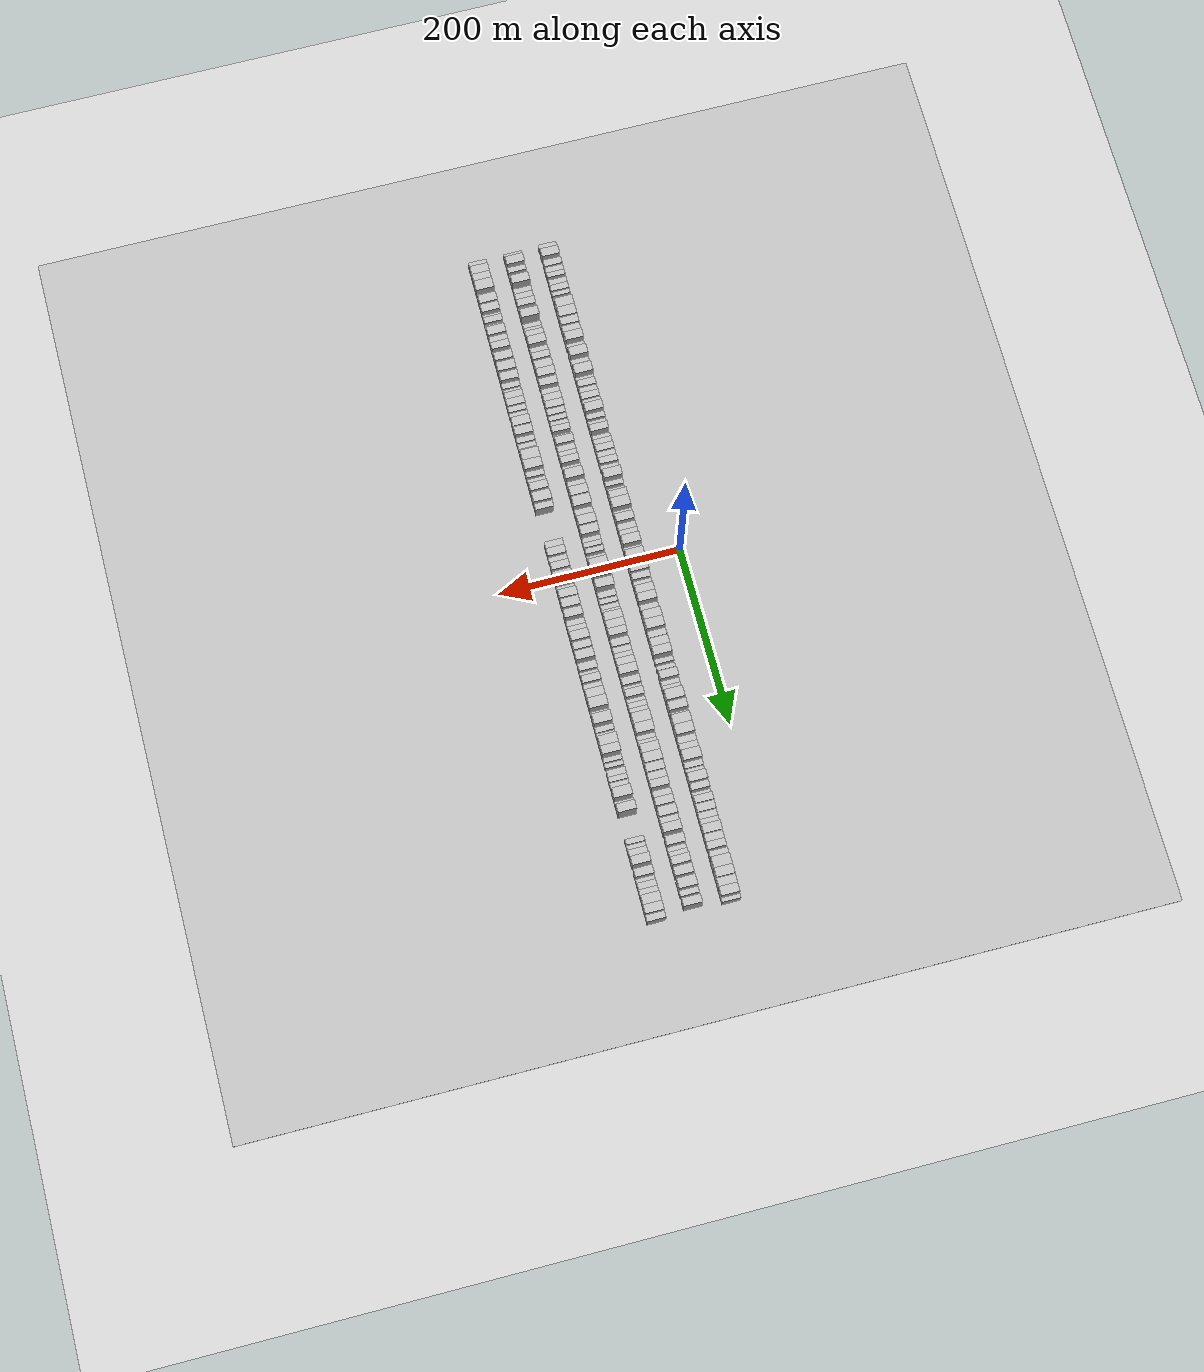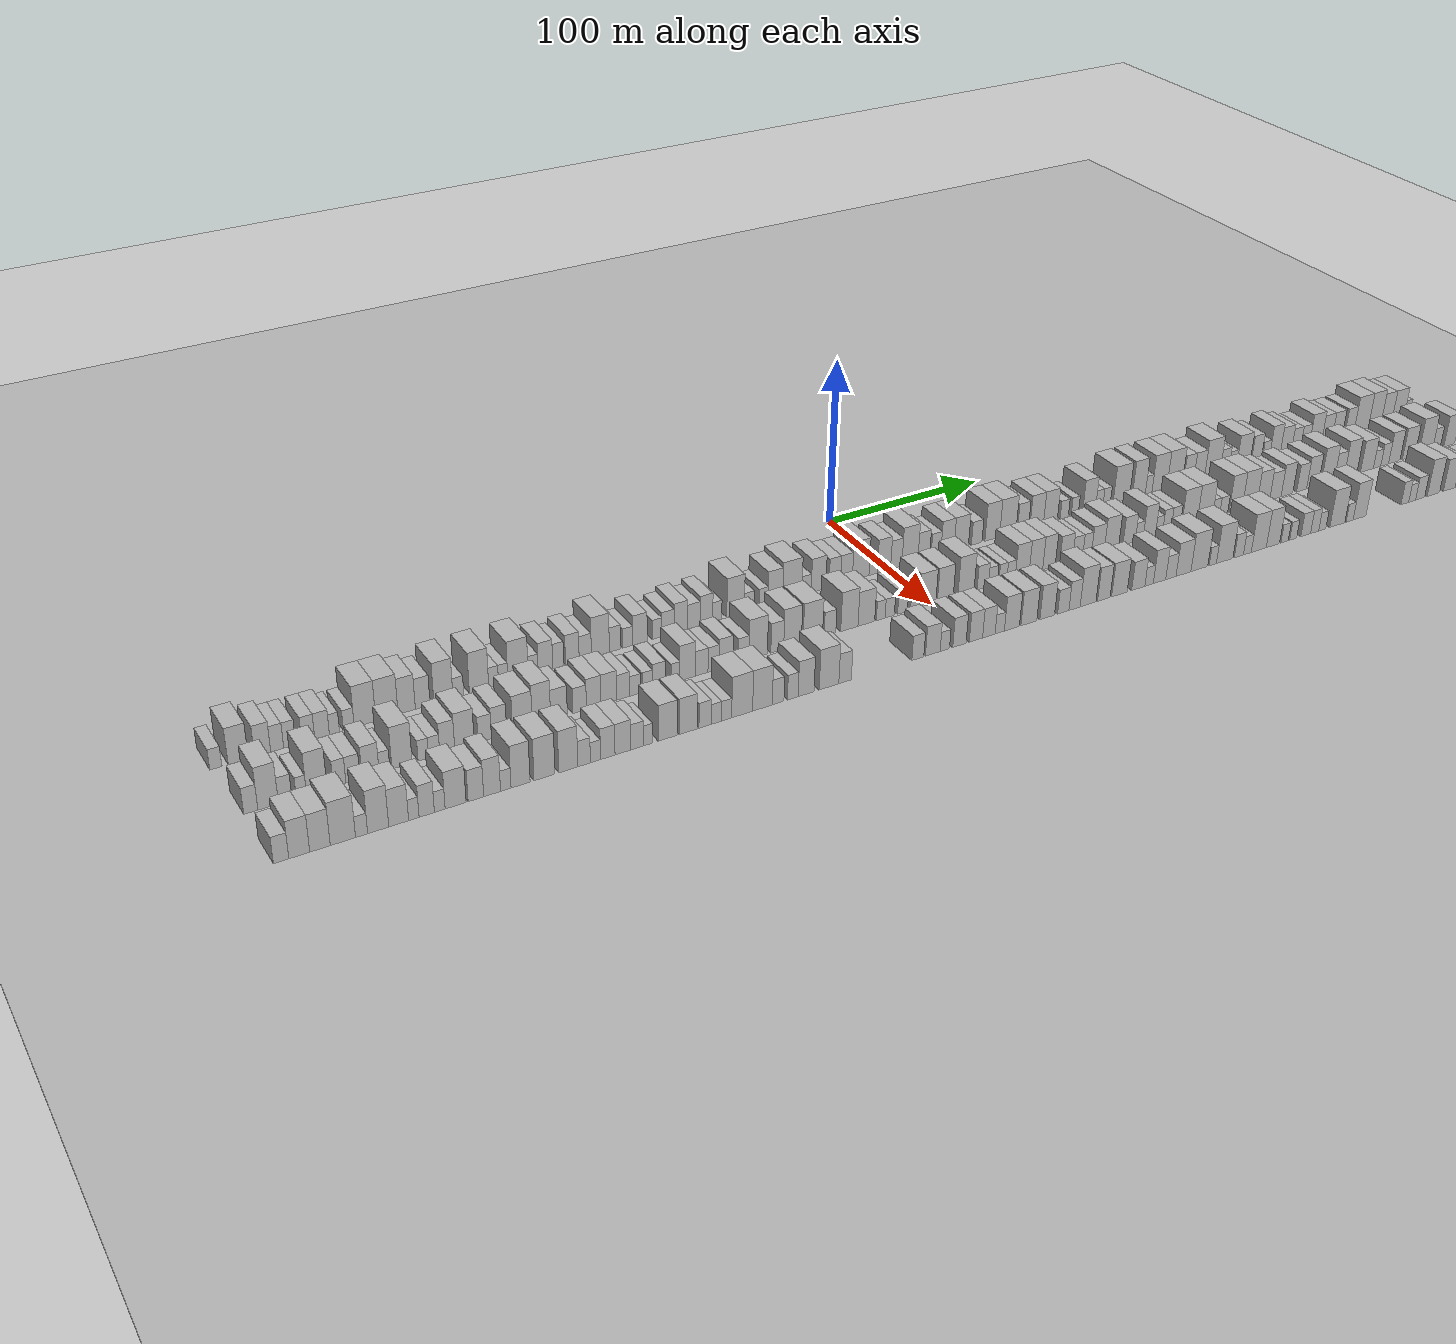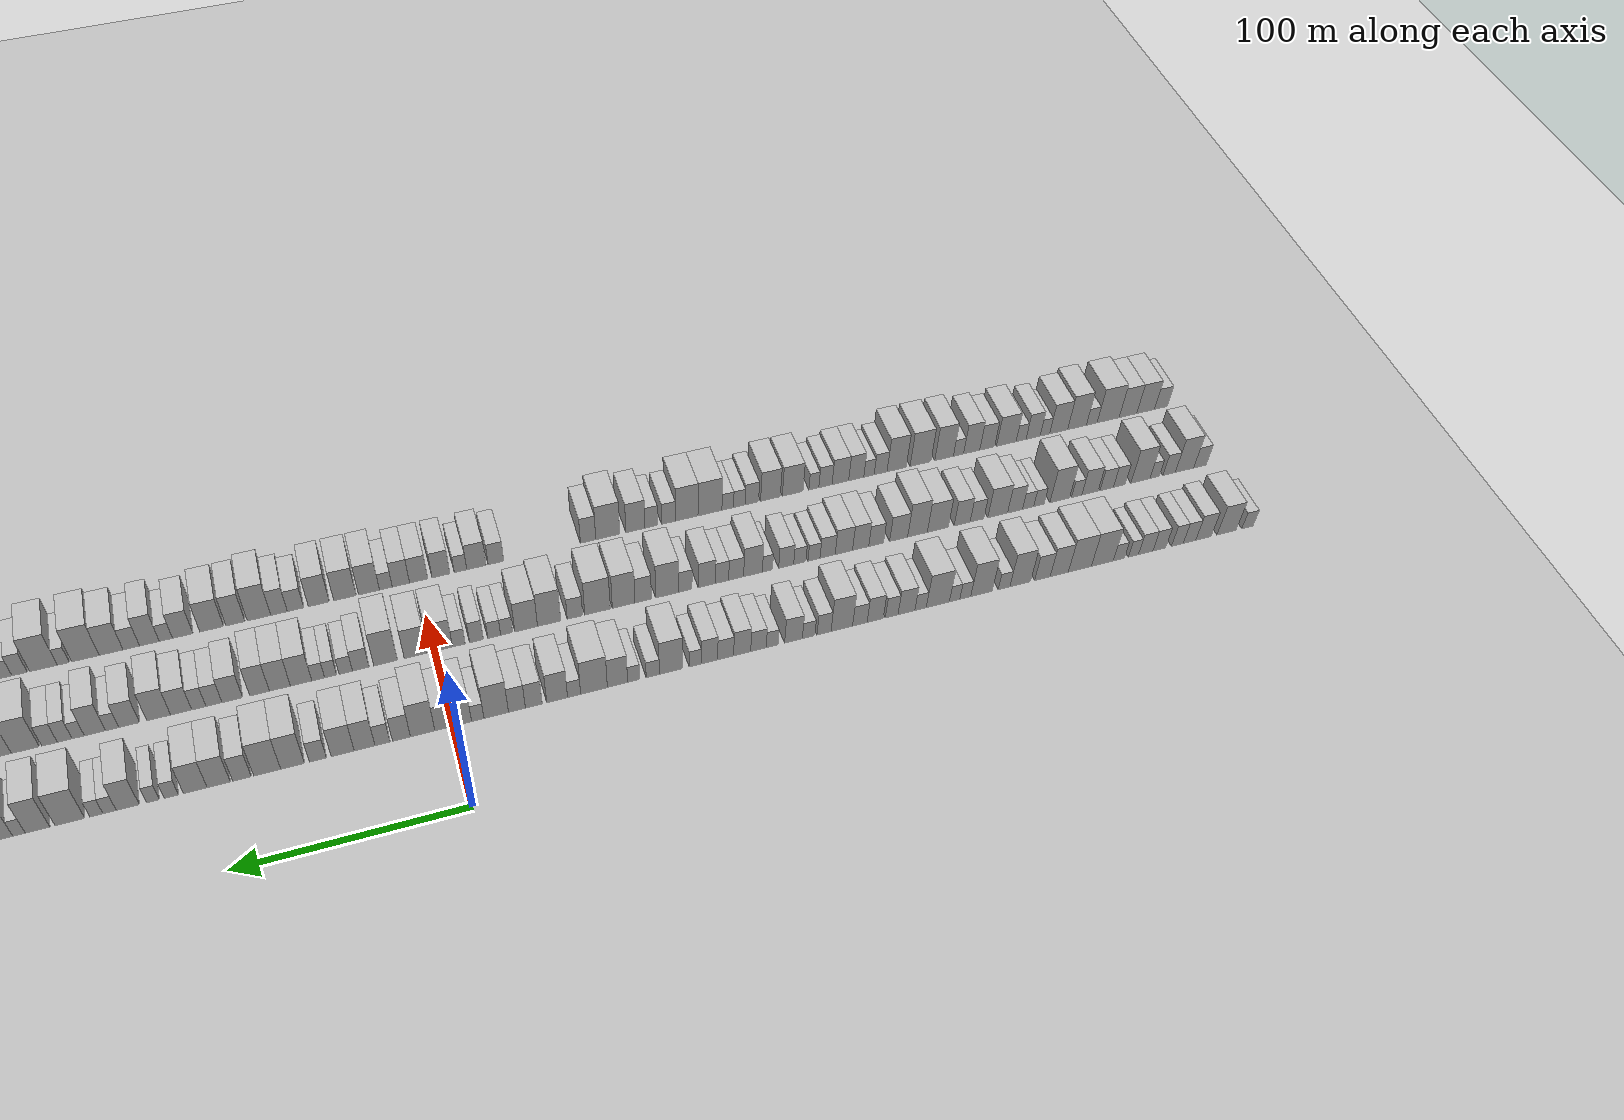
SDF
<?xml version="1.0" encoding="utf-8"?>

<sdf version="1.6">

   <world name="default">

      <gui fullscreen="0">

         <camera name="user_camera">

            <pose>-15 0 4.57585 0 0 0</pose>

            <view_controller>orbit</view_controller>

         </camera>

      </gui>

      <scene>

         <sky>

           <clouds>

             <speed>12</speed>

           </clouds>

         </sky>

         <ambient>0.4 0.4 0.4 1</ambient>

         <background>0.7 0.7 0.7 1</background>

         <shadows>1</shadows>

      </scene>

      <gravity>0 0 -9.8066</gravity>

      <magnetic_field>6e-06 2.3e-05 -4.2e-05</magnetic_field>

      <physics default="0" name="default_physics" type="ode">

         <ode>

            <solver>

               <type>quick</type>

               <iters>10</iters>

               <sor>1.0</sor>

               <use_dynamic_moi_rescaling>0</use_dynamic_moi_rescaling>

            </solver>

            <constraints>

               <cfm>0</cfm>

               <erp>0.2</erp>

               <contact_max_correcting_vel>100</contact_max_correcting_vel>

               <contact_surface_layer>0.001</contact_surface_layer>

            </constraints>

         </ode>

         <max_step_size>0.004</max_step_size>

         <real_time_factor>1</real_time_factor>

         <real_time_update_rate>250</real_time_update_rate>

      </physics>

      <light name="sun" type="directional">

         <cast_shadows>1</cast_shadows>

         <pose>0 0 10 0 0 0</pose>

         <diffuse>0.8 0.8 0.8 1</diffuse>

         <specular>0.2 0.2 0.2 1</specular>

         <attenuation>

            <range>1000</range>

            <constant>0.9</constant>

            <linear>0.01</linear>

            <quadratic>0.001</quadratic>

         </attenuation>

         <direction>-0.5 0.1 -0.9</direction>

      </light>

      <include>

         <name>ground_plane_1</name>

         <uri>model://HANNAS_ground_plane</uri>

         <pose>0 0 0  0 0 0</pose>

      </include>

      <include>

         <name>ground_plane_2</name>

         <uri>model://HANNAS_ground_plane</uri>

         <pose>100 0 0  0 0 0</pose>

      </include>

      <model name="building_1">

         <static>1</static>

         <pose frame="">50.0000 -377.0540 0 0.000000 0.000000 0.000000</pose>

         <link name="link">

            <pose frame="">0 0 6.00 0 0 0</pose>

            <collision name="collision">

               <geometry>

                  <box>

                     <size>20.0000 5.8920 12.0000</size>

                  </box>

               </geometry>

               <max_contacts>10</max_contacts>

               <surface>

                  <contact>

                     <ode/>

                  </contact>

                  <bounce/>

                  <friction>

                     <torsional>

                        <ode/>

                     </torsional>

                     <ode/>

                  </friction>

               </surface>

            </collision>

            <visual name="visual">

               <cast_shadows>0</cast_shadows>

               <geometry>

                  <box>

                     <size>20.0000 5.8920 12.0000</size>

                  </box>

               </geometry>

               <material>

                  <script>

                     <uri>model://HANNAS_wall/materials/scripts</uri>

                     <uri>model://HANNAS_wall/materials/textures</uri>

                     <name>vrc/HANNAS_wall</name>

                  </script>

               </material>

            </visual>

            <self_collide>0</self_collide>

            <enable_wind>0</enable_wind>

            <kinematic>0</kinematic>

         </link>

      </model>

      <model name="building_2">

         <static>1</static>

         <pose frame="">50.0000 -366.1624 0 0.000000 0.000000 0.000000</pose>

         <link name="link">

            <pose frame="">0 0 10.50 0 0 0</pose>

            <collision name="collision">

               <geometry>

                  <box>

                     <size>20.0000 9.8911 21.0000</size>

                  </box>

               </geometry>

               <max_contacts>10</max_contacts>

               <surface>

                  <contact>

                     <ode/>

                  </contact>

                  <bounce/>

                  <friction>

                     <torsional>

                        <ode/>

                     </torsional>

                     <ode/>

                  </friction>

               </surface>

            </collision>

            <visual name="visual">

               <cast_shadows>0</cast_shadows>

               <geometry>

                  <box>

                     <size>20.0000 9.8911 21.0000</size>

                  </box>

               </geometry>

               <material>

                  <script>

                     <uri>model://HANNAS_wall/materials/scripts</uri>

                     <uri>model://HANNAS_wall/materials/textures</uri>

                     <name>vrc/HANNAS_wall</name>

                  </script>

               </material>

            </visual>

            <self_collide>0</self_collide>

            <enable_wind>0</enable_wind>

            <kinematic>0</kinematic>

         </link>

      </model>

      <model name="building_3">

         <static>1</static>

         <pose frame="">50.0000 -354.2423 0 0.000000 0.000000 0.000000</pose>

         <link name="link">

            <pose frame="">0 0 9.00 0 0 0</pose>

            <collision name="collision">

               <geometry>

                  <box>

                     <size>20.0000 7.9491 18.0000</size>

                  </box>

               </geometry>

               <max_contacts>10</max_contacts>

               <surface>

                  <contact>

                     <ode/>

                  </contact>

                  <bounce/>

                  <friction>

                     <torsional>

                        <ode/>

                     </torsional>

                     <ode/>

                  </friction>

               </surface>

            </collision>

            <visual name="visual">

               <cast_shadows>0</cast_shadows>

               <geometry>

                  <box>

                     <size>20.0000 7.9491 18.0000</size>

                  </box>

               </geometry>

               <material>

                  <script>

                     <uri>model://HANNAS_wall/materials/scripts</uri>

                     <uri>model://HANNAS_wall/materials/textures</uri>

                     <name>vrc/HANNAS_wall</name>

                  </script>

               </material>

            </visual>

            <self_collide>0</self_collide>

            <enable_wind>0</enable_wind>

            <kinematic>0</kinematic>

         </link>

      </model>

      <model name="building_4">

         <static>1</static>

         <pose frame="">50.0000 -347.0411 0 0.000000 0.000000 0.000000</pose>

         <link name="link">

            <pose frame="">0 0 7.50 0 0 0</pose>

            <collision name="collision">

               <geometry>

                  <box>

                     <size>20.0000 6.4532 15.0000</size>

                  </box>

               </geometry>

               <max_contacts>10</max_contacts>

               <surface>

                  <contact>

                     <ode/>

                  </contact>

                  <bounce/>

                  <friction>

                     <torsional>

                        <ode/>

                     </torsional>

                     <ode/>

                  </friction>

               </surface>

            </collision>

            <visual name="visual">

               <cast_shadows>0</cast_shadows>

               <geometry>

                  <box>

                     <size>20.0000 6.4532 15.0000</size>

                  </box>

               </geometry>

               <material>

                  <script>

                     <uri>model://HANNAS_wall/materials/scripts</uri>

                     <uri>model://HANNAS_wall/materials/textures</uri>

                     <name>vrc/HANNAS_wall</name>

                  </script>

               </material>

            </visual>

            <self_collide>0</self_collide>

            <enable_wind>0</enable_wind>

            <kinematic>0</kinematic>

         </link>

      </model>

      <model name="building_5">

         <static>1</static>

         <pose frame="">50.0000 -340.8127 0 0.000000 0.000000 0.000000</pose>

         <link name="link">

            <pose frame="">0 0 7.50 0 0 0</pose>

            <collision name="collision">

               <geometry>

                  <box>

                     <size>20.0000 6.0037 15.0000</size>

                  </box>

               </geometry>

               <max_contacts>10</max_contacts>

               <surface>

                  <contact>

                     <ode/>

                  </contact>

                  <bounce/>

                  <friction>

                     <torsional>

                        <ode/>

                     </torsional>

                     <ode/>

                  </friction>

               </surface>

            </collision>

            <visual name="visual">

               <cast_shadows>0</cast_shadows>

               <geometry>

                  <box>

                     <size>20.0000 6.0037 15.0000</size>

                  </box>

               </geometry>

               <material>

                  <script>

                     <uri>model://HANNAS_wall/materials/scripts</uri>

                     <uri>model://HANNAS_wall/materials/textures</uri>

                     <name>vrc/HANNAS_wall</name>

                  </script>

               </material>

            </visual>

            <self_collide>0</self_collide>

            <enable_wind>0</enable_wind>

            <kinematic>0</kinematic>

         </link>

      </model>

      <model name="building_6">

         <static>1</static>

         <pose frame="">50.0000 -331.5779 0 0.000000 0.000000 0.000000</pose>

         <link name="link">

            <pose frame="">0 0 7.50 0 0 0</pose>

            <collision name="collision">

               <geometry>

                  <box>

                     <size>20.0000 6.4658 15.0000</size>

                  </box>

               </geometry>

               <max_contacts>10</max_contacts>

               <surface>

                  <contact>

                     <ode/>

                  </contact>

                  <bounce/>

                  <friction>

                     <torsional>

                        <ode/>

                     </torsional>

                     <ode/>

                  </friction>

               </surface>

            </collision>

            <visual name="visual">

               <cast_shadows>0</cast_shadows>

               <geometry>

                  <box>

                     <size>20.0000 6.4658 15.0000</size>

                  </box>

               </geometry>

               <material>

                  <script>

                     <uri>model://HANNAS_wall/materials/scripts</uri>

                     <uri>model://HANNAS_wall/materials/textures</uri>

                     <name>vrc/HANNAS_wall</name>

                  </script>

               </material>

            </visual>

            <self_collide>0</self_collide>

            <enable_wind>0</enable_wind>

            <kinematic>0</kinematic>

         </link>

      </model>

      <model name="building_7">

         <static>1</static>

         <pose frame="">50.0000 -324.6512 0 0.000000 0.000000 0.000000</pose>

         <link name="link">

            <pose frame="">0 0 7.50 0 0 0</pose>

            <collision name="collision">

               <geometry>

                  <box>

                     <size>20.0000 7.3875 15.0000</size>

                  </box>

               </geometry>

               <max_contacts>10</max_contacts>

               <surface>

                  <contact>

                     <ode/>

                  </contact>

                  <bounce/>

                  <friction>

                     <torsional>

                        <ode/>

                     </torsional>

                     <ode/>

                  </friction>

               </surface>

            </collision>

            <visual name="visual">

               <cast_shadows>0</cast_shadows>

               <geometry>

                  <box>

                     <size>20.0000 7.3875 15.0000</size>

                  </box>

               </geometry>

               <material>

                  <script>

                     <uri>model://HANNAS_wall/materials/scripts</uri>

                     <uri>model://HANNAS_wall/materials/textures</uri>

                     <name>vrc/HANNAS_wall</name>

                  </script>

               </material>

            </visual>

            <self_collide>0</self_collide>

            <enable_wind>0</enable_wind>

            <kinematic>0</kinematic>

         </link>

      </model>

      <model name="building_8">

         <static>1</static>

         <pose frame="">50.0000 -318.4084 0 0.000000 0.000000 0.000000</pose>

         <link name="link">

            <pose frame="">0 0 6.00 0 0 0</pose>

            <collision name="collision">

               <geometry>

                  <box>

                     <size>20.0000 5.0983 12.0000</size>

                  </box>

               </geometry>

               <max_contacts>10</max_contacts>

               <surface>

                  <contact>

                     <ode/>

                  </contact>

                  <bounce/>

                  <friction>

                     <torsional>

                        <ode/>

                     </torsional>

                     <ode/>

                  </friction>

               </surface>

            </collision>

            <visual name="visual">

               <cast_shadows>0</cast_shadows>

               <geometry>

                  <box>

                     <size>20.0000 5.0983 12.0000</size>

                  </box>

               </geometry>

               <material>

                  <script>

                     <uri>model://HANNAS_wall/materials/scripts</uri>

                     <uri>model://HANNAS_wall/materials/textures</uri>

                     <name>vrc/HANNAS_wall</name>

                  </script>

               </material>

            </visual>

            <self_collide>0</self_collide>

            <enable_wind>0</enable_wind>

            <kinematic>0</kinematic>

         </link>

      </model>

      <model name="building_9">

         <static>1</static>

         <pose frame="">50.0000 -311.0711 0 0.000000 0.000000 0.000000</pose>

         <link name="link">

            <pose frame="">0 0 6.00 0 0 0</pose>

            <collision name="collision">

               <geometry>

                  <box>

                     <size>20.0000 5.5763 12.0000</size>

                  </box>

               </geometry>

               <max_contacts>10</max_contacts>

               <surface>

                  <contact>

                     <ode/>

                  </contact>

                  <bounce/>

                  <friction>

                     <torsional>

                        <ode/>

                     </torsional>

                     <ode/>

                  </friction>

               </surface>

            </collision>

            <visual name="visual">

               <cast_shadows>0</cast_shadows>

               <geometry>

                  <box>

                     <size>20.0000 5.5763 12.0000</size>

                  </box>

               </geometry>

               <material>

                  <script>

                     <uri>model://HANNAS_wall/materials/scripts</uri>

                     <uri>model://HANNAS_wall/materials/textures</uri>

                     <name>vrc/HANNAS_wall</name>

                  </script>

               </material>

            </visual>

            <self_collide>0</self_collide>

            <enable_wind>0</enable_wind>

            <kinematic>0</kinematic>

         </link>

      </model>

      <model name="building_10">

         <static>1</static>

         <pose frame="">50.0000 -302.7617 0 0.000000 0.000000 0.000000</pose>

         <link name="link">

            <pose frame="">0 0 12.00 0 0 0</pose>

            <collision name="collision">

               <geometry>

                  <box>

                     <size>20.0000 11.0424 24.0000</size>

                  </box>

               </geometry>

               <max_contacts>10</max_contacts>

               <surface>

                  <contact>

                     <ode/>

                  </contact>

                  <bounce/>

                  <friction>

                     <torsional>

                        <ode/>

                     </torsional>

                     <ode/>

                  </friction>

               </surface>

            </collision>

            <visual name="visual">

               <cast_shadows>0</cast_shadows>

               <geometry>

                  <box>

                     <size>20.0000 11.0424 24.0000</size>

                  </box>

               </geometry>

               <material>

                  <script>

                     <uri>model://HANNAS_wall/materials/scripts</uri>

                     <uri>model://HANNAS_wall/materials/textures</uri>

                     <name>vrc/HANNAS_wall</name>

                  </script>

               </material>

            </visual>

            <self_collide>0</self_collide>

            <enable_wind>0</enable_wind>

            <kinematic>0</kinematic>

         </link>

      </model>

      <model name="building_11">

         <static>1</static>

         <pose frame="">50.0000 -291.4721 0 0.000000 0.000000 0.000000</pose>

         <link name="link">

            <pose frame="">0 0 12.00 0 0 0</pose>

            <collision name="collision">

               <geometry>

                  <box>

                     <size>20.0000 11.5366 24.0000</size>

                  </box>

               </geometry>

               <max_contacts>10</max_contacts>

               <surface>

                  <contact>

                     <ode/>

                  </contact>

                  <bounce/>

                  <friction>

                     <torsional>

                        <ode/>

                     </torsional>

                     <ode/>

                  </friction>

               </surface>

            </collision>

            <visual name="visual">

               <cast_shadows>0</cast_shadows>

               <geometry>

                  <box>

                     <size>20.0000 11.5366 24.0000</size>

                  </box>

               </geometry>

               <material>

                  <script>

                     <uri>model://HANNAS_wall/materials/scripts</uri>

                     <uri>model://HANNAS_wall/materials/textures</uri>

                     <name>vrc/HANNAS_wall</name>

                  </script>

               </material>

            </visual>

            <self_collide>0</self_collide>

            <enable_wind>0</enable_wind>

            <kinematic>0</kinematic>

         </link>

      </model>

      <model name="building_12">

         <static>1</static>

         <pose frame="">50.0000 -281.1900 0 0.000000 0.000000 0.000000</pose>

         <link name="link">

            <pose frame="">0 0 10.50 0 0 0</pose>

            <collision name="collision">

               <geometry>

                  <box>

                     <size>20.0000 9.0277 21.0000</size>

                  </box>

               </geometry>

               <max_contacts>10</max_contacts>

               <surface>

                  <contact>

                     <ode/>

                  </contact>

                  <bounce/>

                  <friction>

                     <torsional>

                        <ode/>

                     </torsional>

                     <ode/>

                  </friction>

               </surface>

            </collision>

            <visual name="visual">

               <cast_shadows>0</cast_shadows>

               <geometry>

                  <box>

                     <size>20.0000 9.0277 21.0000</size>

                  </box>

               </geometry>

               <material>

                  <script>

                     <uri>model://HANNAS_wall/materials/scripts</uri>

                     <uri>model://HANNAS_wall/materials/textures</uri>

                     <name>vrc/HANNAS_wall</name>

                  </script>

               </material>

            </visual>

            <self_collide>0</self_collide>

            <enable_wind>0</enable_wind>

            <kinematic>0</kinematic>

         </link>

      </model>

      <model name="building_13">

         <static>1</static>

         <pose frame="">50.0000 -272.8002 0 0.000000 0.000000 0.000000</pose>

         <link name="link">

            <pose frame="">0 0 9.00 0 0 0</pose>

            <collision name="collision">

               <geometry>

                  <box>

                     <size>20.0000 7.7519 18.0000</size>

                  </box>

               </geometry>

               <max_contacts>10</max_contacts>

               <surface>

                  <contact>

                     <ode/>

                  </contact>

                  <bounce/>

                  <friction>

                     <torsional>

                        <ode/>

                     </torsional>

                     <ode/>

                  </friction>

               </surface>

            </collision>

            <visual name="visual">

               <cast_shadows>0</cast_shadows>

               <geometry>

                  <box>

                     <size>20.0000 7.7519 18.0000</size>

                  </box>

               </geometry>

               <material>

                  <script>

                     <uri>model://HANNAS_wall/materials/scripts</uri>

                     <uri>model://HANNAS_wall/materials/textures</uri>

                     <name>vrc/HANNAS_wall</name>

                  </script>

               </material>

            </visual>

            <self_collide>0</self_collide>

            <enable_wind>0</enable_wind>

            <kinematic>0</kinematic>

         </link>

      </model>

      <model name="building_14">

         <static>1</static>

         <pose frame="">50.0000 -261.8460 0 0.000000 0.000000 0.000000</pose>

         <link name="link">

            <pose frame="">0 0 12.00 0 0 0</pose>

            <collision name="collision">

               <geometry>

                  <box>

                     <size>20.0000 10.1565 24.0000</size>

                  </box>

               </geometry>

               <max_contacts>10</max_contacts>

               <surface>

                  <contact>

                     <ode/>

                  </contact>

                  <bounce/>

                  <friction>

                     <torsional>

                        <ode/>

                     </torsional>

                     <ode/>

                  </friction>

               </surface>

            </collision>

            <visual name="visual">

               <cast_shadows>0</cast_shadows>

               <geometry>

                  <box>

                     <size>20.0000 10.1565 24.0000</size>

                  </box>

               </geometry>

               <material>

                  <script>

                     <uri>model://HANNAS_wall/materials/scripts</uri>

                     <uri>model://HANNAS_wall/materials/textures</uri>

                     <name>vrc/HANNAS_wall</name>

                  </script>

               </material>

            </visual>

            <self_collide>0</self_collide>

            <enable_wind>0</enable_wind>

            <kinematic>0</kinematic>

         </link>

      </model>

      <model name="building_15">

         <static>1</static>

         <pose frame="">50.0000 -253.9050 0 0.000000 0.000000 0.000000</pose>

         <link name="link">

            <pose frame="">0 0 6.00 0 0 0</pose>

            <collision name="collision">

               <geometry>

                  <box>

                     <size>20.0000 5.7257 12.0000</size>

                  </box>

               </geometry>

               <max_contacts>10</max_contacts>

               <surface>

                  <contact>

                     <ode/>

                  </contact>

                  <bounce/>

                  <friction>

                     <torsional>

                        <ode/>

                     </torsional>

                     <ode/>

                  </friction>

               </surface>

            </collision>

            <visual name="visual">

               <cast_shadows>0</cast_shadows>

               <geometry>

                  <box>

                     <size>20.0000 5.7257 12.0000</size>

                  </box>

               </geometry>

               <material>

                  <script>

                     <uri>model://HANNAS_wall/materials/scripts</uri>

                     <uri>model://HANNAS_wall/materials/textures</uri>

                     <name>vrc/HANNAS_wall</name>

                  </script>

               </material>

            </visual>

            <self_collide>0</self_collide>

            <enable_wind>0</enable_wind>

            <kinematic>0</kinematic>

         </link>

      </model>

      <model name="building_16">

         <static>1</static>

         <pose frame="">50.0000 -242.8090 0 0.000000 0.000000 0.000000</pose>

         <link name="link">

            <pose frame="">0 0 12.00 0 0 0</pose>

            <collision name="collision">

               <geometry>

                  <box>

                     <size>20.0000 10.4662 24.0000</size>

                  </box>

               </geometry>

               <max_contacts>10</max_contacts>

               <surface>

                  <contact>

                     <ode/>

                  </contact>

                  <bounce/>

                  <friction>

                     <torsional>

                        <ode/>

                     </torsional>

                     <ode/>

                  </friction>

               </surface>

            </collision>

            <visual name="visual">

               <cast_shadows>0</cast_shadows>

               <geometry>

                  <box>

                     <size>20.0000 10.4662 24.0000</size>

                  </box>

               </geometry>

               <material>

                  <script>

                     <uri>model://HANNAS_wall/materials/scripts</uri>

                     <uri>model://HANNAS_wall/materials/textures</uri>

                     <name>vrc/HANNAS_wall</name>

                  </script>

               </material>

            </visual>

            <self_collide>0</self_collide>

            <enable_wind>0</enable_wind>

            <kinematic>0</kinematic>

         </link>

      </model>

      <model name="building_17">

         <static>1</static>

         <pose frame="">50.0000 -234.9070 0 0.000000 0.000000 0.000000</pose>

         <link name="link">

            <pose frame="">0 0 6.00 0 0 0</pose>

            <collision name="collision">

               <geometry>

                  <box>

                     <size>20.0000 5.3379 12.0000</size>

                  </box>

               </geometry>

               <max_contacts>10</max_contacts>

               <surface>

                  <contact>

                     <ode/>

                  </contact>

                  <bounce/>

                  <friction>

                     <torsional>

                        <ode/>

                     </torsional>

                     <ode/>

                  </friction>

               </surface>

            </collision>

            <visual name="visual">

               <cast_shadows>0</cast_shadows>

               <geometry>

                  <box>

                     <size>20.0000 5.3379 12.0000</size>

                  </box>

               </geometry>

               <material>

                  <script>

                     <uri>model://HANNAS_wall/materials/scripts</uri>

                     <uri>model://HANNAS_wall/materials/textures</uri>

                     <name>vrc/HANNAS_wall</name>

                  </script>

               </material>

            </visual>

            <self_collide>0</self_collide>

            <enable_wind>0</enable_wind>

            <kinematic>0</kinematic>

         </link>

      </model>

      <model name="building_18">

         <static>1</static>

         <pose frame="">50.0000 -229.7093 0 0.000000 0.000000 0.000000</pose>

         <link name="link">

            <pose frame="">0 0 6.00 0 0 0</pose>

            <collision name="collision">

               <geometry>

                  <box>

                     <size>20.0000 5.0574 12.0000</size>

                  </box>

               </geometry>

               <max_contacts>10</max_contacts>

               <surface>

                  <contact>

                     <ode/>

                  </contact>

                  <bounce/>

                  <friction>

                     <torsional>

                        <ode/>

                     </torsional>

                     <ode/>

                  </friction>

               </surface>

            </collision>

            <visual name="visual">

               <cast_shadows>0</cast_shadows>

               <geometry>

                  <box>

                     <size>20.0000 5.0574 12.0000</size>

                  </box>

               </geometry>

               <material>

                  <script>

                     <uri>model://HANNAS_wall/materials/scripts</uri>

                     <uri>model://HANNAS_wall/materials/textures</uri>

                     <name>vrc/HANNAS_wall</name>

                  </script>

               </material>

            </visual>

            <self_collide>0</self_collide>

            <enable_wind>0</enable_wind>

            <kinematic>0</kinematic>

         </link>

      </model>

      <model name="building_19">

         <static>1</static>

         <pose frame="">50.0000 -221.5960 0 0.000000 0.000000 0.000000</pose>

         <link name="link">

            <pose frame="">0 0 12.00 0 0 0</pose>

            <collision name="collision">

               <geometry>

                  <box>

                     <size>20.0000 11.1692 24.0000</size>

                  </box>

               </geometry>

               <max_contacts>10</max_contacts>

               <surface>

                  <contact>

                     <ode/>

                  </contact>

                  <bounce/>

                  <friction>

                     <torsional>

                        <ode/>

                     </torsional>

                     <ode/>

                  </friction>

               </surface>

            </collision>

            <visual name="visual">

               <cast_shadows>0</cast_shadows>

               <geometry>

                  <box>

                     <size>20.0000 11.1692 24.0000</size>

                  </box>

               </geometry>

               <material>

                  <script>

                     <uri>model://HANNAS_wall/materials/scripts</uri>

                     <uri>model://HANNAS_wall/materials/textures</uri>

                     <name>vrc/HANNAS_wall</name>

                  </script>

               </material>

            </visual>

            <self_collide>0</self_collide>

            <enable_wind>0</enable_wind>

            <kinematic>0</kinematic>

         </link>

      </model>

      <model name="building_20">

         <static>1</static>

         <pose frame="">50.0000 -213.2641 0 0.000000 0.000000 0.000000</pose>

         <link name="link">

            <pose frame="">0 0 6.00 0 0 0</pose>

            <collision name="collision">

               <geometry>

                  <box>

                     <size>20.0000 5.4946 12.0000</size>

                  </box>

               </geometry>

               <max_contacts>10</max_contacts>

               <surface>

                  <contact>

                     <ode/>

                  </contact>

                  <bounce/>

                  <friction>

                     <torsional>

                        <ode/>

                     </torsional>

                     <ode/>

                  </friction>

               </surface>

            </collision>

            <visual name="visual">

               <cast_shadows>0</cast_shadows>

               <geometry>

                  <box>

                     <size>20.0000 5.4946 12.0000</size>

                  </box>

               </geometry>

               <material>

                  <script>

                     <uri>model://HANNAS_wall/materials/scripts</uri>

                     <uri>model://HANNAS_wall/materials/textures</uri>

                     <name>vrc/HANNAS_wall</name>

                  </script>

               </material>

            </visual>

            <self_collide>0</self_collide>

            <enable_wind>0</enable_wind>

            <kinematic>0</kinematic>

         </link>

      </model>

      <model name="building_21">

         <static>1</static>

         <pose frame="">50.0000 -206.4756 0 0.000000 0.000000 0.000000</pose>

         <link name="link">

            <pose frame="">0 0 9.00 0 0 0</pose>

            <collision name="collision">

               <geometry>

                  <box>

                     <size>20.0000 8.0824 18.0000</size>

                  </box>

               </geometry>

               <max_contacts>10</max_contacts>

               <surface>

                  <contact>

                     <ode/>

                  </contact>

                  <bounce/>

                  <friction>

                     <torsional>

                        <ode/>

                     </torsional>

                     <ode/>

                  </friction>

               </surface>

            </collision>

            <visual name="visual">

               <cast_shadows>0</cast_shadows>

               <geometry>

                  <box>

                     <size>20.0000 8.0824 18.0000</size>

                  </box>

               </geometry>

               <material>

                  <script>

                     <uri>model://HANNAS_wall/materials/scripts</uri>

                     <uri>model://HANNAS_wall/materials/textures</uri>

                     <name>vrc/HANNAS_wall</name>

                  </script>

               </material>

            </visual>

            <self_collide>0</self_collide>

            <enable_wind>0</enable_wind>

            <kinematic>0</kinematic>

         </link>

      </model>

      <model name="building_22">

         <static>1</static>

         <pose frame="">50.0000 -199.3882 0 0.000000 0.000000 0.000000</pose>

         <link name="link">

            <pose frame="">0 0 7.50 0 0 0</pose>

            <collision name="collision">

               <geometry>

                  <box>

                     <size>20.0000 6.0923 15.0000</size>

                  </box>

               </geometry>

               <max_contacts>10</max_contacts>

               <surface>

                  <contact>

                     <ode/>

                  </contact>

                  <bounce/>

                  <friction>

                     <torsional>

                        <ode/>

                     </torsional>

                     <ode/>

                  </friction>

               </surface>

            </collision>

            <visual name="visual">

               <cast_shadows>0</cast_shadows>

               <geometry>

                  <box>

                     <size>20.0000 6.0923 15.0000</size>

                  </box>

               </geometry>

               <material>

                  <script>

                     <uri>model://HANNAS_wall/materials/scripts</uri>

                     <uri>model://HANNAS_wall/materials/textures</uri>

                     <name>vrc/HANNAS_wall</name>

                  </script>

               </material>

            </visual>

            <self_collide>0</self_collide>

            <enable_wind>0</enable_wind>

            <kinematic>0</kinematic>

         </link>

      </model>

      <model name="building_23">

         <static>1</static>

         <pose frame="">50.0000 -191.5020 0 0.000000 0.000000 0.000000</pose>

         <link name="link">

            <pose frame="">0 0 9.00 0 0 0</pose>

            <collision name="collision">

               <geometry>

                  <box>

                     <size>20.0000 7.6802 18.0000</size>

                  </box>

               </geometry>

               <max_contacts>10</max_contacts>

               <surface>

                  <contact>

                     <ode/>

                  </contact>

                  <bounce/>

                  <friction>

                     <torsional>

                        <ode/>

                     </torsional>

                     <ode/>

                  </friction>

               </surface>

            </collision>

            <visual name="visual">

               <cast_shadows>0</cast_shadows>

               <geometry>

                  <box>

                     <size>20.0000 7.6802 18.0000</size>

                  </box>

               </geometry>

               <material>

                  <script>

                     <uri>model://HANNAS_wall/materials/scripts</uri>

                     <uri>model://HANNAS_wall/materials/textures</uri>

                     <name>vrc/HANNAS_wall</name>

                  </script>

               </material>

            </visual>

            <self_collide>0</self_collide>

            <enable_wind>0</enable_wind>

            <kinematic>0</kinematic>

         </link>

      </model>

      <model name="building_24">

         <static>1</static>

         <pose frame="">50.0000 -184.2094 0 0.000000 0.000000 0.000000</pose>

         <link name="link">

            <pose frame="">0 0 7.50 0 0 0</pose>

            <collision name="collision">

               <geometry>

                  <box>

                     <size>20.0000 6.9049 15.0000</size>

                  </box>

               </geometry>

               <max_contacts>10</max_contacts>

               <surface>

                  <contact>

                     <ode/>

                  </contact>

                  <bounce/>

                  <friction>

                     <torsional>

                        <ode/>

                     </torsional>

                     <ode/>

                  </friction>

               </surface>

            </collision>

            <visual name="visual">

               <cast_shadows>0</cast_shadows>

               <geometry>

                  <box>

                     <size>20.0000 6.9049 15.0000</size>

                  </box>

               </geometry>

               <material>

                  <script>

                     <uri>model://HANNAS_wall/materials/scripts</uri>

                     <uri>model://HANNAS_wall/materials/textures</uri>

                     <name>vrc/HANNAS_wall</name>

                  </script>

               </material>

            </visual>

            <self_collide>0</self_collide>

            <enable_wind>0</enable_wind>

            <kinematic>0</kinematic>

         </link>

      </model>

      <model name="building_25">

         <static>1</static>

         <pose frame="">50.0000 -175.6694 0 0.000000 0.000000 0.000000</pose>

         <link name="link">

            <pose frame="">0 0 12.00 0 0 0</pose>

            <collision name="collision">

               <geometry>

                  <box>

                     <size>20.0000 10.1751 24.0000</size>

                  </box>

               </geometry>

               <max_contacts>10</max_contacts>

               <surface>

                  <contact>

                     <ode/>

                  </contact>

                  <bounce/>

                  <friction>

                     <torsional>

                        <ode/>

                     </torsional>

                     <ode/>

                  </friction>

               </surface>

            </collision>

            <visual name="visual">

               <cast_shadows>0</cast_shadows>

               <geometry>

                  <box>

                     <size>20.0000 10.1751 24.0000</size>

                  </box>

               </geometry>

               <material>

                  <script>

                     <uri>model://HANNAS_wall/materials/scripts</uri>

                     <uri>model://HANNAS_wall/materials/textures</uri>

                     <name>vrc/HANNAS_wall</name>

                  </script>

               </material>

            </visual>

            <self_collide>0</self_collide>

            <enable_wind>0</enable_wind>

            <kinematic>0</kinematic>

         </link>

      </model>

      <model name="building_26">

         <static>1</static>

         <pose frame="">50.0000 -167.2690 0 0.000000 0.000000 0.000000</pose>

         <link name="link">

            <pose frame="">0 0 7.50 0 0 0</pose>

            <collision name="collision">

               <geometry>

                  <box>

                     <size>20.0000 6.6258 15.0000</size>

                  </box>

               </geometry>

               <max_contacts>10</max_contacts>

               <surface>

                  <contact>

                     <ode/>

                  </contact>

                  <bounce/>

                  <friction>

                     <torsional>

                        <ode/>

                     </torsional>

                     <ode/>

                  </friction>

               </surface>

            </collision>

            <visual name="visual">

               <cast_shadows>0</cast_shadows>

               <geometry>

                  <box>

                     <size>20.0000 6.6258 15.0000</size>

                  </box>

               </geometry>

               <material>

                  <script>

                     <uri>model://HANNAS_wall/materials/scripts</uri>

                     <uri>model://HANNAS_wall/materials/textures</uri>

                     <name>vrc/HANNAS_wall</name>

                  </script>

               </material>

            </visual>

            <self_collide>0</self_collide>

            <enable_wind>0</enable_wind>

            <kinematic>0</kinematic>

         </link>

      </model>

      <model name="building_27">

         <static>1</static>

         <pose frame="">50.0000 -160.0343 0 0.000000 0.000000 0.000000</pose>

         <link name="link">

            <pose frame="">0 0 6.00 0 0 0</pose>

            <collision name="collision">

               <geometry>

                  <box>

                     <size>20.0000 5.8437 12.0000</size>

                  </box>

               </geometry>

               <max_contacts>10</max_contacts>

               <surface>

                  <contact>

                     <ode/>

                  </contact>

                  <bounce/>

                  <friction>

                     <torsional>

                        <ode/>

                     </torsional>

                     <ode/>

                  </friction>

               </surface>

            </collision>

            <visual name="visual">

               <cast_shadows>0</cast_shadows>

               <geometry>

                  <box>

                     <size>20.0000 5.8437 12.0000</size>

                  </box>

               </geometry>

               <material>

                  <script>

                     <uri>model://HANNAS_wall/materials/scripts</uri>

                     <uri>model://HANNAS_wall/materials/textures</uri>

                     <name>vrc/HANNAS_wall</name>

                  </script>

               </material>

            </visual>

            <self_collide>0</self_collide>

            <enable_wind>0</enable_wind>

            <kinematic>0</kinematic>

         </link>

      </model>

      <model name="building_28">

         <static>1</static>

         <pose frame="">50.0000 -152.9661 0 0.000000 0.000000 0.000000</pose>

         <link name="link">

            <pose frame="">0 0 9.00 0 0 0</pose>

            <collision name="collision">

               <geometry>

                  <box>

                     <size>20.0000 8.2926 18.0000</size>

                  </box>

               </geometry>

               <max_contacts>10</max_contacts>

               <surface>

                  <contact>

                     <ode/>

                  </contact>

                  <bounce/>

                  <friction>

                     <torsional>

                        <ode/>

                     </torsional>

                     <ode/>

                  </friction>

               </surface>

            </collision>

            <visual name="visual">

               <cast_shadows>0</cast_shadows>

               <geometry>

                  <box>

                     <size>20.0000 8.2926 18.0000</size>

                  </box>

               </geometry>

               <material>

                  <script>

                     <uri>model://HANNAS_wall/materials/scripts</uri>

                     <uri>model://HANNAS_wall/materials/textures</uri>

                     <name>vrc/HANNAS_wall</name>

                  </script>

               </material>

            </visual>

            <self_collide>0</self_collide>

            <enable_wind>0</enable_wind>

            <kinematic>0</kinematic>

         </link>

      </model>

      <model name="building_29">

         <static>1</static>

         <pose frame="">50.0000 -143.0252 0 0.000000 0.000000 0.000000</pose>

         <link name="link">

            <pose frame="">0 0 6.00 0 0 0</pose>

            <collision name="collision">

               <geometry>

                  <box>

                     <size>20.0000 5.5892 12.0000</size>

                  </box>

               </geometry>

               <max_contacts>10</max_contacts>

               <surface>

                  <contact>

                     <ode/>

                  </contact>

                  <bounce/>

                  <friction>

                     <torsional>

                        <ode/>

                     </torsional>

                     <ode/>

                  </friction>

               </surface>

            </collision>

            <visual name="visual">

               <cast_shadows>0</cast_shadows>

               <geometry>

                  <box>

                     <size>20.0000 5.5892 12.0000</size>

                  </box>

               </geometry>

               <material>

                  <script>

                     <uri>model://HANNAS_wall/materials/scripts</uri>

                     <uri>model://HANNAS_wall/materials/textures</uri>

                     <name>vrc/HANNAS_wall</name>

                  </script>

               </material>

            </visual>

            <self_collide>0</self_collide>

            <enable_wind>0</enable_wind>

            <kinematic>0</kinematic>

         </link>

      </model>

      <model name="building_30">

         <static>1</static>

         <pose frame="">50.0000 -136.6404 0 0.000000 0.000000 0.000000</pose>

         <link name="link">

            <pose frame="">0 0 7.50 0 0 0</pose>

            <collision name="collision">

               <geometry>

                  <box>

                     <size>20.0000 7.1805 15.0000</size>

                  </box>

               </geometry>

               <max_contacts>10</max_contacts>

               <surface>

                  <contact>

                     <ode/>

                  </contact>

                  <bounce/>

                  <friction>

                     <torsional>

                        <ode/>

                     </torsional>

                     <ode/>

                  </friction>

               </surface>

            </collision>

            <visual name="visual">

               <cast_shadows>0</cast_shadows>

               <geometry>

                  <box>

                     <size>20.0000 7.1805 15.0000</size>

                  </box>

               </geometry>

               <material>

                  <script>

                     <uri>model://HANNAS_wall/materials/scripts</uri>

                     <uri>model://HANNAS_wall/materials/textures</uri>

                     <name>vrc/HANNAS_wall</name>

                  </script>

               </material>

            </visual>

            <self_collide>0</self_collide>

            <enable_wind>0</enable_wind>

            <kinematic>0</kinematic>

         </link>

      </model>

      <model name="building_31">

         <static>1</static>

         <pose frame="">50.0000 -129.1069 0 0.000000 0.000000 0.000000</pose>

         <link name="link">

            <pose frame="">0 0 9.00 0 0 0</pose>

            <collision name="collision">

               <geometry>

                  <box>

                     <size>20.0000 7.8865 18.0000</size>

                  </box>

               </geometry>

               <max_contacts>10</max_contacts>

               <surface>

                  <contact>

                     <ode/>

                  </contact>

                  <bounce/>

                  <friction>

                     <torsional>

                        <ode/>

                     </torsional>

                     <ode/>

                  </friction>

               </surface>

            </collision>

            <visual name="visual">

               <cast_shadows>0</cast_shadows>

               <geometry>

                  <box>

                     <size>20.0000 7.8865 18.0000</size>

                  </box>

               </geometry>

               <material>

                  <script>

                     <uri>model://HANNAS_wall/materials/scripts</uri>

                     <uri>model://HANNAS_wall/materials/textures</uri>

                     <name>vrc/HANNAS_wall</name>

                  </script>

               </material>

            </visual>

            <self_collide>0</self_collide>

            <enable_wind>0</enable_wind>

            <kinematic>0</kinematic>

         </link>

      </model>

      <model name="building_32">

         <static>1</static>

         <pose frame="">50.0000 -121.4697 0 0.000000 0.000000 0.000000</pose>

         <link name="link">

            <pose frame="">0 0 7.50 0 0 0</pose>

            <collision name="collision">

               <geometry>

                  <box>

                     <size>20.0000 7.3879 15.0000</size>

                  </box>

               </geometry>

               <max_contacts>10</max_contacts>

               <surface>

                  <contact>

                     <ode/>

                  </contact>

                  <bounce/>

                  <friction>

                     <torsional>

                        <ode/>

                     </torsional>

                     <ode/>

                  </friction>

               </surface>

            </collision>

            <visual name="visual">

               <cast_shadows>0</cast_shadows>

               <geometry>

                  <box>

                     <size>20.0000 7.3879 15.0000</size>

                  </box>

               </geometry>

               <material>

                  <script>

                     <uri>model://HANNAS_wall/materials/scripts</uri>

                     <uri>model://HANNAS_wall/materials/textures</uri>

                     <name>vrc/HANNAS_wall</name>

                  </script>

               </material>

            </visual>

            <self_collide>0</self_collide>

            <enable_wind>0</enable_wind>

            <kinematic>0</kinematic>

         </link>

      </model>

      <model name="building_33">

         <static>1</static>

         <pose frame="">50.0000 -113.9936 0 0.000000 0.000000 0.000000</pose>

         <link name="link">

            <pose frame="">0 0 9.00 0 0 0</pose>

            <collision name="collision">

               <geometry>

                  <box>

                     <size>20.0000 7.5643 18.0000</size>

                  </box>

               </geometry>

               <max_contacts>10</max_contacts>

               <surface>

                  <contact>

                     <ode/>

                  </contact>

                  <bounce/>

                  <friction>

                     <torsional>

                        <ode/>

                     </torsional>

                     <ode/>

                  </friction>

               </surface>

            </collision>

            <visual name="visual">

               <cast_shadows>0</cast_shadows>

               <geometry>

                  <box>

                     <size>20.0000 7.5643 18.0000</size>

                  </box>

               </geometry>

               <material>

                  <script>

                     <uri>model://HANNAS_wall/materials/scripts</uri>

                     <uri>model://HANNAS_wall/materials/textures</uri>

                     <name>vrc/HANNAS_wall</name>

                  </script>

               </material>

            </visual>

            <self_collide>0</self_collide>

            <enable_wind>0</enable_wind>

            <kinematic>0</kinematic>

         </link>

      </model>

      <model name="building_34">

         <static>1</static>

         <pose frame="">50.0000 -107.5072 0 0.000000 0.000000 0.000000</pose>

         <link name="link">

            <pose frame="">0 0 6.00 0 0 0</pose>

            <collision name="collision">

               <geometry>

                  <box>

                     <size>20.0000 5.4086 12.0000</size>

                  </box>

               </geometry>

               <max_contacts>10</max_contacts>

               <surface>

                  <contact>

                     <ode/>

                  </contact>

                  <bounce/>

                  <friction>

                     <torsional>

                        <ode/>

                     </torsional>

                     <ode/>

                  </friction>

               </surface>

            </collision>

            <visual name="visual">

               <cast_shadows>0</cast_shadows>

               <geometry>

                  <box>

                     <size>20.0000 5.4086 12.0000</size>

                  </box>

               </geometry>

               <material>

                  <script>

                     <uri>model://HANNAS_wall/materials/scripts</uri>

                     <uri>model://HANNAS_wall/materials/textures</uri>

                     <name>vrc/HANNAS_wall</name>

                  </script>

               </material>

            </visual>

            <self_collide>0</self_collide>

            <enable_wind>0</enable_wind>

            <kinematic>0</kinematic>

         </link>

      </model>

      <model name="building_35">

         <static>1</static>

         <pose frame="">50.0000 -96.5048 0 0.000000 0.000000 0.000000</pose>

         <link name="link">

            <pose frame="">0 0 12.00 0 0 0</pose>

            <collision name="collision">

               <geometry>

                  <box>

                     <size>20.0000 10.5963 24.0000</size>

                  </box>

               </geometry>

               <max_contacts>10</max_contacts>

               <surface>

                  <contact>

                     <ode/>

                  </contact>

                  <bounce/>

                  <friction>

                     <torsional>

                        <ode/>

                     </torsional>

                     <ode/>

                  </friction>

               </surface>

            </collision>

            <visual name="visual">

               <cast_shadows>0</cast_shadows>

               <geometry>

                  <box>

                     <size>20.0000 10.5963 24.0000</size>

                  </box>

               </geometry>

               <material>

                  <script>

                     <uri>model://HANNAS_wall/materials/scripts</uri>

                     <uri>model://HANNAS_wall/materials/textures</uri>

                     <name>vrc/HANNAS_wall</name>

                  </script>

               </material>

            </visual>

            <self_collide>0</self_collide>

            <enable_wind>0</enable_wind>

            <kinematic>0</kinematic>

         </link>

      </model>

      <model name="building_36">

         <static>1</static>

         <pose frame="">50.0000 -88.2422 0 0.000000 0.000000 0.000000</pose>

         <link name="link">

            <pose frame="">0 0 6.00 0 0 0</pose>

            <collision name="collision">

               <geometry>

                  <box>

                     <size>20.0000 5.9288 12.0000</size>

                  </box>

               </geometry>

               <max_contacts>10</max_contacts>

               <surface>

                  <contact>

                     <ode/>

                  </contact>

                  <bounce/>

                  <friction>

                     <torsional>

                        <ode/>

                     </torsional>

                     <ode/>

                  </friction>

               </surface>

            </collision>

            <visual name="visual">

               <cast_shadows>0</cast_shadows>

               <geometry>

                  <box>

                     <size>20.0000 5.9288 12.0000</size>

                  </box>

               </geometry>

               <material>

                  <script>

                     <uri>model://HANNAS_wall/materials/scripts</uri>

                     <uri>model://HANNAS_wall/materials/textures</uri>

                     <name>vrc/HANNAS_wall</name>

                  </script>

               </material>

            </visual>

            <self_collide>0</self_collide>

            <enable_wind>0</enable_wind>

            <kinematic>0</kinematic>

         </link>

      </model>

      <model name="building_37">

         <static>1</static>

         <pose frame="">50.0000 -79.5897 0 0.000000 0.000000 0.000000</pose>

         <link name="link">

            <pose frame="">0 0 6.00 0 0 0</pose>

            <collision name="collision">

               <geometry>

                  <box>

                     <size>20.0000 5.3763 12.0000</size>

                  </box>

               </geometry>

               <max_contacts>10</max_contacts>

               <surface>

                  <contact>

                     <ode/>

                  </contact>

                  <bounce/>

                  <friction>

                     <torsional>

                        <ode/>

                     </torsional>

                     <ode/>

                  </friction>

               </surface>

            </collision>

            <visual name="visual">

               <cast_shadows>0</cast_shadows>

               <geometry>

                  <box>

                     <size>20.0000 5.3763 12.0000</size>

                  </box>

               </geometry>

               <material>

                  <script>

                     <uri>model://HANNAS_wall/materials/scripts</uri>

                     <uri>model://HANNAS_wall/materials/textures</uri>

                     <name>vrc/HANNAS_wall</name>

                  </script>

               </material>

            </visual>

            <self_collide>0</self_collide>

            <enable_wind>0</enable_wind>

            <kinematic>0</kinematic>

         </link>

      </model>

      <model name="building_38">

         <static>1</static>

         <pose frame="">50.0000 -72.3623 0 0.000000 0.000000 0.000000</pose>

         <link name="link">

            <pose frame="">0 0 10.50 0 0 0</pose>

            <collision name="collision">

               <geometry>

                  <box>

                     <size>20.0000 9.0786 21.0000</size>

                  </box>

               </geometry>

               <max_contacts>10</max_contacts>

               <surface>

                  <contact>

                     <ode/>

                  </contact>

                  <bounce/>

                  <friction>

                     <torsional>

                        <ode/>

                     </torsional>

                     <ode/>

                  </friction>

               </surface>

            </collision>

            <visual name="visual">

               <cast_shadows>0</cast_shadows>

               <geometry>

                  <box>

                     <size>20.0000 9.0786 21.0000</size>

                  </box>

               </geometry>

               <material>

                  <script>

                     <uri>model://HANNAS_wall/materials/scripts</uri>

                     <uri>model://HANNAS_wall/materials/textures</uri>

                     <name>vrc/HANNAS_wall</name>

                  </script>

               </material>

            </visual>

            <self_collide>0</self_collide>

            <enable_wind>0</enable_wind>

            <kinematic>0</kinematic>

         </link>

      </model>

      <model name="building_39">

         <static>1</static>

         <pose frame="">50.0000 -61.8689 0 0.000000 0.000000 0.000000</pose>

         <link name="link">

            <pose frame="">0 0 12.00 0 0 0</pose>

            <collision name="collision">

               <geometry>

                  <box>

                     <size>20.0000 11.9081 24.0000</size>

                  </box>

               </geometry>

               <max_contacts>10</max_contacts>

               <surface>

                  <contact>

                     <ode/>

                  </contact>

                  <bounce/>

                  <friction>

                     <torsional>

                        <ode/>

                     </torsional>

                     <ode/>

                  </friction>

               </surface>

            </collision>

            <visual name="visual">

               <cast_shadows>0</cast_shadows>

               <geometry>

                  <box>

                     <size>20.0000 11.9081 24.0000</size>

                  </box>

               </geometry>

               <material>

                  <script>

                     <uri>model://HANNAS_wall/materials/scripts</uri>

                     <uri>model://HANNAS_wall/materials/textures</uri>

                     <name>vrc/HANNAS_wall</name>

                  </script>

               </material>

            </visual>

            <self_collide>0</self_collide>

            <enable_wind>0</enable_wind>

            <kinematic>0</kinematic>

         </link>

      </model>

      <model name="building_40">

         <static>1</static>

         <pose frame="">50.0000 -53.0002 0 0.000000 0.000000 0.000000</pose>

         <link name="link">

            <pose frame="">0 0 6.00 0 0 0</pose>

            <collision name="collision">

               <geometry>

                  <box>

                     <size>20.0000 5.8294 12.0000</size>

                  </box>

               </geometry>

               <max_contacts>10</max_contacts>

               <surface>

                  <contact>

                     <ode/>

                  </contact>

                  <bounce/>

                  <friction>

                     <torsional>

                        <ode/>

                     </torsional>

                     <ode/>

                  </friction>

               </surface>

            </collision>

            <visual name="visual">

               <cast_shadows>0</cast_shadows>

               <geometry>

                  <box>

                     <size>20.0000 5.8294 12.0000</size>

                  </box>

               </geometry>

               <material>

                  <script>

                     <uri>model://HANNAS_wall/materials/scripts</uri>

                     <uri>model://HANNAS_wall/materials/textures</uri>

                     <name>vrc/HANNAS_wall</name>

                  </script>

               </material>

            </visual>

            <self_collide>0</self_collide>

            <enable_wind>0</enable_wind>

            <kinematic>0</kinematic>

         </link>

      </model>

      <model name="building_41">

         <static>1</static>

         <pose frame="">50.0000 -45.4826 0 0.000000 0.000000 0.000000</pose>

         <link name="link">

            <pose frame="">0 0 10.50 0 0 0</pose>

            <collision name="collision">

               <geometry>

                  <box>

                     <size>20.0000 9.2058 21.0000</size>

                  </box>

               </geometry>

               <max_contacts>10</max_contacts>

               <surface>

                  <contact>

                     <ode/>

                  </contact>

                  <bounce/>

                  <friction>

                     <torsional>

                        <ode/>

                     </torsional>

                     <ode/>

                  </friction>

               </surface>

            </collision>

            <visual name="visual">

               <cast_shadows>0</cast_shadows>

               <geometry>

                  <box>

                     <size>20.0000 9.2058 21.0000</size>

                  </box>

               </geometry>

               <material>

                  <script>

                     <uri>model://HANNAS_wall/materials/scripts</uri>

                     <uri>model://HANNAS_wall/materials/textures</uri>

                     <name>vrc/HANNAS_wall</name>

                  </script>

               </material>

            </visual>

            <self_collide>0</self_collide>

            <enable_wind>0</enable_wind>

            <kinematic>0</kinematic>

         </link>

      </model>

      <model name="building_42">

         <static>1</static>

         <pose frame="">50.0000 -35.1755 0 0.000000 0.000000 0.000000</pose>

         <link name="link">

            <pose frame="">0 0 9.00 0 0 0</pose>

            <collision name="collision">

               <geometry>

                  <box>

                     <size>20.0000 7.4083 18.0000</size>

                  </box>

               </geometry>

               <max_contacts>10</max_contacts>

               <surface>

                  <contact>

                     <ode/>

                  </contact>

                  <bounce/>

                  <friction>

                     <torsional>

                        <ode/>

                     </torsional>

                     <ode/>

                  </friction>

               </surface>

            </collision>

            <visual name="visual">

               <cast_shadows>0</cast_shadows>

               <geometry>

                  <box>

                     <size>20.0000 7.4083 18.0000</size>

                  </box>

               </geometry>

               <material>

                  <script>

                     <uri>model://HANNAS_wall/materials/scripts</uri>

                     <uri>model://HANNAS_wall/materials/textures</uri>

                     <name>vrc/HANNAS_wall</name>

                  </script>

               </material>

            </visual>

            <self_collide>0</self_collide>

            <enable_wind>0</enable_wind>

            <kinematic>0</kinematic>

         </link>

      </model>

      <model name="building_43">

         <static>1</static>

         <pose frame="">50.0000 -27.7676 0 0.000000 0.000000 0.000000</pose>

         <link name="link">

            <pose frame="">0 0 9.00 0 0 0</pose>

            <collision name="collision">

               <geometry>

                  <box>

                     <size>20.0000 7.4075 18.0000</size>

                  </box>

               </geometry>

               <max_contacts>10</max_contacts>

               <surface>

                  <contact>

                     <ode/>

                  </contact>

                  <bounce/>

                  <friction>

                     <torsional>

                        <ode/>

                     </torsional>

                     <ode/>

                  </friction>

               </surface>

            </collision>

            <visual name="visual">

               <cast_shadows>0</cast_shadows>

               <geometry>

                  <box>

                     <size>20.0000 7.4075 18.0000</size>

                  </box>

               </geometry>

               <material>

                  <script>

                     <uri>model://HANNAS_wall/materials/scripts</uri>

                     <uri>model://HANNAS_wall/materials/textures</uri>

                     <name>vrc/HANNAS_wall</name>

                  </script>

               </material>

            </visual>

            <self_collide>0</self_collide>

            <enable_wind>0</enable_wind>

            <kinematic>0</kinematic>

         </link>

      </model>

      <model name="building_44">

         <static>1</static>

         <pose frame="">50.0000 -18.7248 0 0.000000 0.000000 0.000000</pose>

         <link name="link">

            <pose frame="">0 0 12.00 0 0 0</pose>

            <collision name="collision">

               <geometry>

                  <box>

                     <size>20.0000 10.6780 24.0000</size>

                  </box>

               </geometry>

               <max_contacts>10</max_contacts>

               <surface>

                  <contact>

                     <ode/>

                  </contact>

                  <bounce/>

                  <friction>

                     <torsional>

                        <ode/>

                     </torsional>

                     <ode/>

                  </friction>

               </surface>

            </collision>

            <visual name="visual">

               <cast_shadows>0</cast_shadows>

               <geometry>

                  <box>

                     <size>20.0000 10.6780 24.0000</size>

                  </box>

               </geometry>

               <material>

                  <script>

                     <uri>model://HANNAS_wall/materials/scripts</uri>

                     <uri>model://HANNAS_wall/materials/textures</uri>

                     <name>vrc/HANNAS_wall</name>

                  </script>

               </material>

            </visual>

            <self_collide>0</self_collide>

            <enable_wind>0</enable_wind>

            <kinematic>0</kinematic>

         </link>

      </model>

      <model name="building_45">

         <static>1</static>

         <pose frame="">50.0000 -10.6972 0 0.000000 0.000000 0.000000</pose>

         <link name="link">

            <pose frame="">0 0 6.00 0 0 0</pose>

            <collision name="collision">

               <geometry>

                  <box>

                     <size>20.0000 5.3772 12.0000</size>

                  </box>

               </geometry>

               <max_contacts>10</max_contacts>

               <surface>

                  <contact>

                     <ode/>

                  </contact>

                  <bounce/>

                  <friction>

                     <torsional>

                        <ode/>

                     </torsional>

                     <ode/>

                  </friction>

               </surface>

            </collision>

            <visual name="visual">

               <cast_shadows>0</cast_shadows>

               <geometry>

                  <box>

                     <size>20.0000 5.3772 12.0000</size>

                  </box>

               </geometry>

               <material>

                  <script>

                     <uri>model://HANNAS_wall/materials/scripts</uri>

                     <uri>model://HANNAS_wall/materials/textures</uri>

                     <name>vrc/HANNAS_wall</name>

                  </script>

               </material>

            </visual>

            <self_collide>0</self_collide>

            <enable_wind>0</enable_wind>

            <kinematic>0</kinematic>

         </link>

      </model>

      <model name="building_46">

         <static>1</static>

         <pose frame="">50.0000 -3.7331 0 0.000000 0.000000 0.000000</pose>

         <link name="link">

            <pose frame="">0 0 10.50 0 0 0</pose>

            <collision name="collision">

               <geometry>

                  <box>

                     <size>20.0000 8.5511 21.0000</size>

                  </box>

               </geometry>

               <max_contacts>10</max_contacts>

               <surface>

                  <contact>

                     <ode/>

                  </contact>

                  <bounce/>

                  <friction>

                     <torsional>

                        <ode/>

                     </torsional>

                     <ode/>

                  </friction>

               </surface>

            </collision>

            <visual name="visual">

               <cast_shadows>0</cast_shadows>

               <geometry>

                  <box>

                     <size>20.0000 8.5511 21.0000</size>

                  </box>

               </geometry>

               <material>

                  <script>

                     <uri>model://HANNAS_wall/materials/scripts</uri>

                     <uri>model://HANNAS_wall/materials/textures</uri>

                     <name>vrc/HANNAS_wall</name>

                  </script>

               </material>

            </visual>

            <self_collide>0</self_collide>

            <enable_wind>0</enable_wind>

            <kinematic>0</kinematic>

         </link>

      </model>

      <model name="building_47">

         <static>1</static>

         <pose frame="">50.0000 4.2151 0 0.000000 0.000000 0.000000</pose>

         <link name="link">

            <pose frame="">0 0 9.00 0 0 0</pose>

            <collision name="collision">

               <geometry>

                  <box>

                     <size>20.0000 7.3452 18.0000</size>

                  </box>

               </geometry>

               <max_contacts>10</max_contacts>

               <surface>

                  <contact>

                     <ode/>

                  </contact>

                  <bounce/>

                  <friction>

                     <torsional>

                        <ode/>

                     </torsional>

                     <ode/>

                  </friction>

               </surface>

            </collision>

            <visual name="visual">

               <cast_shadows>0</cast_shadows>

               <geometry>

                  <box>

                     <size>20.0000 7.3452 18.0000</size>

                  </box>

               </geometry>

               <material>

                  <script>

                     <uri>model://HANNAS_wall/materials/scripts</uri>

                     <uri>model://HANNAS_wall/materials/textures</uri>

                     <name>vrc/HANNAS_wall</name>

                  </script>

               </material>

            </visual>

            <self_collide>0</self_collide>

            <enable_wind>0</enable_wind>

            <kinematic>0</kinematic>

         </link>

      </model>

      <model name="building_48">

         <static>1</static>

         <pose frame="">50.0000 13.1274 0 0.000000 0.000000 0.000000</pose>

         <link name="link">

            <pose frame="">0 0 12.00 0 0 0</pose>

            <collision name="collision">

               <geometry>

                  <box>

                     <size>20.0000 10.4795 24.0000</size>

                  </box>

               </geometry>

               <max_contacts>10</max_contacts>

               <surface>

                  <contact>

                     <ode/>

                  </contact>

                  <bounce/>

                  <friction>

                     <torsional>

                        <ode/>

                     </torsional>

                     <ode/>

                  </friction>

               </surface>

            </collision>

            <visual name="visual">

               <cast_shadows>0</cast_shadows>

               <geometry>

                  <box>

                     <size>20.0000 10.4795 24.0000</size>

                  </box>

               </geometry>

               <material>

                  <script>

                     <uri>model://HANNAS_wall/materials/scripts</uri>

                     <uri>model://HANNAS_wall/materials/textures</uri>

                     <name>vrc/HANNAS_wall</name>

                  </script>

               </material>

            </visual>

            <self_collide>0</self_collide>

            <enable_wind>0</enable_wind>

            <kinematic>0</kinematic>

         </link>

      </model>

      <model name="building_49">

         <static>1</static>

         <pose frame="">50.0000 22.2083 0 0.000000 0.000000 0.000000</pose>

         <link name="link">

            <pose frame="">0 0 9.00 0 0 0</pose>

            <collision name="collision">

               <geometry>

                  <box>

                     <size>20.0000 7.6822 18.0000</size>

                  </box>

               </geometry>

               <max_contacts>10</max_contacts>

               <surface>

                  <contact>

                     <ode/>

                  </contact>

                  <bounce/>

                  <friction>

                     <torsional>

                        <ode/>

                     </torsional>

                     <ode/>

                  </friction>

               </surface>

            </collision>

            <visual name="visual">

               <cast_shadows>0</cast_shadows>

               <geometry>

                  <box>

                     <size>20.0000 7.6822 18.0000</size>

                  </box>

               </geometry>

               <material>

                  <script>

                     <uri>model://HANNAS_wall/materials/scripts</uri>

                     <uri>model://HANNAS_wall/materials/textures</uri>

                     <name>vrc/HANNAS_wall</name>

                  </script>

               </material>

            </visual>

            <self_collide>0</self_collide>

            <enable_wind>0</enable_wind>

            <kinematic>0</kinematic>

         </link>

      </model>

      <model name="building_50">

         <static>1</static>

         <pose frame="">50.0000 30.2727 0 0.000000 0.000000 0.000000</pose>

         <link name="link">

            <pose frame="">0 0 7.50 0 0 0</pose>

            <collision name="collision">

               <geometry>

                  <box>

                     <size>20.0000 6.4468 15.0000</size>

                  </box>

               </geometry>

               <max_contacts>10</max_contacts>

               <surface>

                  <contact>

                     <ode/>

                  </contact>

                  <bounce/>

                  <friction>

                     <torsional>

                        <ode/>

                     </torsional>

                     <ode/>

                  </friction>

               </surface>

            </collision>

            <visual name="visual">

               <cast_shadows>0</cast_shadows>

               <geometry>

                  <box>

                     <size>20.0000 6.4468 15.0000</size>

                  </box>

               </geometry>

               <material>

                  <script>

                     <uri>model://HANNAS_wall/materials/scripts</uri>

                     <uri>model://HANNAS_wall/materials/textures</uri>

                     <name>vrc/HANNAS_wall</name>

                  </script>

               </material>

            </visual>

            <self_collide>0</self_collide>

            <enable_wind>0</enable_wind>

            <kinematic>0</kinematic>

         </link>

      </model>

      <model name="building_51">

         <static>1</static>

         <pose frame="">50.0000 37.8832 0 0.000000 0.000000 0.000000</pose>

         <link name="link">

            <pose frame="">0 0 10.50 0 0 0</pose>

            <collision name="collision">

               <geometry>

                  <box>

                     <size>20.0000 8.7742 21.0000</size>

                  </box>

               </geometry>

               <max_contacts>10</max_contacts>

               <surface>

                  <contact>

                     <ode/>

                  </contact>

                  <bounce/>

                  <friction>

                     <torsional>

                        <ode/>

                     </torsional>

                     <ode/>

                  </friction>

               </surface>

            </collision>

            <visual name="visual">

               <cast_shadows>0</cast_shadows>

               <geometry>

                  <box>

                     <size>20.0000 8.7742 21.0000</size>

                  </box>

               </geometry>

               <material>

                  <script>

                     <uri>model://HANNAS_wall/materials/scripts</uri>

                     <uri>model://HANNAS_wall/materials/textures</uri>

                     <name>vrc/HANNAS_wall</name>

                  </script>

               </material>

            </visual>

            <self_collide>0</self_collide>

            <enable_wind>0</enable_wind>

            <kinematic>0</kinematic>

         </link>

      </model>

      <model name="building_52">

         <static>1</static>

         <pose frame="">50.0000 47.1397 0 0.000000 0.000000 0.000000</pose>

         <link name="link">

            <pose frame="">0 0 10.50 0 0 0</pose>

            <collision name="collision">

               <geometry>

                  <box>

                     <size>20.0000 9.7388 21.0000</size>

                  </box>

               </geometry>

               <max_contacts>10</max_contacts>

               <surface>

                  <contact>

                     <ode/>

                  </contact>

                  <bounce/>

                  <friction>

                     <torsional>

                        <ode/>

                     </torsional>

                     <ode/>

                  </friction>

               </surface>

            </collision>

            <visual name="visual">

               <cast_shadows>0</cast_shadows>

               <geometry>

                  <box>

                     <size>20.0000 9.7388 21.0000</size>

                  </box>

               </geometry>

               <material>

                  <script>

                     <uri>model://HANNAS_wall/materials/scripts</uri>

                     <uri>model://HANNAS_wall/materials/textures</uri>

                     <name>vrc/HANNAS_wall</name>

                  </script>

               </material>

            </visual>

            <self_collide>0</self_collide>

            <enable_wind>0</enable_wind>

            <kinematic>0</kinematic>

         </link>

      </model>

      <model name="building_53">

         <static>1</static>

         <pose frame="">50.0000 57.5916 0 0.000000 0.000000 0.000000</pose>

         <link name="link">

            <pose frame="">0 0 7.50 0 0 0</pose>

            <collision name="collision">

               <geometry>

                  <box>

                     <size>20.0000 7.1648 15.0000</size>

                  </box>

               </geometry>

               <max_contacts>10</max_contacts>

               <surface>

                  <contact>

                     <ode/>

                  </contact>

                  <bounce/>

                  <friction>

                     <torsional>

                        <ode/>

                     </torsional>

                     <ode/>

                  </friction>

               </surface>

            </collision>

            <visual name="visual">

               <cast_shadows>0</cast_shadows>

               <geometry>

                  <box>

                     <size>20.0000 7.1648 15.0000</size>

                  </box>

               </geometry>

               <material>

                  <script>

                     <uri>model://HANNAS_wall/materials/scripts</uri>

                     <uri>model://HANNAS_wall/materials/textures</uri>

                     <name>vrc/HANNAS_wall</name>

                  </script>

               </material>

            </visual>

            <self_collide>0</self_collide>

            <enable_wind>0</enable_wind>

            <kinematic>0</kinematic>

         </link>

      </model>

      <model name="building_54">

         <static>1</static>

         <pose frame="">50.0000 68.1539 0 0.000000 0.000000 0.000000</pose>

         <link name="link">

            <pose frame="">0 0 12.00 0 0 0</pose>

            <collision name="collision">

               <geometry>

                  <box>

                     <size>20.0000 9.9598 24.0000</size>

                  </box>

               </geometry>

               <max_contacts>10</max_contacts>

               <surface>

                  <contact>

                     <ode/>

                  </contact>

                  <bounce/>

                  <friction>

                     <torsional>

                        <ode/>

                     </torsional>

                     <ode/>

                  </friction>

               </surface>

            </collision>

            <visual name="visual">

               <cast_shadows>0</cast_shadows>

               <geometry>

                  <box>

                     <size>20.0000 9.9598 24.0000</size>

                  </box>

               </geometry>

               <material>

                  <script>

                     <uri>model://HANNAS_wall/materials/scripts</uri>

                     <uri>model://HANNAS_wall/materials/textures</uri>

                     <name>vrc/HANNAS_wall</name>

                  </script>

               </material>

            </visual>

            <self_collide>0</self_collide>

            <enable_wind>0</enable_wind>

            <kinematic>0</kinematic>

         </link>

      </model>

      <model name="building_55">

         <static>1</static>

         <pose frame="">50.0000 78.7421 0 0.000000 0.000000 0.000000</pose>

         <link name="link">

            <pose frame="">0 0 12.00 0 0 0</pose>

            <collision name="collision">

               <geometry>

                  <box>

                     <size>20.0000 11.2167 24.0000</size>

                  </box>

               </geometry>

               <max_contacts>10</max_contacts>

               <surface>

                  <contact>

                     <ode/>

                  </contact>

                  <bounce/>

                  <friction>

                     <torsional>

                        <ode/>

                     </torsional>

                     <ode/>

                  </friction>

               </surface>

            </collision>

            <visual name="visual">

               <cast_shadows>0</cast_shadows>

               <geometry>

                  <box>

                     <size>20.0000 11.2167 24.0000</size>

                  </box>

               </geometry>

               <material>

                  <script>

                     <uri>model://HANNAS_wall/materials/scripts</uri>

                     <uri>model://HANNAS_wall/materials/textures</uri>

                     <name>vrc/HANNAS_wall</name>

                  </script>

               </material>

            </visual>

            <self_collide>0</self_collide>

            <enable_wind>0</enable_wind>

            <kinematic>0</kinematic>

         </link>

      </model>

      <model name="building_56">

         <static>1</static>

         <pose frame="">50.0000 89.1733 0 0.000000 0.000000 0.000000</pose>

         <link name="link">

            <pose frame="">0 0 9.00 0 0 0</pose>

            <collision name="collision">

               <geometry>

                  <box>

                     <size>20.0000 7.6456 18.0000</size>

                  </box>

               </geometry>

               <max_contacts>10</max_contacts>

               <surface>

                  <contact>

                     <ode/>

                  </contact>

                  <bounce/>

                  <friction>

                     <torsional>

                        <ode/>

                     </torsional>

                     <ode/>

                  </friction>

               </surface>

            </collision>

            <visual name="visual">

               <cast_shadows>0</cast_shadows>

               <geometry>

                  <box>

                     <size>20.0000 7.6456 18.0000</size>

                  </box>

               </geometry>

               <material>

                  <script>

                     <uri>model://HANNAS_wall/materials/scripts</uri>

                     <uri>model://HANNAS_wall/materials/textures</uri>

                     <name>vrc/HANNAS_wall</name>

                  </script>

               </material>

            </visual>

            <self_collide>0</self_collide>

            <enable_wind>0</enable_wind>

            <kinematic>0</kinematic>

         </link>

      </model>

      <model name="building_57">

         <static>1</static>

         <pose frame="">50.0000 98.7597 0 0.000000 0.000000 0.000000</pose>

         <link name="link">

            <pose frame="">0 0 10.50 0 0 0</pose>

            <collision name="collision">

               <geometry>

                  <box>

                     <size>20.0000 9.5273 21.0000</size>

                  </box>

               </geometry>

               <max_contacts>10</max_contacts>

               <surface>

                  <contact>

                     <ode/>

                  </contact>

                  <bounce/>

                  <friction>

                     <torsional>

                        <ode/>

                     </torsional>

                     <ode/>

                  </friction>

               </surface>

            </collision>

            <visual name="visual">

               <cast_shadows>0</cast_shadows>

               <geometry>

                  <box>

                     <size>20.0000 9.5273 21.0000</size>

                  </box>

               </geometry>

               <material>

                  <script>

                     <uri>model://HANNAS_wall/materials/scripts</uri>

                     <uri>model://HANNAS_wall/materials/textures</uri>

                     <name>vrc/HANNAS_wall</name>

                  </script>

               </material>

            </visual>

            <self_collide>0</self_collide>

            <enable_wind>0</enable_wind>

            <kinematic>0</kinematic>

         </link>

      </model>

      <model name="building_58">

         <static>1</static>

         <pose frame="">50.0000 108.3690 0 0.000000 0.000000 0.000000</pose>

         <link name="link">

            <pose frame="">0 0 10.50 0 0 0</pose>

            <collision name="collision">

               <geometry>

                  <box>

                     <size>20.0000 9.6912 21.0000</size>

                  </box>

               </geometry>

               <max_contacts>10</max_contacts>

               <surface>

                  <contact>

                     <ode/>

                  </contact>

                  <bounce/>

                  <friction>

                     <torsional>

                        <ode/>

                     </torsional>

                     <ode/>

                  </friction>

               </surface>

            </collision>

            <visual name="visual">

               <cast_shadows>0</cast_shadows>

               <geometry>

                  <box>

                     <size>20.0000 9.6912 21.0000</size>

                  </box>

               </geometry>

               <material>

                  <script>

                     <uri>model://HANNAS_wall/materials/scripts</uri>

                     <uri>model://HANNAS_wall/materials/textures</uri>

                     <name>vrc/HANNAS_wall</name>

                  </script>

               </material>

            </visual>

            <self_collide>0</self_collide>

            <enable_wind>0</enable_wind>

            <kinematic>0</kinematic>

         </link>

      </model>

      <model name="building_59">

         <static>1</static>

         <pose frame="">50.0000 118.1064 0 0.000000 0.000000 0.000000</pose>

         <link name="link">

            <pose frame="">0 0 6.00 0 0 0</pose>

            <collision name="collision">

               <geometry>

                  <box>

                     <size>20.0000 5.7835 12.0000</size>

                  </box>

               </geometry>

               <max_contacts>10</max_contacts>

               <surface>

                  <contact>

                     <ode/>

                  </contact>

                  <bounce/>

                  <friction>

                     <torsional>

                        <ode/>

                     </torsional>

                     <ode/>

                  </friction>

               </surface>

            </collision>

            <visual name="visual">

               <cast_shadows>0</cast_shadows>

               <geometry>

                  <box>

                     <size>20.0000 5.7835 12.0000</size>

                  </box>

               </geometry>

               <material>

                  <script>

                     <uri>model://HANNAS_wall/materials/scripts</uri>

                     <uri>model://HANNAS_wall/materials/textures</uri>

                     <name>vrc/HANNAS_wall</name>

                  </script>

               </material>

            </visual>

            <self_collide>0</self_collide>

            <enable_wind>0</enable_wind>

            <kinematic>0</kinematic>

         </link>

      </model>

      <model name="building_60">

         <static>1</static>

         <pose frame="">50.0000 125.5553 0 0.000000 0.000000 0.000000</pose>

         <link name="link">

            <pose frame="">0 0 6.00 0 0 0</pose>

            <collision name="collision">

               <geometry>

                  <box>

                     <size>20.0000 5.1142 12.0000</size>

                  </box>

               </geometry>

               <max_contacts>10</max_contacts>

               <surface>

                  <contact>

                     <ode/>

                  </contact>

                  <bounce/>

                  <friction>

                     <torsional>

                        <ode/>

                     </torsional>

                     <ode/>

                  </friction>

               </surface>

            </collision>

            <visual name="visual">

               <cast_shadows>0</cast_shadows>

               <geometry>

                  <box>

                     <size>20.0000 5.1142 12.0000</size>

                  </box>

               </geometry>

               <material>

                  <script>

                     <uri>model://HANNAS_wall/materials/scripts</uri>

                     <uri>model://HANNAS_wall/materials/textures</uri>

                     <name>vrc/HANNAS_wall</name>

                  </script>

               </material>

            </visual>

            <self_collide>0</self_collide>

            <enable_wind>0</enable_wind>

            <kinematic>0</kinematic>

         </link>

      </model>

      <model name="building_61">

         <static>1</static>

         <pose frame="">50.0000 135.7428 0 0.000000 0.000000 0.000000</pose>

         <link name="link">

            <pose frame="">0 0 10.50 0 0 0</pose>

            <collision name="collision">

               <geometry>

                  <box>

                     <size>20.0000 9.2609 21.0000</size>

                  </box>

               </geometry>

               <max_contacts>10</max_contacts>

               <surface>

                  <contact>

                     <ode/>

                  </contact>

                  <bounce/>

                  <friction>

                     <torsional>

                        <ode/>

                     </torsional>

                     <ode/>

                  </friction>

               </surface>

            </collision>

            <visual name="visual">

               <cast_shadows>0</cast_shadows>

               <geometry>

                  <box>

                     <size>20.0000 9.2609 21.0000</size>

                  </box>

               </geometry>

               <material>

                  <script>

                     <uri>model://HANNAS_wall/materials/scripts</uri>

                     <uri>model://HANNAS_wall/materials/textures</uri>

                     <name>vrc/HANNAS_wall</name>

                  </script>

               </material>

            </visual>

            <self_collide>0</self_collide>

            <enable_wind>0</enable_wind>

            <kinematic>0</kinematic>

         </link>

      </model>

      <model name="building_62">

         <static>1</static>

         <pose frame="">50.0000 143.0421 0 0.000000 0.000000 0.000000</pose>

         <link name="link">

            <pose frame="">0 0 6.00 0 0 0</pose>

            <collision name="collision">

               <geometry>

                  <box>

                     <size>20.0000 5.3376 12.0000</size>

                  </box>

               </geometry>

               <max_contacts>10</max_contacts>

               <surface>

                  <contact>

                     <ode/>

                  </contact>

                  <bounce/>

                  <friction>

                     <torsional>

                        <ode/>

                     </torsional>

                     <ode/>

                  </friction>

               </surface>

            </collision>

            <visual name="visual">

               <cast_shadows>0</cast_shadows>

               <geometry>

                  <box>

                     <size>20.0000 5.3376 12.0000</size>

                  </box>

               </geometry>

               <material>

                  <script>

                     <uri>model://HANNAS_wall/materials/scripts</uri>

                     <uri>model://HANNAS_wall/materials/textures</uri>

                     <name>vrc/HANNAS_wall</name>

                  </script>

               </material>

            </visual>

            <self_collide>0</self_collide>

            <enable_wind>0</enable_wind>

            <kinematic>0</kinematic>

         </link>

      </model>

      <model name="building_63">

         <static>1</static>

         <pose frame="">50.0000 148.3317 0 0.000000 0.000000 0.000000</pose>

         <link name="link">

            <pose frame="">0 0 6.00 0 0 0</pose>

            <collision name="collision">

               <geometry>

                  <box>

                     <size>20.0000 5.2416 12.0000</size>

                  </box>

               </geometry>

               <max_contacts>10</max_contacts>

               <surface>

                  <contact>

                     <ode/>

                  </contact>

                  <bounce/>

                  <friction>

                     <torsional>

                        <ode/>

                     </torsional>

                     <ode/>

                  </friction>

               </surface>

            </collision>

            <visual name="visual">

               <cast_shadows>0</cast_shadows>

               <geometry>

                  <box>

                     <size>20.0000 5.2416 12.0000</size>

                  </box>

               </geometry>

               <material>

                  <script>

                     <uri>model://HANNAS_wall/materials/scripts</uri>

                     <uri>model://HANNAS_wall/materials/textures</uri>

                     <name>vrc/HANNAS_wall</name>

                  </script>

               </material>

            </visual>

            <self_collide>0</self_collide>

            <enable_wind>0</enable_wind>

            <kinematic>0</kinematic>

         </link>

      </model>

      <model name="building_64">

         <static>1</static>

         <pose frame="">50.0000 158.8901 0 0.000000 0.000000 0.000000</pose>

         <link name="link">

            <pose frame="">0 0 12.00 0 0 0</pose>

            <collision name="collision">

               <geometry>

                  <box>

                     <size>20.0000 11.8753 24.0000</size>

                  </box>

               </geometry>

               <max_contacts>10</max_contacts>

               <surface>

                  <contact>

                     <ode/>

                  </contact>

                  <bounce/>

                  <friction>

                     <torsional>

                        <ode/>

                     </torsional>

                     <ode/>

                  </friction>

               </surface>

            </collision>

            <visual name="visual">

               <cast_shadows>0</cast_shadows>

               <geometry>

                  <box>

                     <size>20.0000 11.8753 24.0000</size>

                  </box>

               </geometry>

               <material>

                  <script>

                     <uri>model://HANNAS_wall/materials/scripts</uri>

                     <uri>model://HANNAS_wall/materials/textures</uri>

                     <name>vrc/HANNAS_wall</name>

                  </script>

               </material>

            </visual>

            <self_collide>0</self_collide>

            <enable_wind>0</enable_wind>

            <kinematic>0</kinematic>

         </link>

      </model>

      <model name="building_65">

         <static>1</static>

         <pose frame="">50.0000 171.6861 0 0.000000 0.000000 0.000000</pose>

         <link name="link">

            <pose frame="">0 0 12.00 0 0 0</pose>

            <collision name="collision">

               <geometry>

                  <box>

                     <size>20.0000 9.7167 24.0000</size>

                  </box>

               </geometry>

               <max_contacts>10</max_contacts>

               <surface>

                  <contact>

                     <ode/>

                  </contact>

                  <bounce/>

                  <friction>

                     <torsional>

                        <ode/>

                     </torsional>

                     <ode/>

                  </friction>

               </surface>

            </collision>

            <visual name="visual">

               <cast_shadows>0</cast_shadows>

               <geometry>

                  <box>

                     <size>20.0000 9.7167 24.0000</size>

                  </box>

               </geometry>

               <material>

                  <script>

                     <uri>model://HANNAS_wall/materials/scripts</uri>

                     <uri>model://HANNAS_wall/materials/textures</uri>

                     <name>vrc/HANNAS_wall</name>

                  </script>

               </material>

            </visual>

            <self_collide>0</self_collide>

            <enable_wind>0</enable_wind>

            <kinematic>0</kinematic>

         </link>

      </model>

      <model name="building_66">

         <static>1</static>

         <pose frame="">50.0000 178.9846 0 0.000000 0.000000 0.000000</pose>

         <link name="link">

            <pose frame="">0 0 6.00 0 0 0</pose>

            <collision name="collision">

               <geometry>

                  <box>

                     <size>20.0000 4.8803 12.0000</size>

                  </box>

               </geometry>

               <max_contacts>10</max_contacts>

               <surface>

                  <contact>

                     <ode/>

                  </contact>

                  <bounce/>

                  <friction>

                     <torsional>

                        <ode/>

                     </torsional>

                     <ode/>

                  </friction>

               </surface>

            </collision>

            <visual name="visual">

               <cast_shadows>0</cast_shadows>

               <geometry>

                  <box>

                     <size>20.0000 4.8803 12.0000</size>

                  </box>

               </geometry>

               <material>

                  <script>

                     <uri>model://HANNAS_wall/materials/scripts</uri>

                     <uri>model://HANNAS_wall/materials/textures</uri>

                     <name>vrc/HANNAS_wall</name>

                  </script>

               </material>

            </visual>

            <self_collide>0</self_collide>

            <enable_wind>0</enable_wind>

            <kinematic>0</kinematic>

         </link>

      </model>

      <model name="building_67">

         <static>1</static>

         <pose frame="">50.0000 186.9651 0 0.000000 0.000000 0.000000</pose>

         <link name="link">

            <pose frame="">0 0 12.00 0 0 0</pose>

            <collision name="collision">

               <geometry>

                  <box>

                     <size>20.0000 11.0808 24.0000</size>

                  </box>

               </geometry>

               <max_contacts>10</max_contacts>

               <surface>

                  <contact>

                     <ode/>

                  </contact>

                  <bounce/>

                  <friction>

                     <torsional>

                        <ode/>

                     </torsional>

                     <ode/>

                  </friction>

               </surface>

            </collision>

            <visual name="visual">

               <cast_shadows>0</cast_shadows>

               <geometry>

                  <box>

                     <size>20.0000 11.0808 24.0000</size>

                  </box>

               </geometry>

               <material>

                  <script>

                     <uri>model://HANNAS_wall/materials/scripts</uri>

                     <uri>model://HANNAS_wall/materials/textures</uri>

                     <name>vrc/HANNAS_wall</name>

                  </script>

               </material>

            </visual>

            <self_collide>0</self_collide>

            <enable_wind>0</enable_wind>

            <kinematic>0</kinematic>

         </link>

      </model>

      <model name="building_68">

         <static>1</static>

         <pose frame="">50.0000 198.2127 0 0.000000 0.000000 0.000000</pose>

         <link name="link">

            <pose frame="">0 0 12.00 0 0 0</pose>

            <collision name="collision">

               <geometry>

                  <box>

                     <size>20.0000 11.4144 24.0000</size>

                  </box>

               </geometry>

               <max_contacts>10</max_contacts>

               <surface>

                  <contact>

                     <ode/>

                  </contact>

                  <bounce/>

                  <friction>

                     <torsional>

                        <ode/>

                     </torsional>

                     <ode/>

                  </friction>

               </surface>

            </collision>

            <visual name="visual">

               <cast_shadows>0</cast_shadows>

               <geometry>

                  <box>

                     <size>20.0000 11.4144 24.0000</size>

                  </box>

               </geometry>

               <material>

                  <script>

                     <uri>model://HANNAS_wall/materials/scripts</uri>

                     <uri>model://HANNAS_wall/materials/textures</uri>

                     <name>vrc/HANNAS_wall</name>

                  </script>

               </material>

            </visual>

            <self_collide>0</self_collide>

            <enable_wind>0</enable_wind>

            <kinematic>0</kinematic>

         </link>

      </model>

      <model name="building_69">

         <static>1</static>

         <pose frame="">50.0000 208.7567 0 0.000000 0.000000 0.000000</pose>

         <link name="link">

            <pose frame="">0 0 9.00 0 0 0</pose>

            <collision name="collision">

               <geometry>

                  <box>

                     <size>20.0000 7.6735 18.0000</size>

                  </box>

               </geometry>

               <max_contacts>10</max_contacts>

               <surface>

                  <contact>

                     <ode/>

                  </contact>

                  <bounce/>

                  <friction>

                     <torsional>

                        <ode/>

                     </torsional>

                     <ode/>

                  </friction>

               </surface>

            </collision>

            <visual name="visual">

               <cast_shadows>0</cast_shadows>

               <geometry>

                  <box>

                     <size>20.0000 7.6735 18.0000</size>

                  </box>

               </geometry>

               <material>

                  <script>

                     <uri>model://HANNAS_wall/materials/scripts</uri>

                     <uri>model://HANNAS_wall/materials/textures</uri>

                     <name>vrc/HANNAS_wall</name>

                  </script>

               </material>

            </visual>

            <self_collide>0</self_collide>

            <enable_wind>0</enable_wind>

            <kinematic>0</kinematic>

         </link>

      </model>

      <model name="building_70">

         <static>1</static>

         <pose frame="">50.0000 216.6942 0 0.000000 0.000000 0.000000</pose>

         <link name="link">

            <pose frame="">0 0 9.00 0 0 0</pose>

            <collision name="collision">

               <geometry>

                  <box>

                     <size>20.0000 8.2016 18.0000</size>

                  </box>

               </geometry>

               <max_contacts>10</max_contacts>

               <surface>

                  <contact>

                     <ode/>

                  </contact>

                  <bounce/>

                  <friction>

                     <torsional>

                        <ode/>

                     </torsional>

                     <ode/>

                  </friction>

               </surface>

            </collision>

            <visual name="visual">

               <cast_shadows>0</cast_shadows>

               <geometry>

                  <box>

                     <size>20.0000 8.2016 18.0000</size>

                  </box>

               </geometry>

               <material>

                  <script>

                     <uri>model://HANNAS_wall/materials/scripts</uri>

                     <uri>model://HANNAS_wall/materials/textures</uri>

                     <name>vrc/HANNAS_wall</name>

                  </script>

               </material>

            </visual>

            <self_collide>0</self_collide>

            <enable_wind>0</enable_wind>

            <kinematic>0</kinematic>

         </link>

      </model>

      <model name="building_71">

         <static>1</static>

         <pose frame="">50.0000 226.6920 0 0.000000 0.000000 0.000000</pose>

         <link name="link">

            <pose frame="">0 0 12.00 0 0 0</pose>

            <collision name="collision">

               <geometry>

                  <box>

                     <size>20.0000 11.7941 24.0000</size>

                  </box>

               </geometry>

               <max_contacts>10</max_contacts>

               <surface>

                  <contact>

                     <ode/>

                  </contact>

                  <bounce/>

                  <friction>

                     <torsional>

                        <ode/>

                     </torsional>

                     <ode/>

                  </friction>

               </surface>

            </collision>

            <visual name="visual">

               <cast_shadows>0</cast_shadows>

               <geometry>

                  <box>

                     <size>20.0000 11.7941 24.0000</size>

                  </box>

               </geometry>

               <material>

                  <script>

                     <uri>model://HANNAS_wall/materials/scripts</uri>

                     <uri>model://HANNAS_wall/materials/textures</uri>

                     <name>vrc/HANNAS_wall</name>

                  </script>

               </material>

            </visual>

            <self_collide>0</self_collide>

            <enable_wind>0</enable_wind>

            <kinematic>0</kinematic>

         </link>

      </model>

      <model name="building_72">

         <static>1</static>

         <pose frame="">50.0000 235.9227 0 0.000000 0.000000 0.000000</pose>

         <link name="link">

            <pose frame="">0 0 7.50 0 0 0</pose>

            <collision name="collision">

               <geometry>

                  <box>

                     <size>20.0000 6.6673 15.0000</size>

                  </box>

               </geometry>

               <max_contacts>10</max_contacts>

               <surface>

                  <contact>

                     <ode/>

                  </contact>

                  <bounce/>

                  <friction>

                     <torsional>

                        <ode/>

                     </torsional>

                     <ode/>

                  </friction>

               </surface>

            </collision>

            <visual name="visual">

               <cast_shadows>0</cast_shadows>

               <geometry>

                  <box>

                     <size>20.0000 6.6673 15.0000</size>

                  </box>

               </geometry>

               <material>

                  <script>

                     <uri>model://HANNAS_wall/materials/scripts</uri>

                     <uri>model://HANNAS_wall/materials/textures</uri>

                     <name>vrc/HANNAS_wall</name>

                  </script>

               </material>

            </visual>

            <self_collide>0</self_collide>

            <enable_wind>0</enable_wind>

            <kinematic>0</kinematic>

         </link>

      </model>

      <model name="building_73">

         <static>1</static>

         <pose frame="">50.0000 242.2186 0 0.000000 0.000000 0.000000</pose>

         <link name="link">

            <pose frame="">0 0 6.00 0 0 0</pose>

            <collision name="collision">

               <geometry>

                  <box>

                     <size>20.0000 5.9244 12.0000</size>

                  </box>

               </geometry>

               <max_contacts>10</max_contacts>

               <surface>

                  <contact>

                     <ode/>

                  </contact>

                  <bounce/>

                  <friction>

                     <torsional>

                        <ode/>

                     </torsional>

                     <ode/>

                  </friction>

               </surface>

            </collision>

            <visual name="visual">

               <cast_shadows>0</cast_shadows>

               <geometry>

                  <box>

                     <size>20.0000 5.9244 12.0000</size>

                  </box>

               </geometry>

               <material>

                  <script>

                     <uri>model://HANNAS_wall/materials/scripts</uri>

                     <uri>model://HANNAS_wall/materials/textures</uri>

                     <name>vrc/HANNAS_wall</name>

                  </script>

               </material>

            </visual>

            <self_collide>0</self_collide>

            <enable_wind>0</enable_wind>

            <kinematic>0</kinematic>

         </link>

      </model>

      <model name="building_74">

         <static>1</static>

         <pose frame="">50.0000 250.3440 0 0.000000 0.000000 0.000000</pose>

         <link name="link">

            <pose frame="">0 0 10.50 0 0 0</pose>

            <collision name="collision">

               <geometry>

                  <box>

                     <size>20.0000 10.3265 21.0000</size>

                  </box>

               </geometry>

               <max_contacts>10</max_contacts>

               <surface>

                  <contact>

                     <ode/>

                  </contact>

                  <bounce/>

                  <friction>

                     <torsional>

                        <ode/>

                     </torsional>

                     <ode/>

                  </friction>

               </surface>

            </collision>

            <visual name="visual">

               <cast_shadows>0</cast_shadows>

               <geometry>

                  <box>

                     <size>20.0000 10.3265 21.0000</size>

                  </box>

               </geometry>

               <material>

                  <script>

                     <uri>model://HANNAS_wall/materials/scripts</uri>

                     <uri>model://HANNAS_wall/materials/textures</uri>

                     <name>vrc/HANNAS_wall</name>

                  </script>

               </material>

            </visual>

            <self_collide>0</self_collide>

            <enable_wind>0</enable_wind>

            <kinematic>0</kinematic>

         </link>

      </model>

      <model name="building_75">

         <static>1</static>

         <pose frame="">50.0000 260.3476 0 0.000000 0.000000 0.000000</pose>

         <link name="link">

            <pose frame="">0 0 9.00 0 0 0</pose>

            <collision name="collision">

               <geometry>

                  <box>

                     <size>20.0000 7.6806 18.0000</size>

                  </box>

               </geometry>

               <max_contacts>10</max_contacts>

               <surface>

                  <contact>

                     <ode/>

                  </contact>

                  <bounce/>

                  <friction>

                     <torsional>

                        <ode/>

                     </torsional>

                     <ode/>

                  </friction>

               </surface>

            </collision>

            <visual name="visual">

               <cast_shadows>0</cast_shadows>

               <geometry>

                  <box>

                     <size>20.0000 7.6806 18.0000</size>

                  </box>

               </geometry>

               <material>

                  <script>

                     <uri>model://HANNAS_wall/materials/scripts</uri>

                     <uri>model://HANNAS_wall/materials/textures</uri>

                     <name>vrc/HANNAS_wall</name>

                  </script>

               </material>

            </visual>

            <self_collide>0</self_collide>

            <enable_wind>0</enable_wind>

            <kinematic>0</kinematic>

         </link>

      </model>

      <model name="building_76">

         <static>1</static>

         <pose frame="">50.0000 267.9859 0 0.000000 0.000000 0.000000</pose>

         <link name="link">

            <pose frame="">0 0 6.00 0 0 0</pose>

            <collision name="collision">

               <geometry>

                  <box>

                     <size>20.0000 5.5958 12.0000</size>

                  </box>

               </geometry>

               <max_contacts>10</max_contacts>

               <surface>

                  <contact>

                     <ode/>

                  </contact>

                  <bounce/>

                  <friction>

                     <torsional>

                        <ode/>

                     </torsional>

                     <ode/>

                  </friction>

               </surface>

            </collision>

            <visual name="visual">

               <cast_shadows>0</cast_shadows>

               <geometry>

                  <box>

                     <size>20.0000 5.5958 12.0000</size>

                  </box>

               </geometry>

               <material>

                  <script>

                     <uri>model://HANNAS_wall/materials/scripts</uri>

                     <uri>model://HANNAS_wall/materials/textures</uri>

                     <name>vrc/HANNAS_wall</name>

                  </script>

               </material>

            </visual>

            <self_collide>0</self_collide>

            <enable_wind>0</enable_wind>

            <kinematic>0</kinematic>

         </link>

      </model>

      <model name="building_77">

         <static>1</static>

         <pose frame="">50.0000 274.9859 0 0.000000 0.000000 0.000000</pose>

         <link name="link">

            <pose frame="">0 0 10.50 0 0 0</pose>

            <collision name="collision">

               <geometry>

                  <box>

                     <size>20.0000 8.4042 21.0000</size>

                  </box>

               </geometry>

               <max_contacts>10</max_contacts>

               <surface>

                  <contact>

                     <ode/>

                  </contact>

                  <bounce/>

                  <friction>

                     <torsional>

                        <ode/>

                     </torsional>

                     <ode/>

                  </friction>

               </surface>

            </collision>

            <visual name="visual">

               <cast_shadows>0</cast_shadows>

               <geometry>

                  <box>

                     <size>20.0000 8.4042 21.0000</size>

                  </box>

               </geometry>

               <material>

                  <script>

                     <uri>model://HANNAS_wall/materials/scripts</uri>

                     <uri>model://HANNAS_wall/materials/textures</uri>

                     <name>vrc/HANNAS_wall</name>

                  </script>

               </material>

            </visual>

            <self_collide>0</self_collide>

            <enable_wind>0</enable_wind>

            <kinematic>0</kinematic>

         </link>

      </model>

      <model name="building_78">

         <static>1</static>

         <pose frame="">50.0000 283.6722 0 0.000000 0.000000 0.000000</pose>

         <link name="link">

            <pose frame="">0 0 9.00 0 0 0</pose>

            <collision name="collision">

               <geometry>

                  <box>

                     <size>20.0000 8.9685 18.0000</size>

                  </box>

               </geometry>

               <max_contacts>10</max_contacts>

               <surface>

                  <contact>

                     <ode/>

                  </contact>

                  <bounce/>

                  <friction>

                     <torsional>

                        <ode/>

                     </torsional>

                     <ode/>

                  </friction>

               </surface>

            </collision>

            <visual name="visual">

               <cast_shadows>0</cast_shadows>

               <geometry>

                  <box>

                     <size>20.0000 8.9685 18.0000</size>

                  </box>

               </geometry>

               <material>

                  <script>

                     <uri>model://HANNAS_wall/materials/scripts</uri>

                     <uri>model://HANNAS_wall/materials/textures</uri>

                     <name>vrc/HANNAS_wall</name>

                  </script>

               </material>

            </visual>

            <self_collide>0</self_collide>

            <enable_wind>0</enable_wind>

            <kinematic>0</kinematic>

         </link>

      </model>

      <model name="building_79">

         <static>1</static>

         <pose frame="">50.0000 291.7496 0 0.000000 0.000000 0.000000</pose>

         <link name="link">

            <pose frame="">0 0 7.50 0 0 0</pose>

            <collision name="collision">

               <geometry>

                  <box>

                     <size>20.0000 7.1863 15.0000</size>

                  </box>

               </geometry>

               <max_contacts>10</max_contacts>

               <surface>

                  <contact>

                     <ode/>

                  </contact>

                  <bounce/>

                  <friction>

                     <torsional>

                        <ode/>

                     </torsional>

                     <ode/>

                  </friction>

               </surface>

            </collision>

            <visual name="visual">

               <cast_shadows>0</cast_shadows>

               <geometry>

                  <box>

                     <size>20.0000 7.1863 15.0000</size>

                  </box>

               </geometry>

               <material>

                  <script>

                     <uri>model://HANNAS_wall/materials/scripts</uri>

                     <uri>model://HANNAS_wall/materials/textures</uri>

                     <name>vrc/HANNAS_wall</name>

                  </script>

               </material>

            </visual>

            <self_collide>0</self_collide>

            <enable_wind>0</enable_wind>

            <kinematic>0</kinematic>

         </link>

      </model>

      <model name="building_80">

         <static>1</static>

         <pose frame="">50.0000 298.8156 0 0.000000 0.000000 0.000000</pose>

         <link name="link">

            <pose frame="">0 0 7.50 0 0 0</pose>

            <collision name="collision">

               <geometry>

                  <box>

                     <size>20.0000 6.9456 15.0000</size>

                  </box>

               </geometry>

               <max_contacts>10</max_contacts>

               <surface>

                  <contact>

                     <ode/>

                  </contact>

                  <bounce/>

                  <friction>

                     <torsional>

                        <ode/>

                     </torsional>

                     <ode/>

                  </friction>

               </surface>

            </collision>

            <visual name="visual">

               <cast_shadows>0</cast_shadows>

               <geometry>

                  <box>

                     <size>20.0000 6.9456 15.0000</size>

                  </box>

               </geometry>

               <material>

                  <script>

                     <uri>model://HANNAS_wall/materials/scripts</uri>

                     <uri>model://HANNAS_wall/materials/textures</uri>

                     <name>vrc/HANNAS_wall</name>

                  </script>

               </material>

            </visual>

            <self_collide>0</self_collide>

            <enable_wind>0</enable_wind>

            <kinematic>0</kinematic>

         </link>

      </model>

      <model name="building_81">

         <static>1</static>

         <pose frame="">50.0000 307.2596 0 0.000000 0.000000 0.000000</pose>

         <link name="link">

            <pose frame="">0 0 10.50 0 0 0</pose>

            <collision name="collision">

               <geometry>

                  <box>

                     <size>20.0000 9.9424 21.0000</size>

                  </box>

               </geometry>

               <max_contacts>10</max_contacts>

               <surface>

                  <contact>

                     <ode/>

                  </contact>

                  <bounce/>

                  <friction>

                     <torsional>

                        <ode/>

                     </torsional>

                     <ode/>

                  </friction>

               </surface>

            </collision>

            <visual name="visual">

               <cast_shadows>0</cast_shadows>

               <geometry>

                  <box>

                     <size>20.0000 9.9424 21.0000</size>

                  </box>

               </geometry>

               <material>

                  <script>

                     <uri>model://HANNAS_wall/materials/scripts</uri>

                     <uri>model://HANNAS_wall/materials/textures</uri>

                     <name>vrc/HANNAS_wall</name>

                  </script>

               </material>

            </visual>

            <self_collide>0</self_collide>

            <enable_wind>0</enable_wind>

            <kinematic>0</kinematic>

         </link>

      </model>

      <model name="building_82">

         <static>1</static>

         <pose frame="">50.0000 316.4523 0 0.000000 0.000000 0.000000</pose>

         <link name="link">

            <pose frame="">0 0 9.00 0 0 0</pose>

            <collision name="collision">

               <geometry>

                  <box>

                     <size>20.0000 8.4429 18.0000</size>

                  </box>

               </geometry>

               <max_contacts>10</max_contacts>

               <surface>

                  <contact>

                     <ode/>

                  </contact>

                  <bounce/>

                  <friction>

                     <torsional>

                        <ode/>

                     </torsional>

                     <ode/>

                  </friction>

               </surface>

            </collision>

            <visual name="visual">

               <cast_shadows>0</cast_shadows>

               <geometry>

                  <box>

                     <size>20.0000 8.4429 18.0000</size>

                  </box>

               </geometry>

               <material>

                  <script>

                     <uri>model://HANNAS_wall/materials/scripts</uri>

                     <uri>model://HANNAS_wall/materials/textures</uri>

                     <name>vrc/HANNAS_wall</name>

                  </script>

               </material>

            </visual>

            <self_collide>0</self_collide>

            <enable_wind>0</enable_wind>

            <kinematic>0</kinematic>

         </link>

      </model>

      <model name="building_83">

         <static>1</static>

         <pose frame="">50.0000 324.8165 0 0.000000 0.000000 0.000000</pose>

         <link name="link">

            <pose frame="">0 0 9.00 0 0 0</pose>

            <collision name="collision">

               <geometry>

                  <box>

                     <size>20.0000 8.2856 18.0000</size>

                  </box>

               </geometry>

               <max_contacts>10</max_contacts>

               <surface>

                  <contact>

                     <ode/>

                  </contact>

                  <bounce/>

                  <friction>

                     <torsional>

                        <ode/>

                     </torsional>

                     <ode/>

                  </friction>

               </surface>

            </collision>

            <visual name="visual">

               <cast_shadows>0</cast_shadows>

               <geometry>

                  <box>

                     <size>20.0000 8.2856 18.0000</size>

                  </box>

               </geometry>

               <material>

                  <script>

                     <uri>model://HANNAS_wall/materials/scripts</uri>

                     <uri>model://HANNAS_wall/materials/textures</uri>

                     <name>vrc/HANNAS_wall</name>

                  </script>

               </material>

            </visual>

            <self_collide>0</self_collide>

            <enable_wind>0</enable_wind>

            <kinematic>0</kinematic>

         </link>

      </model>

      <model name="building_84">

         <static>1</static>

         <pose frame="">50.0000 334.6957 0 0.000000 0.000000 0.000000</pose>

         <link name="link">

            <pose frame="">0 0 9.00 0 0 0</pose>

            <collision name="collision">

               <geometry>

                  <box>

                     <size>20.0000 7.4728 18.0000</size>

                  </box>

               </geometry>

               <max_contacts>10</max_contacts>

               <surface>

                  <contact>

                     <ode/>

                  </contact>

                  <bounce/>

                  <friction>

                     <torsional>

                        <ode/>

                     </torsional>

                     <ode/>

                  </friction>

               </surface>

            </collision>

            <visual name="visual">

               <cast_shadows>0</cast_shadows>

               <geometry>

                  <box>

                     <size>20.0000 7.4728 18.0000</size>

                  </box>

               </geometry>

               <material>

                  <script>

                     <uri>model://HANNAS_wall/materials/scripts</uri>

                     <uri>model://HANNAS_wall/materials/textures</uri>

                     <name>vrc/HANNAS_wall</name>

                  </script>

               </material>

            </visual>

            <self_collide>0</self_collide>

            <enable_wind>0</enable_wind>

            <kinematic>0</kinematic>

         </link>

      </model>

      <model name="building_85">

         <static>1</static>

         <pose frame="">50.0000 344.3780 0 0.000000 0.000000 0.000000</pose>

         <link name="link">

            <pose frame="">0 0 12.00 0 0 0</pose>

            <collision name="collision">

               <geometry>

                  <box>

                     <size>20.0000 11.8917 24.0000</size>

                  </box>

               </geometry>

               <max_contacts>10</max_contacts>

               <surface>

                  <contact>

                     <ode/>

                  </contact>

                  <bounce/>

                  <friction>

                     <torsional>

                        <ode/>

                     </torsional>

                     <ode/>

                  </friction>

               </surface>

            </collision>

            <visual name="visual">

               <cast_shadows>0</cast_shadows>

               <geometry>

                  <box>

                     <size>20.0000 11.8917 24.0000</size>

                  </box>

               </geometry>

               <material>

                  <script>

                     <uri>model://HANNAS_wall/materials/scripts</uri>

                     <uri>model://HANNAS_wall/materials/textures</uri>

                     <name>vrc/HANNAS_wall</name>

                  </script>

               </material>

            </visual>

            <self_collide>0</self_collide>

            <enable_wind>0</enable_wind>

            <kinematic>0</kinematic>

         </link>

      </model>

      <model name="building_86">

         <static>1</static>

         <pose frame="">50.0000 355.5039 0 0.000000 0.000000 0.000000</pose>

         <link name="link">

            <pose frame="">0 0 12.00 0 0 0</pose>

            <collision name="collision">

               <geometry>

                  <box>

                     <size>20.0000 10.3599 24.0000</size>

                  </box>

               </geometry>

               <max_contacts>10</max_contacts>

               <surface>

                  <contact>

                     <ode/>

                  </contact>

                  <bounce/>

                  <friction>

                     <torsional>

                        <ode/>

                     </torsional>

                     <ode/>

                  </friction>

               </surface>

            </collision>

            <visual name="visual">

               <cast_shadows>0</cast_shadows>

               <geometry>

                  <box>

                     <size>20.0000 10.3599 24.0000</size>

                  </box>

               </geometry>

               <material>

                  <script>

                     <uri>model://HANNAS_wall/materials/scripts</uri>

                     <uri>model://HANNAS_wall/materials/textures</uri>

                     <name>vrc/HANNAS_wall</name>

                  </script>

               </material>

            </visual>

            <self_collide>0</self_collide>

            <enable_wind>0</enable_wind>

            <kinematic>0</kinematic>

         </link>

      </model>

      <model name="building_87">

         <static>1</static>

         <pose frame="">50.0000 365.2584 0 0.000000 0.000000 0.000000</pose>

         <link name="link">

            <pose frame="">0 0 10.50 0 0 0</pose>

            <collision name="collision">

               <geometry>

                  <box>

                     <size>20.0000 9.1492 21.0000</size>

                  </box>

               </geometry>

               <max_contacts>10</max_contacts>

               <surface>

                  <contact>

                     <ode/>

                  </contact>

                  <bounce/>

                  <friction>

                     <torsional>

                        <ode/>

                     </torsional>

                     <ode/>

                  </friction>

               </surface>

            </collision>

            <visual name="visual">

               <cast_shadows>0</cast_shadows>

               <geometry>

                  <box>

                     <size>20.0000 9.1492 21.0000</size>

                  </box>

               </geometry>

               <material>

                  <script>

                     <uri>model://HANNAS_wall/materials/scripts</uri>

                     <uri>model://HANNAS_wall/materials/textures</uri>

                     <name>vrc/HANNAS_wall</name>

                  </script>

               </material>

            </visual>

            <self_collide>0</self_collide>

            <enable_wind>0</enable_wind>

            <kinematic>0</kinematic>

         </link>

      </model>

      <model name="building_88">

         <static>1</static>

         <pose frame="">50.0000 374.9154 0 0.000000 0.000000 0.000000</pose>

         <link name="link">

            <pose frame="">0 0 10.50 0 0 0</pose>

            <collision name="collision">

               <geometry>

                  <box>

                     <size>20.0000 10.1648 21.0000</size>

                  </box>

               </geometry>

               <max_contacts>10</max_contacts>

               <surface>

                  <contact>

                     <ode/>

                  </contact>

                  <bounce/>

                  <friction>

                     <torsional>

                        <ode/>

                     </torsional>

                     <ode/>

                  </friction>

               </surface>

            </collision>

            <visual name="visual">

               <cast_shadows>0</cast_shadows>

               <geometry>

                  <box>

                     <size>20.0000 10.1648 21.0000</size>

                  </box>

               </geometry>

               <material>

                  <script>

                     <uri>model://HANNAS_wall/materials/scripts</uri>

                     <uri>model://HANNAS_wall/materials/textures</uri>

                     <name>vrc/HANNAS_wall</name>

                  </script>

               </material>

            </visual>

            <self_collide>0</self_collide>

            <enable_wind>0</enable_wind>

            <kinematic>0</kinematic>

         </link>

      </model>

      <model name="building_89">

         <static>1</static>

         <pose frame="">50.0000 382.4224 0 0.000000 0.000000 0.000000</pose>

         <link name="link">

            <pose frame="">0 0 6.00 0 0 0</pose>

            <collision name="collision">

               <geometry>

                  <box>

                     <size>20.0000 4.8493 12.0000</size>

                  </box>

               </geometry>

               <max_contacts>10</max_contacts>

               <surface>

                  <contact>

                     <ode/>

                  </contact>

                  <bounce/>

                  <friction>

                     <torsional>

                        <ode/>

                     </torsional>

                     <ode/>

                  </friction>

               </surface>

            </collision>

            <visual name="visual">

               <cast_shadows>0</cast_shadows>

               <geometry>

                  <box>

                     <size>20.0000 4.8493 12.0000</size>

                  </box>

               </geometry>

               <material>

                  <script>

                     <uri>model://HANNAS_wall/materials/scripts</uri>

                     <uri>model://HANNAS_wall/materials/textures</uri>

                     <name>vrc/HANNAS_wall</name>

                  </script>

               </material>

            </visual>

            <self_collide>0</self_collide>

            <enable_wind>0</enable_wind>

            <kinematic>0</kinematic>

         </link>

      </model>

      <model name="building_90">

         <static>1</static>

         <pose frame="">90.0000 -373.6486 0 0.000000 0.000000 0.000000</pose>

         <link name="link">

            <pose frame="">0 0 7.50 0 0 0</pose>

            <collision name="collision">

               <geometry>

                  <box>

                     <size>20.0000 6.7028 15.0000</size>

                  </box>

               </geometry>

               <max_contacts>10</max_contacts>

               <surface>

                  <contact>

                     <ode/>

                  </contact>

                  <bounce/>

                  <friction>

                     <torsional>

                        <ode/>

                     </torsional>

                     <ode/>

                  </friction>

               </surface>

            </collision>

            <visual name="visual">

               <cast_shadows>0</cast_shadows>

               <geometry>

                  <box>

                     <size>20.0000 6.7028 15.0000</size>

                  </box>

               </geometry>

               <material>

                  <script>

                     <uri>model://HANNAS_wall/materials/scripts</uri>

                     <uri>model://HANNAS_wall/materials/textures</uri>

                     <name>vrc/HANNAS_wall</name>

                  </script>

               </material>

            </visual>

            <self_collide>0</self_collide>

            <enable_wind>0</enable_wind>

            <kinematic>0</kinematic>

         </link>

      </model>

      <model name="building_91">

         <static>1</static>

         <pose frame="">90.0000 -365.4010 0 0.000000 0.000000 0.000000</pose>

         <link name="link">

            <pose frame="">0 0 12.00 0 0 0</pose>

            <collision name="collision">

               <geometry>

                  <box>

                     <size>20.0000 9.7924 24.0000</size>

                  </box>

               </geometry>

               <max_contacts>10</max_contacts>

               <surface>

                  <contact>

                     <ode/>

                  </contact>

                  <bounce/>

                  <friction>

                     <torsional>

                        <ode/>

                     </torsional>

                     <ode/>

                  </friction>

               </surface>

            </collision>

            <visual name="visual">

               <cast_shadows>0</cast_shadows>

               <geometry>

                  <box>

                     <size>20.0000 9.7924 24.0000</size>

                  </box>

               </geometry>

               <material>

                  <script>

                     <uri>model://HANNAS_wall/materials/scripts</uri>

                     <uri>model://HANNAS_wall/materials/textures</uri>

                     <name>vrc/HANNAS_wall</name>

                  </script>

               </material>

            </visual>

            <self_collide>0</self_collide>

            <enable_wind>0</enable_wind>

            <kinematic>0</kinematic>

         </link>

      </model>

      <model name="building_92">

         <static>1</static>

         <pose frame="">90.0000 -357.2485 0 0.000000 0.000000 0.000000</pose>

         <link name="link">

            <pose frame="">0 0 7.50 0 0 0</pose>

            <collision name="collision">

               <geometry>

                  <box>

                     <size>20.0000 6.5128 15.0000</size>

                  </box>

               </geometry>

               <max_contacts>10</max_contacts>

               <surface>

                  <contact>

                     <ode/>

                  </contact>

                  <bounce/>

                  <friction>

                     <torsional>

                        <ode/>

                     </torsional>

                     <ode/>

                  </friction>

               </surface>

            </collision>

            <visual name="visual">

               <cast_shadows>0</cast_shadows>

               <geometry>

                  <box>

                     <size>20.0000 6.5128 15.0000</size>

                  </box>

               </geometry>

               <material>

                  <script>

                     <uri>model://HANNAS_wall/materials/scripts</uri>

                     <uri>model://HANNAS_wall/materials/textures</uri>

                     <name>vrc/HANNAS_wall</name>

                  </script>

               </material>

            </visual>

            <self_collide>0</self_collide>

            <enable_wind>0</enable_wind>

            <kinematic>0</kinematic>

         </link>

      </model>

      <model name="building_93">

         <static>1</static>

         <pose frame="">90.0000 -349.5028 0 0.000000 0.000000 0.000000</pose>

         <link name="link">

            <pose frame="">0 0 6.00 0 0 0</pose>

            <collision name="collision">

               <geometry>

                  <box>

                     <size>20.0000 4.9785 12.0000</size>

                  </box>

               </geometry>

               <max_contacts>10</max_contacts>

               <surface>

                  <contact>

                     <ode/>

                  </contact>

                  <bounce/>

                  <friction>

                     <torsional>

                        <ode/>

                     </torsional>

                     <ode/>

                  </friction>

               </surface>

            </collision>

            <visual name="visual">

               <cast_shadows>0</cast_shadows>

               <geometry>

                  <box>

                     <size>20.0000 4.9785 12.0000</size>

                  </box>

               </geometry>

               <material>

                  <script>

                     <uri>model://HANNAS_wall/materials/scripts</uri>

                     <uri>model://HANNAS_wall/materials/textures</uri>

                     <name>vrc/HANNAS_wall</name>

                  </script>

               </material>

            </visual>

            <self_collide>0</self_collide>

            <enable_wind>0</enable_wind>

            <kinematic>0</kinematic>

         </link>

      </model>

      <model name="building_94">

         <static>1</static>

         <pose frame="">90.0000 -342.0231 0 0.000000 0.000000 0.000000</pose>

         <link name="link">

            <pose frame="">0 0 12.00 0 0 0</pose>

            <collision name="collision">

               <geometry>

                  <box>

                     <size>20.0000 9.9809 24.0000</size>

                  </box>

               </geometry>

               <max_contacts>10</max_contacts>

               <surface>

                  <contact>

                     <ode/>

                  </contact>

                  <bounce/>

                  <friction>

                     <torsional>

                        <ode/>

                     </torsional>

                     <ode/>

                  </friction>

               </surface>

            </collision>

            <visual name="visual">

               <cast_shadows>0</cast_shadows>

               <geometry>

                  <box>

                     <size>20.0000 9.9809 24.0000</size>

                  </box>

               </geometry>

               <material>

                  <script>

                     <uri>model://HANNAS_wall/materials/scripts</uri>

                     <uri>model://HANNAS_wall/materials/textures</uri>

                     <name>vrc/HANNAS_wall</name>

                  </script>

               </material>

            </visual>

            <self_collide>0</self_collide>

            <enable_wind>0</enable_wind>

            <kinematic>0</kinematic>

         </link>

      </model>

      <model name="building_95">

         <static>1</static>

         <pose frame="">90.0000 -330.9666 0 0.000000 0.000000 0.000000</pose>

         <link name="link">

            <pose frame="">0 0 7.50 0 0 0</pose>

            <collision name="collision">

               <geometry>

                  <box>

                     <size>20.0000 6.1321 15.0000</size>

                  </box>

               </geometry>

               <max_contacts>10</max_contacts>

               <surface>

                  <contact>

                     <ode/>

                  </contact>

                  <bounce/>

                  <friction>

                     <torsional>

                        <ode/>

                     </torsional>

                     <ode/>

                  </friction>

               </surface>

            </collision>

            <visual name="visual">

               <cast_shadows>0</cast_shadows>

               <geometry>

                  <box>

                     <size>20.0000 6.1321 15.0000</size>

                  </box>

               </geometry>

               <material>

                  <script>

                     <uri>model://HANNAS_wall/materials/scripts</uri>

                     <uri>model://HANNAS_wall/materials/textures</uri>

                     <name>vrc/HANNAS_wall</name>

                  </script>

               </material>

            </visual>

            <self_collide>0</self_collide>

            <enable_wind>0</enable_wind>

            <kinematic>0</kinematic>

         </link>

      </model>

      <model name="building_96">

         <static>1</static>

         <pose frame="">90.0000 -324.4048 0 0.000000 0.000000 0.000000</pose>

         <link name="link">

            <pose frame="">0 0 7.50 0 0 0</pose>

            <collision name="collision">

               <geometry>

                  <box>

                     <size>20.0000 6.9915 15.0000</size>

                  </box>

               </geometry>

               <max_contacts>10</max_contacts>

               <surface>

                  <contact>

                     <ode/>

                  </contact>

                  <bounce/>

                  <friction>

                     <torsional>

                        <ode/>

                     </torsional>

                     <ode/>

                  </friction>

               </surface>

            </collision>

            <visual name="visual">

               <cast_shadows>0</cast_shadows>

               <geometry>

                  <box>

                     <size>20.0000 6.9915 15.0000</size>

                  </box>

               </geometry>

               <material>

                  <script>

                     <uri>model://HANNAS_wall/materials/scripts</uri>

                     <uri>model://HANNAS_wall/materials/textures</uri>

                     <name>vrc/HANNAS_wall</name>

                  </script>

               </material>

            </visual>

            <self_collide>0</self_collide>

            <enable_wind>0</enable_wind>

            <kinematic>0</kinematic>

         </link>

      </model>

      <model name="building_97">

         <static>1</static>

         <pose frame="">90.0000 -315.6870 0 0.000000 0.000000 0.000000</pose>

         <link name="link">

            <pose frame="">0 0 9.00 0 0 0</pose>

            <collision name="collision">

               <geometry>

                  <box>

                     <size>20.0000 8.4440 18.0000</size>

                  </box>

               </geometry>

               <max_contacts>10</max_contacts>

               <surface>

                  <contact>

                     <ode/>

                  </contact>

                  <bounce/>

                  <friction>

                     <torsional>

                        <ode/>

                     </torsional>

                     <ode/>

                  </friction>

               </surface>

            </collision>

            <visual name="visual">

               <cast_shadows>0</cast_shadows>

               <geometry>

                  <box>

                     <size>20.0000 8.4440 18.0000</size>

                  </box>

               </geometry>

               <material>

                  <script>

                     <uri>model://HANNAS_wall/materials/scripts</uri>

                     <uri>model://HANNAS_wall/materials/textures</uri>

                     <name>vrc/HANNAS_wall</name>

                  </script>

               </material>

            </visual>

            <self_collide>0</self_collide>

            <enable_wind>0</enable_wind>

            <kinematic>0</kinematic>

         </link>

      </model>

      <model name="building_98">

         <static>1</static>

         <pose frame="">90.0000 -308.7770 0 0.000000 0.000000 0.000000</pose>

         <link name="link">

            <pose frame="">0 0 6.00 0 0 0</pose>

            <collision name="collision">

               <geometry>

                  <box>

                     <size>20.0000 5.3759 12.0000</size>

                  </box>

               </geometry>

               <max_contacts>10</max_contacts>

               <surface>

                  <contact>

                     <ode/>

                  </contact>

                  <bounce/>

                  <friction>

                     <torsional>

                        <ode/>

                     </torsional>

                     <ode/>

                  </friction>

               </surface>

            </collision>

            <visual name="visual">

               <cast_shadows>0</cast_shadows>

               <geometry>

                  <box>

                     <size>20.0000 5.3759 12.0000</size>

                  </box>

               </geometry>

               <material>

                  <script>

                     <uri>model://HANNAS_wall/materials/scripts</uri>

                     <uri>model://HANNAS_wall/materials/textures</uri>

                     <name>vrc/HANNAS_wall</name>

                  </script>

               </material>

            </visual>

            <self_collide>0</self_collide>

            <enable_wind>0</enable_wind>

            <kinematic>0</kinematic>

         </link>

      </model>

      <model name="building_99">

         <static>1</static>

         <pose frame="">90.0000 -300.0147 0 0.000000 0.000000 0.000000</pose>

         <link name="link">

            <pose frame="">0 0 12.00 0 0 0</pose>

            <collision name="collision">

               <geometry>

                  <box>

                     <size>20.0000 10.1487 24.0000</size>

                  </box>

               </geometry>

               <max_contacts>10</max_contacts>

               <surface>

                  <contact>

                     <ode/>

                  </contact>

                  <bounce/>

                  <friction>

                     <torsional>

                        <ode/>

                     </torsional>

                     <ode/>

                  </friction>

               </surface>

            </collision>

            <visual name="visual">

               <cast_shadows>0</cast_shadows>

               <geometry>

                  <box>

                     <size>20.0000 10.1487 24.0000</size>

                  </box>

               </geometry>

               <material>

                  <script>

                     <uri>model://HANNAS_wall/materials/scripts</uri>

                     <uri>model://HANNAS_wall/materials/textures</uri>

                     <name>vrc/HANNAS_wall</name>

                  </script>

               </material>

            </visual>

            <self_collide>0</self_collide>

            <enable_wind>0</enable_wind>

            <kinematic>0</kinematic>

         </link>

      </model>

      <model name="building_100">

         <static>1</static>

         <pose frame="">90.0000 -289.2978 0 0.000000 0.000000 0.000000</pose>

         <link name="link">

            <pose frame="">0 0 6.00 0 0 0</pose>

            <collision name="collision">

               <geometry>

                  <box>

                     <size>20.0000 5.2852 12.0000</size>

                  </box>

               </geometry>

               <max_contacts>10</max_contacts>

               <surface>

                  <contact>

                     <ode/>

                  </contact>

                  <bounce/>

                  <friction>

                     <torsional>

                        <ode/>

                     </torsional>

                     <ode/>

                  </friction>

               </surface>

            </collision>

            <visual name="visual">

               <cast_shadows>0</cast_shadows>

               <geometry>

                  <box>

                     <size>20.0000 5.2852 12.0000</size>

                  </box>

               </geometry>

               <material>

                  <script>

                     <uri>model://HANNAS_wall/materials/scripts</uri>

                     <uri>model://HANNAS_wall/materials/textures</uri>

                     <name>vrc/HANNAS_wall</name>

                  </script>

               </material>

            </visual>

            <self_collide>0</self_collide>

            <enable_wind>0</enable_wind>

            <kinematic>0</kinematic>

         </link>

      </model>

      <model name="building_101">

         <static>1</static>

         <pose frame="">90.0000 -283.7886 0 0.000000 0.000000 0.000000</pose>

         <link name="link">

            <pose frame="">0 0 6.00 0 0 0</pose>

            <collision name="collision">

               <geometry>

                  <box>

                     <size>20.0000 5.7333 12.0000</size>

                  </box>

               </geometry>

               <max_contacts>10</max_contacts>

               <surface>

                  <contact>

                     <ode/>

                  </contact>

                  <bounce/>

                  <friction>

                     <torsional>

                        <ode/>

                     </torsional>

                     <ode/>

                  </friction>

               </surface>

            </collision>

            <visual name="visual">

               <cast_shadows>0</cast_shadows>

               <geometry>

                  <box>

                     <size>20.0000 5.7333 12.0000</size>

                  </box>

               </geometry>

               <material>

                  <script>

                     <uri>model://HANNAS_wall/materials/scripts</uri>

                     <uri>model://HANNAS_wall/materials/textures</uri>

                     <name>vrc/HANNAS_wall</name>

                  </script>

               </material>

            </visual>

            <self_collide>0</self_collide>

            <enable_wind>0</enable_wind>

            <kinematic>0</kinematic>

         </link>

      </model>

      <model name="building_102">

         <static>1</static>

         <pose frame="">90.0000 -277.0854 0 0.000000 0.000000 0.000000</pose>

         <link name="link">

            <pose frame="">0 0 9.00 0 0 0</pose>

            <collision name="collision">

               <geometry>

                  <box>

                     <size>20.0000 7.6730 18.0000</size>

                  </box>

               </geometry>

               <max_contacts>10</max_contacts>

               <surface>

                  <contact>

                     <ode/>

                  </contact>

                  <bounce/>

                  <friction>

                     <torsional>

                        <ode/>

                     </torsional>

                     <ode/>

                  </friction>

               </surface>

            </collision>

            <visual name="visual">

               <cast_shadows>0</cast_shadows>

               <geometry>

                  <box>

                     <size>20.0000 7.6730 18.0000</size>

                  </box>

               </geometry>

               <material>

                  <script>

                     <uri>model://HANNAS_wall/materials/scripts</uri>

                     <uri>model://HANNAS_wall/materials/textures</uri>

                     <name>vrc/HANNAS_wall</name>

                  </script>

               </material>

            </visual>

            <self_collide>0</self_collide>

            <enable_wind>0</enable_wind>

            <kinematic>0</kinematic>

         </link>

      </model>

      <model name="building_103">

         <static>1</static>

         <pose frame="">90.0000 -268.2103 0 0.000000 0.000000 0.000000</pose>

         <link name="link">

            <pose frame="">0 0 10.50 0 0 0</pose>

            <collision name="collision">

               <geometry>

                  <box>

                     <size>20.0000 10.0773 21.0000</size>

                  </box>

               </geometry>

               <max_contacts>10</max_contacts>

               <surface>

                  <contact>

                     <ode/>

                  </contact>

                  <bounce/>

                  <friction>

                     <torsional>

                        <ode/>

                     </torsional>

                     <ode/>

                  </friction>

               </surface>

            </collision>

            <visual name="visual">

               <cast_shadows>0</cast_shadows>

               <geometry>

                  <box>

                     <size>20.0000 10.0773 21.0000</size>

                  </box>

               </geometry>

               <material>

                  <script>

                     <uri>model://HANNAS_wall/materials/scripts</uri>

                     <uri>model://HANNAS_wall/materials/textures</uri>

                     <name>vrc/HANNAS_wall</name>

                  </script>

               </material>

            </visual>

            <self_collide>0</self_collide>

            <enable_wind>0</enable_wind>

            <kinematic>0</kinematic>

         </link>

      </model>

      <model name="building_104">

         <static>1</static>

         <pose frame="">90.0000 -257.7101 0 0.000000 0.000000 0.000000</pose>

         <link name="link">

            <pose frame="">0 0 7.50 0 0 0</pose>

            <collision name="collision">

               <geometry>

                  <box>

                     <size>20.0000 6.9231 15.0000</size>

                  </box>

               </geometry>

               <max_contacts>10</max_contacts>

               <surface>

                  <contact>

                     <ode/>

                  </contact>

                  <bounce/>

                  <friction>

                     <torsional>

                        <ode/>

                     </torsional>

                     <ode/>

                  </friction>

               </surface>

            </collision>

            <visual name="visual">

               <cast_shadows>0</cast_shadows>

               <geometry>

                  <box>

                     <size>20.0000 6.9231 15.0000</size>

                  </box>

               </geometry>

               <material>

                  <script>

                     <uri>model://HANNAS_wall/materials/scripts</uri>

                     <uri>model://HANNAS_wall/materials/textures</uri>

                     <name>vrc/HANNAS_wall</name>

                  </script>

               </material>

            </visual>

            <self_collide>0</self_collide>

            <enable_wind>0</enable_wind>

            <kinematic>0</kinematic>

         </link>

      </model>

      <model name="building_105">

         <static>1</static>

         <pose frame="">90.0000 -250.2235 0 0.000000 0.000000 0.000000</pose>

         <link name="link">

            <pose frame="">0 0 9.00 0 0 0</pose>

            <collision name="collision">

               <geometry>

                  <box>

                     <size>20.0000 8.0501 18.0000</size>

                  </box>

               </geometry>

               <max_contacts>10</max_contacts>

               <surface>

                  <contact>

                     <ode/>

                  </contact>

                  <bounce/>

                  <friction>

                     <torsional>

                        <ode/>

                     </torsional>

                     <ode/>

                  </friction>

               </surface>

            </collision>

            <visual name="visual">

               <cast_shadows>0</cast_shadows>

               <geometry>

                  <box>

                     <size>20.0000 8.0501 18.0000</size>

                  </box>

               </geometry>

               <material>

                  <script>

                     <uri>model://HANNAS_wall/materials/scripts</uri>

                     <uri>model://HANNAS_wall/materials/textures</uri>

                     <name>vrc/HANNAS_wall</name>

                  </script>

               </material>

            </visual>

            <self_collide>0</self_collide>

            <enable_wind>0</enable_wind>

            <kinematic>0</kinematic>

         </link>

      </model>

      <model name="building_106">

         <static>1</static>

         <pose frame="">90.0000 -237.9652 0 0.000000 0.000000 0.000000</pose>

         <link name="link">

            <pose frame="">0 0 10.50 0 0 0</pose>

            <collision name="collision">

               <geometry>

                  <box>

                     <size>20.0000 10.4664 21.0000</size>

                  </box>

               </geometry>

               <max_contacts>10</max_contacts>

               <surface>

                  <contact>

                     <ode/>

                  </contact>

                  <bounce/>

                  <friction>

                     <torsional>

                        <ode/>

                     </torsional>

                     <ode/>

                  </friction>

               </surface>

            </collision>

            <visual name="visual">

               <cast_shadows>0</cast_shadows>

               <geometry>

                  <box>

                     <size>20.0000 10.4664 21.0000</size>

                  </box>

               </geometry>

               <material>

                  <script>

                     <uri>model://HANNAS_wall/materials/scripts</uri>

                     <uri>model://HANNAS_wall/materials/textures</uri>

                     <name>vrc/HANNAS_wall</name>

                  </script>

               </material>

            </visual>

            <self_collide>0</self_collide>

            <enable_wind>0</enable_wind>

            <kinematic>0</kinematic>

         </link>

      </model>

      <model name="building_107">

         <static>1</static>

         <pose frame="">90.0000 -227.8246 0 0.000000 0.000000 0.000000</pose>

         <link name="link">

            <pose frame="">0 0 12.00 0 0 0</pose>

            <collision name="collision">

               <geometry>

                  <box>

                     <size>20.0000 9.8148 24.0000</size>

                  </box>

               </geometry>

               <max_contacts>10</max_contacts>

               <surface>

                  <contact>

                     <ode/>

                  </contact>

                  <bounce/>

                  <friction>

                     <torsional>

                        <ode/>

                     </torsional>

                     <ode/>

                  </friction>

               </surface>

            </collision>

            <visual name="visual">

               <cast_shadows>0</cast_shadows>

               <geometry>

                  <box>

                     <size>20.0000 9.8148 24.0000</size>

                  </box>

               </geometry>

               <material>

                  <script>

                     <uri>model://HANNAS_wall/materials/scripts</uri>

                     <uri>model://HANNAS_wall/materials/textures</uri>

                     <name>vrc/HANNAS_wall</name>

                  </script>

               </material>

            </visual>

            <self_collide>0</self_collide>

            <enable_wind>0</enable_wind>

            <kinematic>0</kinematic>

         </link>

      </model>

      <model name="building_108">

         <static>1</static>

         <pose frame="">90.0000 -218.4340 0 0.000000 0.000000 0.000000</pose>

         <link name="link">

            <pose frame="">0 0 9.00 0 0 0</pose>

            <collision name="collision">

               <geometry>

                  <box>

                     <size>20.0000 8.9662 18.0000</size>

                  </box>

               </geometry>

               <max_contacts>10</max_contacts>

               <surface>

                  <contact>

                     <ode/>

                  </contact>

                  <bounce/>

                  <friction>

                     <torsional>

                        <ode/>

                     </torsional>

                     <ode/>

                  </friction>

               </surface>

            </collision>

            <visual name="visual">

               <cast_shadows>0</cast_shadows>

               <geometry>

                  <box>

                     <size>20.0000 8.9662 18.0000</size>

                  </box>

               </geometry>

               <material>

                  <script>

                     <uri>model://HANNAS_wall/materials/scripts</uri>

                     <uri>model://HANNAS_wall/materials/textures</uri>

                     <name>vrc/HANNAS_wall</name>

                  </script>

               </material>

            </visual>

            <self_collide>0</self_collide>

            <enable_wind>0</enable_wind>

            <kinematic>0</kinematic>

         </link>

      </model>

      <model name="building_109">

         <static>1</static>

         <pose frame="">90.0000 -207.2817 0 0.000000 0.000000 0.000000</pose>

         <link name="link">

            <pose frame="">0 0 7.50 0 0 0</pose>

            <collision name="collision">

               <geometry>

                  <box>

                     <size>20.0000 7.3385 15.0000</size>

                  </box>

               </geometry>

               <max_contacts>10</max_contacts>

               <surface>

                  <contact>

                     <ode/>

                  </contact>

                  <bounce/>

                  <friction>

                     <torsional>

                        <ode/>

                     </torsional>

                     <ode/>

                  </friction>

               </surface>

            </collision>

            <visual name="visual">

               <cast_shadows>0</cast_shadows>

               <geometry>

                  <box>

                     <size>20.0000 7.3385 15.0000</size>

                  </box>

               </geometry>

               <material>

                  <script>

                     <uri>model://HANNAS_wall/materials/scripts</uri>

                     <uri>model://HANNAS_wall/materials/textures</uri>

                     <name>vrc/HANNAS_wall</name>

                  </script>

               </material>

            </visual>

            <self_collide>0</self_collide>

            <enable_wind>0</enable_wind>

            <kinematic>0</kinematic>

         </link>

      </model>

      <model name="building_110">

         <static>1</static>

         <pose frame="">90.0000 -199.6300 0 0.000000 0.000000 0.000000</pose>

         <link name="link">

            <pose frame="">0 0 9.00 0 0 0</pose>

            <collision name="collision">

               <geometry>

                  <box>

                     <size>20.0000 7.9648 18.0000</size>

                  </box>

               </geometry>

               <max_contacts>10</max_contacts>

               <surface>

                  <contact>

                     <ode/>

                  </contact>

                  <bounce/>

                  <friction>

                     <torsional>

                        <ode/>

                     </torsional>

                     <ode/>

                  </friction>

               </surface>

            </collision>

            <visual name="visual">

               <cast_shadows>0</cast_shadows>

               <geometry>

                  <box>

                     <size>20.0000 7.9648 18.0000</size>

                  </box>

               </geometry>

               <material>

                  <script>

                     <uri>model://HANNAS_wall/materials/scripts</uri>

                     <uri>model://HANNAS_wall/materials/textures</uri>

                     <name>vrc/HANNAS_wall</name>

                  </script>

               </material>

            </visual>

            <self_collide>0</self_collide>

            <enable_wind>0</enable_wind>

            <kinematic>0</kinematic>

         </link>

      </model>

      <model name="building_111">

         <static>1</static>

         <pose frame="">90.0000 -191.3999 0 0.000000 0.000000 0.000000</pose>

         <link name="link">

            <pose frame="">0 0 9.00 0 0 0</pose>

            <collision name="collision">

               <geometry>

                  <box>

                     <size>20.0000 8.4954 18.0000</size>

                  </box>

               </geometry>

               <max_contacts>10</max_contacts>

               <surface>

                  <contact>

                     <ode/>

                  </contact>

                  <bounce/>

                  <friction>

                     <torsional>

                        <ode/>

                     </torsional>

                     <ode/>

                  </friction>

               </surface>

            </collision>

            <visual name="visual">

               <cast_shadows>0</cast_shadows>

               <geometry>

                  <box>

                     <size>20.0000 8.4954 18.0000</size>

                  </box>

               </geometry>

               <material>

                  <script>

                     <uri>model://HANNAS_wall/materials/scripts</uri>

                     <uri>model://HANNAS_wall/materials/textures</uri>

                     <name>vrc/HANNAS_wall</name>

                  </script>

               </material>

            </visual>

            <self_collide>0</self_collide>

            <enable_wind>0</enable_wind>

            <kinematic>0</kinematic>

         </link>

      </model>

      <model name="building_112">

         <static>1</static>

         <pose frame="">90.0000 -183.4372 0 0.000000 0.000000 0.000000</pose>

         <link name="link">

            <pose frame="">0 0 7.50 0 0 0</pose>

            <collision name="collision">

               <geometry>

                  <box>

                     <size>20.0000 7.4302 15.0000</size>

                  </box>

               </geometry>

               <max_contacts>10</max_contacts>

               <surface>

                  <contact>

                     <ode/>

                  </contact>

                  <bounce/>

                  <friction>

                     <torsional>

                        <ode/>

                     </torsional>

                     <ode/>

                  </friction>

               </surface>

            </collision>

            <visual name="visual">

               <cast_shadows>0</cast_shadows>

               <geometry>

                  <box>

                     <size>20.0000 7.4302 15.0000</size>

                  </box>

               </geometry>

               <material>

                  <script>

                     <uri>model://HANNAS_wall/materials/scripts</uri>

                     <uri>model://HANNAS_wall/materials/textures</uri>

                     <name>vrc/HANNAS_wall</name>

                  </script>

               </material>

            </visual>

            <self_collide>0</self_collide>

            <enable_wind>0</enable_wind>

            <kinematic>0</kinematic>

         </link>

      </model>

      <model name="building_113">

         <static>1</static>

         <pose frame="">90.0000 -176.7924 0 0.000000 0.000000 0.000000</pose>

         <link name="link">

            <pose frame="">0 0 6.00 0 0 0</pose>

            <collision name="collision">

               <geometry>

                  <box>

                     <size>20.0000 5.8593 12.0000</size>

                  </box>

               </geometry>

               <max_contacts>10</max_contacts>

               <surface>

                  <contact>

                     <ode/>

                  </contact>

                  <bounce/>

                  <friction>

                     <torsional>

                        <ode/>

                     </torsional>

                     <ode/>

                  </friction>

               </surface>

            </collision>

            <visual name="visual">

               <cast_shadows>0</cast_shadows>

               <geometry>

                  <box>

                     <size>20.0000 5.8593 12.0000</size>

                  </box>

               </geometry>

               <material>

                  <script>

                     <uri>model://HANNAS_wall/materials/scripts</uri>

                     <uri>model://HANNAS_wall/materials/textures</uri>

                     <name>vrc/HANNAS_wall</name>

                  </script>

               </material>

            </visual>

            <self_collide>0</self_collide>

            <enable_wind>0</enable_wind>

            <kinematic>0</kinematic>

         </link>

      </model>

      <model name="building_114">

         <static>1</static>

         <pose frame="">90.0000 -169.8938 0 0.000000 0.000000 0.000000</pose>

         <link name="link">

            <pose frame="">0 0 6.00 0 0 0</pose>

            <collision name="collision">

               <geometry>

                  <box>

                     <size>20.0000 5.9379 12.0000</size>

                  </box>

               </geometry>

               <max_contacts>10</max_contacts>

               <surface>

                  <contact>

                     <ode/>

                  </contact>

                  <bounce/>

                  <friction>

                     <torsional>

                        <ode/>

                     </torsional>

                     <ode/>

                  </friction>

               </surface>

            </collision>

            <visual name="visual">

               <cast_shadows>0</cast_shadows>

               <geometry>

                  <box>

                     <size>20.0000 5.9379 12.0000</size>

                  </box>

               </geometry>

               <material>

                  <script>

                     <uri>model://HANNAS_wall/materials/scripts</uri>

                     <uri>model://HANNAS_wall/materials/textures</uri>

                     <name>vrc/HANNAS_wall</name>

                  </script>

               </material>

            </visual>

            <self_collide>0</self_collide>

            <enable_wind>0</enable_wind>

            <kinematic>0</kinematic>

         </link>

      </model>

      <model name="building_115">

         <static>1</static>

         <pose frame="">90.0000 -163.2886 0 0.000000 0.000000 0.000000</pose>

         <link name="link">

            <pose frame="">0 0 7.50 0 0 0</pose>

            <collision name="collision">

               <geometry>

                  <box>

                     <size>20.0000 7.2726 15.0000</size>

                  </box>

               </geometry>

               <max_contacts>10</max_contacts>

               <surface>

                  <contact>

                     <ode/>

                  </contact>

                  <bounce/>

                  <friction>

                     <torsional>

                        <ode/>

                     </torsional>

                     <ode/>

                  </friction>

               </surface>

            </collision>

            <visual name="visual">

               <cast_shadows>0</cast_shadows>

               <geometry>

                  <box>

                     <size>20.0000 7.2726 15.0000</size>

                  </box>

               </geometry>

               <material>

                  <script>

                     <uri>model://HANNAS_wall/materials/scripts</uri>

                     <uri>model://HANNAS_wall/materials/textures</uri>

                     <name>vrc/HANNAS_wall</name>

                  </script>

               </material>

            </visual>

            <self_collide>0</self_collide>

            <enable_wind>0</enable_wind>

            <kinematic>0</kinematic>

         </link>

      </model>

      <model name="building_116">

         <static>1</static>

         <pose frame="">90.0000 -154.2162 0 0.000000 0.000000 0.000000</pose>

         <link name="link">

            <pose frame="">0 0 6.00 0 0 0</pose>

            <collision name="collision">

               <geometry>

                  <box>

                     <size>20.0000 4.8722 12.0000</size>

                  </box>

               </geometry>

               <max_contacts>10</max_contacts>

               <surface>

                  <contact>

                     <ode/>

                  </contact>

                  <bounce/>

                  <friction>

                     <torsional>

                        <ode/>

                     </torsional>

                     <ode/>

                  </friction>

               </surface>

            </collision>

            <visual name="visual">

               <cast_shadows>0</cast_shadows>

               <geometry>

                  <box>

                     <size>20.0000 4.8722 12.0000</size>

                  </box>

               </geometry>

               <material>

                  <script>

                     <uri>model://HANNAS_wall/materials/scripts</uri>

                     <uri>model://HANNAS_wall/materials/textures</uri>

                     <name>vrc/HANNAS_wall</name>

                  </script>

               </material>

            </visual>

            <self_collide>0</self_collide>

            <enable_wind>0</enable_wind>

            <kinematic>0</kinematic>

         </link>

      </model>

      <model name="building_117">

         <static>1</static>

         <pose frame="">90.0000 -147.2846 0 0.000000 0.000000 0.000000</pose>

         <link name="link">

            <pose frame="">0 0 10.50 0 0 0</pose>

            <collision name="collision">

               <geometry>

                  <box>

                     <size>20.0000 8.9911 21.0000</size>

                  </box>

               </geometry>

               <max_contacts>10</max_contacts>

               <surface>

                  <contact>

                     <ode/>

                  </contact>

                  <bounce/>

                  <friction>

                     <torsional>

                        <ode/>

                     </torsional>

                     <ode/>

                  </friction>

               </surface>

            </collision>

            <visual name="visual">

               <cast_shadows>0</cast_shadows>

               <geometry>

                  <box>

                     <size>20.0000 8.9911 21.0000</size>

                  </box>

               </geometry>

               <material>

                  <script>

                     <uri>model://HANNAS_wall/materials/scripts</uri>

                     <uri>model://HANNAS_wall/materials/textures</uri>

                     <name>vrc/HANNAS_wall</name>

                  </script>

               </material>

            </visual>

            <self_collide>0</self_collide>

            <enable_wind>0</enable_wind>

            <kinematic>0</kinematic>

         </link>

      </model>

      <model name="building_118">

         <static>1</static>

         <pose frame="">90.0000 -139.2243 0 0.000000 0.000000 0.000000</pose>

         <link name="link">

            <pose frame="">0 0 7.50 0 0 0</pose>

            <collision name="collision">

               <geometry>

                  <box>

                     <size>20.0000 7.1295 15.0000</size>

                  </box>

               </geometry>

               <max_contacts>10</max_contacts>

               <surface>

                  <contact>

                     <ode/>

                  </contact>

                  <bounce/>

                  <friction>

                     <torsional>

                        <ode/>

                     </torsional>

                     <ode/>

                  </friction>

               </surface>

            </collision>

            <visual name="visual">

               <cast_shadows>0</cast_shadows>

               <geometry>

                  <box>

                     <size>20.0000 7.1295 15.0000</size>

                  </box>

               </geometry>

               <material>

                  <script>

                     <uri>model://HANNAS_wall/materials/scripts</uri>

                     <uri>model://HANNAS_wall/materials/textures</uri>

                     <name>vrc/HANNAS_wall</name>

                  </script>

               </material>

            </visual>

            <self_collide>0</self_collide>

            <enable_wind>0</enable_wind>

            <kinematic>0</kinematic>

         </link>

      </model>

      <model name="building_119">

         <static>1</static>

         <pose frame="">90.0000 -132.5127 0 0.000000 0.000000 0.000000</pose>

         <link name="link">

            <pose frame="">0 0 7.50 0 0 0</pose>

            <collision name="collision">

               <geometry>

                  <box>

                     <size>20.0000 6.2936 15.0000</size>

                  </box>

               </geometry>

               <max_contacts>10</max_contacts>

               <surface>

                  <contact>

                     <ode/>

                  </contact>

                  <bounce/>

                  <friction>

                     <torsional>

                        <ode/>

                     </torsional>

                     <ode/>

                  </friction>

               </surface>

            </collision>

            <visual name="visual">

               <cast_shadows>0</cast_shadows>

               <geometry>

                  <box>

                     <size>20.0000 6.2936 15.0000</size>

                  </box>

               </geometry>

               <material>

                  <script>

                     <uri>model://HANNAS_wall/materials/scripts</uri>

                     <uri>model://HANNAS_wall/materials/textures</uri>

                     <name>vrc/HANNAS_wall</name>

                  </script>

               </material>

            </visual>

            <self_collide>0</self_collide>

            <enable_wind>0</enable_wind>

            <kinematic>0</kinematic>

         </link>

      </model>

      <model name="building_120">

         <static>1</static>

         <pose frame="">90.0000 -125.2887 0 0.000000 0.000000 0.000000</pose>

         <link name="link">

            <pose frame="">0 0 9.00 0 0 0</pose>

            <collision name="collision">

               <geometry>

                  <box>

                     <size>20.0000 8.1542 18.0000</size>

                  </box>

               </geometry>

               <max_contacts>10</max_contacts>

               <surface>

                  <contact>

                     <ode/>

                  </contact>

                  <bounce/>

                  <friction>

                     <torsional>

                        <ode/>

                     </torsional>

                     <ode/>

                  </friction>

               </surface>

            </collision>

            <visual name="visual">

               <cast_shadows>0</cast_shadows>

               <geometry>

                  <box>

                     <size>20.0000 8.1542 18.0000</size>

                  </box>

               </geometry>

               <material>

                  <script>

                     <uri>model://HANNAS_wall/materials/scripts</uri>

                     <uri>model://HANNAS_wall/materials/textures</uri>

                     <name>vrc/HANNAS_wall</name>

                  </script>

               </material>

            </visual>

            <self_collide>0</self_collide>

            <enable_wind>0</enable_wind>

            <kinematic>0</kinematic>

         </link>

      </model>

      <model name="building_121">

         <static>1</static>

         <pose frame="">90.0000 -115.0782 0 0.000000 0.000000 0.000000</pose>

         <link name="link">

            <pose frame="">0 0 7.50 0 0 0</pose>

            <collision name="collision">

               <geometry>

                  <box>

                     <size>20.0000 6.2668 15.0000</size>

                  </box>

               </geometry>

               <max_contacts>10</max_contacts>

               <surface>

                  <contact>

                     <ode/>

                  </contact>

                  <bounce/>

                  <friction>

                     <torsional>

                        <ode/>

                     </torsional>

                     <ode/>

                  </friction>

               </surface>

            </collision>

            <visual name="visual">

               <cast_shadows>0</cast_shadows>

               <geometry>

                  <box>

                     <size>20.0000 6.2668 15.0000</size>

                  </box>

               </geometry>

               <material>

                  <script>

                     <uri>model://HANNAS_wall/materials/scripts</uri>

                     <uri>model://HANNAS_wall/materials/textures</uri>

                     <name>vrc/HANNAS_wall</name>

                  </script>

               </material>

            </visual>

            <self_collide>0</self_collide>

            <enable_wind>0</enable_wind>

            <kinematic>0</kinematic>

         </link>

      </model>

      <model name="building_122">

         <static>1</static>

         <pose frame="">90.0000 -106.4987 0 0.000000 0.000000 0.000000</pose>

         <link name="link">

            <pose frame="">0 0 12.00 0 0 0</pose>

            <collision name="collision">

               <geometry>

                  <box>

                     <size>20.0000 10.8923 24.0000</size>

                  </box>

               </geometry>

               <max_contacts>10</max_contacts>

               <surface>

                  <contact>

                     <ode/>

                  </contact>

                  <bounce/>

                  <friction>

                     <torsional>

                        <ode/>

                     </torsional>

                     <ode/>

                  </friction>

               </surface>

            </collision>

            <visual name="visual">

               <cast_shadows>0</cast_shadows>

               <geometry>

                  <box>

                     <size>20.0000 10.8923 24.0000</size>

                  </box>

               </geometry>

               <material>

                  <script>

                     <uri>model://HANNAS_wall/materials/scripts</uri>

                     <uri>model://HANNAS_wall/materials/textures</uri>

                     <name>vrc/HANNAS_wall</name>

                  </script>

               </material>

            </visual>

            <self_collide>0</self_collide>

            <enable_wind>0</enable_wind>

            <kinematic>0</kinematic>

         </link>

      </model>

      <model name="building_123">

         <static>1</static>

         <pose frame="">90.0000 -95.2301 0 0.000000 0.000000 0.000000</pose>

         <link name="link">

            <pose frame="">0 0 9.00 0 0 0</pose>

            <collision name="collision">

               <geometry>

                  <box>

                     <size>20.0000 7.6449 18.0000</size>

                  </box>

               </geometry>

               <max_contacts>10</max_contacts>

               <surface>

                  <contact>

                     <ode/>

                  </contact>

                  <bounce/>

                  <friction>

                     <torsional>

                        <ode/>

                     </torsional>

                     <ode/>

                  </friction>

               </surface>

            </collision>

            <visual name="visual">

               <cast_shadows>0</cast_shadows>

               <geometry>

                  <box>

                     <size>20.0000 7.6449 18.0000</size>

                  </box>

               </geometry>

               <material>

                  <script>

                     <uri>model://HANNAS_wall/materials/scripts</uri>

                     <uri>model://HANNAS_wall/materials/textures</uri>

                     <name>vrc/HANNAS_wall</name>

                  </script>

               </material>

            </visual>

            <self_collide>0</self_collide>

            <enable_wind>0</enable_wind>

            <kinematic>0</kinematic>

         </link>

      </model>

      <model name="building_124">

         <static>1</static>

         <pose frame="">90.0000 -86.1381 0 0.000000 0.000000 0.000000</pose>

         <link name="link">

            <pose frame="">0 0 12.00 0 0 0</pose>

            <collision name="collision">

               <geometry>

                  <box>

                     <size>20.0000 10.5391 24.0000</size>

                  </box>

               </geometry>

               <max_contacts>10</max_contacts>

               <surface>

                  <contact>

                     <ode/>

                  </contact>

                  <bounce/>

                  <friction>

                     <torsional>

                        <ode/>

                     </torsional>

                     <ode/>

                  </friction>

               </surface>

            </collision>

            <visual name="visual">

               <cast_shadows>0</cast_shadows>

               <geometry>

                  <box>

                     <size>20.0000 10.5391 24.0000</size>

                  </box>

               </geometry>

               <material>

                  <script>

                     <uri>model://HANNAS_wall/materials/scripts</uri>

                     <uri>model://HANNAS_wall/materials/textures</uri>

                     <name>vrc/HANNAS_wall</name>

                  </script>

               </material>

            </visual>

            <self_collide>0</self_collide>

            <enable_wind>0</enable_wind>

            <kinematic>0</kinematic>

         </link>

      </model>

      <model name="building_125">

         <static>1</static>

         <pose frame="">90.0000 -73.9983 0 0.000000 0.000000 0.000000</pose>

         <link name="link">

            <pose frame="">0 0 12.00 0 0 0</pose>

            <collision name="collision">

               <geometry>

                  <box>

                     <size>20.0000 11.7405 24.0000</size>

                  </box>

               </geometry>

               <max_contacts>10</max_contacts>

               <surface>

                  <contact>

                     <ode/>

                  </contact>

                  <bounce/>

                  <friction>

                     <torsional>

                        <ode/>

                     </torsional>

                     <ode/>

                  </friction>

               </surface>

            </collision>

            <visual name="visual">

               <cast_shadows>0</cast_shadows>

               <geometry>

                  <box>

                     <size>20.0000 11.7405 24.0000</size>

                  </box>

               </geometry>

               <material>

                  <script>

                     <uri>model://HANNAS_wall/materials/scripts</uri>

                     <uri>model://HANNAS_wall/materials/textures</uri>

                     <name>vrc/HANNAS_wall</name>

                  </script>

               </material>

            </visual>

            <self_collide>0</self_collide>

            <enable_wind>0</enable_wind>

            <kinematic>0</kinematic>

         </link>

      </model>

      <model name="building_126">

         <static>1</static>

         <pose frame="">90.0000 -63.5838 0 0.000000 0.000000 0.000000</pose>

         <link name="link">

            <pose frame="">0 0 7.50 0 0 0</pose>

            <collision name="collision">

               <geometry>

                  <box>

                     <size>20.0000 7.0884 15.0000</size>

                  </box>

               </geometry>

               <max_contacts>10</max_contacts>

               <surface>

                  <contact>

                     <ode/>

                  </contact>

                  <bounce/>

                  <friction>

                     <torsional>

                        <ode/>

                     </torsional>

                     <ode/>

                  </friction>

               </surface>

            </collision>

            <visual name="visual">

               <cast_shadows>0</cast_shadows>

               <geometry>

                  <box>

                     <size>20.0000 7.0884 15.0000</size>

                  </box>

               </geometry>

               <material>

                  <script>

                     <uri>model://HANNAS_wall/materials/scripts</uri>

                     <uri>model://HANNAS_wall/materials/textures</uri>

                     <name>vrc/HANNAS_wall</name>

                  </script>

               </material>

            </visual>

            <self_collide>0</self_collide>

            <enable_wind>0</enable_wind>

            <kinematic>0</kinematic>

         </link>

      </model>

      <model name="building_127">

         <static>1</static>

         <pose frame="">90.0000 -51.7346 0 0.000000 0.000000 0.000000</pose>

         <link name="link">

            <pose frame="">0 0 12.00 0 0 0</pose>

            <collision name="collision">

               <geometry>

                  <box>

                     <size>20.0000 10.6100 24.0000</size>

                  </box>

               </geometry>

               <max_contacts>10</max_contacts>

               <surface>

                  <contact>

                     <ode/>

                  </contact>

                  <bounce/>

                  <friction>

                     <torsional>

                        <ode/>

                     </torsional>

                     <ode/>

                  </friction>

               </surface>

            </collision>

            <visual name="visual">

               <cast_shadows>0</cast_shadows>

               <geometry>

                  <box>

                     <size>20.0000 10.6100 24.0000</size>

                  </box>

               </geometry>

               <material>

                  <script>

                     <uri>model://HANNAS_wall/materials/scripts</uri>

                     <uri>model://HANNAS_wall/materials/textures</uri>

                     <name>vrc/HANNAS_wall</name>

                  </script>

               </material>

            </visual>

            <self_collide>0</self_collide>

            <enable_wind>0</enable_wind>

            <kinematic>0</kinematic>

         </link>

      </model>

      <model name="building_128">

         <static>1</static>

         <pose frame="">90.0000 -41.2557 0 0.000000 0.000000 0.000000</pose>

         <link name="link">

            <pose frame="">0 0 10.50 0 0 0</pose>

            <collision name="collision">

               <geometry>

                  <box>

                     <size>20.0000 10.3477 21.0000</size>

                  </box>

               </geometry>

               <max_contacts>10</max_contacts>

               <surface>

                  <contact>

                     <ode/>

                  </contact>

                  <bounce/>

                  <friction>

                     <torsional>

                        <ode/>

                     </torsional>

                     <ode/>

                  </friction>

               </surface>

            </collision>

            <visual name="visual">

               <cast_shadows>0</cast_shadows>

               <geometry>

                  <box>

                     <size>20.0000 10.3477 21.0000</size>

                  </box>

               </geometry>

               <material>

                  <script>

                     <uri>model://HANNAS_wall/materials/scripts</uri>

                     <uri>model://HANNAS_wall/materials/textures</uri>

                     <name>vrc/HANNAS_wall</name>

                  </script>

               </material>

            </visual>

            <self_collide>0</self_collide>

            <enable_wind>0</enable_wind>

            <kinematic>0</kinematic>

         </link>

      </model>

      <model name="building_129">

         <static>1</static>

         <pose frame="">90.0000 -32.3605 0 0.000000 0.000000 0.000000</pose>

         <link name="link">

            <pose frame="">0 0 6.00 0 0 0</pose>

            <collision name="collision">

               <geometry>

                  <box>

                     <size>20.0000 5.4427 12.0000</size>

                  </box>

               </geometry>

               <max_contacts>10</max_contacts>

               <surface>

                  <contact>

                     <ode/>

                  </contact>

                  <bounce/>

                  <friction>

                     <torsional>

                        <ode/>

                     </torsional>

                     <ode/>

                  </friction>

               </surface>

            </collision>

            <visual name="visual">

               <cast_shadows>0</cast_shadows>

               <geometry>

                  <box>

                     <size>20.0000 5.4427 12.0000</size>

                  </box>

               </geometry>

               <material>

                  <script>

                     <uri>model://HANNAS_wall/materials/scripts</uri>

                     <uri>model://HANNAS_wall/materials/textures</uri>

                     <name>vrc/HANNAS_wall</name>

                  </script>

               </material>

            </visual>

            <self_collide>0</self_collide>

            <enable_wind>0</enable_wind>

            <kinematic>0</kinematic>

         </link>

      </model>

      <model name="building_130">

         <static>1</static>

         <pose frame="">90.0000 -26.7280 0 0.000000 0.000000 0.000000</pose>

         <link name="link">

            <pose frame="">0 0 6.00 0 0 0</pose>

            <collision name="collision">

               <geometry>

                  <box>

                     <size>20.0000 5.8224 12.0000</size>

                  </box>

               </geometry>

               <max_contacts>10</max_contacts>

               <surface>

                  <contact>

                     <ode/>

                  </contact>

                  <bounce/>

                  <friction>

                     <torsional>

                        <ode/>

                     </torsional>

                     <ode/>

                  </friction>

               </surface>

            </collision>

            <visual name="visual">

               <cast_shadows>0</cast_shadows>

               <geometry>

                  <box>

                     <size>20.0000 5.8224 12.0000</size>

                  </box>

               </geometry>

               <material>

                  <script>

                     <uri>model://HANNAS_wall/materials/scripts</uri>

                     <uri>model://HANNAS_wall/materials/textures</uri>

                     <name>vrc/HANNAS_wall</name>

                  </script>

               </material>

            </visual>

            <self_collide>0</self_collide>

            <enable_wind>0</enable_wind>

            <kinematic>0</kinematic>

         </link>

      </model>

      <model name="building_131">

         <static>1</static>

         <pose frame="">90.0000 -18.7254 0 0.000000 0.000000 0.000000</pose>

         <link name="link">

            <pose frame="">0 0 7.50 0 0 0</pose>

            <collision name="collision">

               <geometry>

                  <box>

                     <size>20.0000 6.1828 15.0000</size>

                  </box>

               </geometry>

               <max_contacts>10</max_contacts>

               <surface>

                  <contact>

                     <ode/>

                  </contact>

                  <bounce/>

                  <friction>

                     <torsional>

                        <ode/>

                     </torsional>

                     <ode/>

                  </friction>

               </surface>

            </collision>

            <visual name="visual">

               <cast_shadows>0</cast_shadows>

               <geometry>

                  <box>

                     <size>20.0000 6.1828 15.0000</size>

                  </box>

               </geometry>

               <material>

                  <script>

                     <uri>model://HANNAS_wall/materials/scripts</uri>

                     <uri>model://HANNAS_wall/materials/textures</uri>

                     <name>vrc/HANNAS_wall</name>

                  </script>

               </material>

            </visual>

            <self_collide>0</self_collide>

            <enable_wind>0</enable_wind>

            <kinematic>0</kinematic>

         </link>

      </model>

      <model name="building_132">

         <static>1</static>

         <pose frame="">90.0000 -10.7985 0 0.000000 0.000000 0.000000</pose>

         <link name="link">

            <pose frame="">0 0 6.00 0 0 0</pose>

            <collision name="collision">

               <geometry>

                  <box>

                     <size>20.0000 5.6709 12.0000</size>

                  </box>

               </geometry>

               <max_contacts>10</max_contacts>

               <surface>

                  <contact>

                     <ode/>

                  </contact>

                  <bounce/>

                  <friction>

                     <torsional>

                        <ode/>

                     </torsional>

                     <ode/>

                  </friction>

               </surface>

            </collision>

            <visual name="visual">

               <cast_shadows>0</cast_shadows>

               <geometry>

                  <box>

                     <size>20.0000 5.6709 12.0000</size>

                  </box>

               </geometry>

               <material>

                  <script>

                     <uri>model://HANNAS_wall/materials/scripts</uri>

                     <uri>model://HANNAS_wall/materials/textures</uri>

                     <name>vrc/HANNAS_wall</name>

                  </script>

               </material>

            </visual>

            <self_collide>0</self_collide>

            <enable_wind>0</enable_wind>

            <kinematic>0</kinematic>

         </link>

      </model>

      <model name="building_133">

         <static>1</static>

         <pose frame="">90.0000 -2.7751 0 0.000000 0.000000 0.000000</pose>

         <link name="link">

            <pose frame="">0 0 10.50 0 0 0</pose>

            <collision name="collision">

               <geometry>

                  <box>

                     <size>20.0000 10.3760 21.0000</size>

                  </box>

               </geometry>

               <max_contacts>10</max_contacts>

               <surface>

                  <contact>

                     <ode/>

                  </contact>

                  <bounce/>

                  <friction>

                     <torsional>

                        <ode/>

                     </torsional>

                     <ode/>

                  </friction>

               </surface>

            </collision>

            <visual name="visual">

               <cast_shadows>0</cast_shadows>

               <geometry>

                  <box>

                     <size>20.0000 10.3760 21.0000</size>

                  </box>

               </geometry>

               <material>

                  <script>

                     <uri>model://HANNAS_wall/materials/scripts</uri>

                     <uri>model://HANNAS_wall/materials/textures</uri>

                     <name>vrc/HANNAS_wall</name>

                  </script>

               </material>

            </visual>

            <self_collide>0</self_collide>

            <enable_wind>0</enable_wind>

            <kinematic>0</kinematic>

         </link>

      </model>

      <model name="building_134">

         <static>1</static>

         <pose frame="">90.0000 8.4978 0 0.000000 0.000000 0.000000</pose>

         <link name="link">

            <pose frame="">0 0 10.50 0 0 0</pose>

            <collision name="collision">

               <geometry>

                  <box>

                     <size>20.0000 10.1699 21.0000</size>

                  </box>

               </geometry>

               <max_contacts>10</max_contacts>

               <surface>

                  <contact>

                     <ode/>

                  </contact>

                  <bounce/>

                  <friction>

                     <torsional>

                        <ode/>

                     </torsional>

                     <ode/>

                  </friction>

               </surface>

            </collision>

            <visual name="visual">

               <cast_shadows>0</cast_shadows>

               <geometry>

                  <box>

                     <size>20.0000 10.1699 21.0000</size>

                  </box>

               </geometry>

               <material>

                  <script>

                     <uri>model://HANNAS_wall/materials/scripts</uri>

                     <uri>model://HANNAS_wall/materials/textures</uri>

                     <name>vrc/HANNAS_wall</name>

                  </script>

               </material>

            </visual>

            <self_collide>0</self_collide>

            <enable_wind>0</enable_wind>

            <kinematic>0</kinematic>

         </link>

      </model>

      <model name="building_135">

         <static>1</static>

         <pose frame="">90.0000 21.8195 0 0.000000 0.000000 0.000000</pose>

         <link name="link">

            <pose frame="">0 0 12.00 0 0 0</pose>

            <collision name="collision">

               <geometry>

                  <box>

                     <size>20.0000 10.4735 24.0000</size>

                  </box>

               </geometry>

               <max_contacts>10</max_contacts>

               <surface>

                  <contact>

                     <ode/>

                  </contact>

                  <bounce/>

                  <friction>

                     <torsional>

                        <ode/>

                     </torsional>

                     <ode/>

                  </friction>

               </surface>

            </collision>

            <visual name="visual">

               <cast_shadows>0</cast_shadows>

               <geometry>

                  <box>

                     <size>20.0000 10.4735 24.0000</size>

                  </box>

               </geometry>

               <material>

                  <script>

                     <uri>model://HANNAS_wall/materials/scripts</uri>

                     <uri>model://HANNAS_wall/materials/textures</uri>

                     <name>vrc/HANNAS_wall</name>

                  </script>

               </material>

            </visual>

            <self_collide>0</self_collide>

            <enable_wind>0</enable_wind>

            <kinematic>0</kinematic>

         </link>

      </model>

      <model name="building_136">

         <static>1</static>

         <pose frame="">90.0000 32.7237 0 0.000000 0.000000 0.000000</pose>

         <link name="link">

            <pose frame="">0 0 7.50 0 0 0</pose>

            <collision name="collision">

               <geometry>

                  <box>

                     <size>20.0000 7.3347 15.0000</size>

                  </box>

               </geometry>

               <max_contacts>10</max_contacts>

               <surface>

                  <contact>

                     <ode/>

                  </contact>

                  <bounce/>

                  <friction>

                     <torsional>

                        <ode/>

                     </torsional>

                     <ode/>

                  </friction>

               </surface>

            </collision>

            <visual name="visual">

               <cast_shadows>0</cast_shadows>

               <geometry>

                  <box>

                     <size>20.0000 7.3347 15.0000</size>

                  </box>

               </geometry>

               <material>

                  <script>

                     <uri>model://HANNAS_wall/materials/scripts</uri>

                     <uri>model://HANNAS_wall/materials/textures</uri>

                     <name>vrc/HANNAS_wall</name>

                  </script>

               </material>

            </visual>

            <self_collide>0</self_collide>

            <enable_wind>0</enable_wind>

            <kinematic>0</kinematic>

         </link>

      </model>

      <model name="building_137">

         <static>1</static>

         <pose frame="">90.0000 39.3411 0 0.000000 0.000000 0.000000</pose>

         <link name="link">

            <pose frame="">0 0 6.00 0 0 0</pose>

            <collision name="collision">

               <geometry>

                  <box>

                     <size>20.0000 5.9003 12.0000</size>

                  </box>

               </geometry>

               <max_contacts>10</max_contacts>

               <surface>

                  <contact>

                     <ode/>

                  </contact>

                  <bounce/>

                  <friction>

                     <torsional>

                        <ode/>

                     </torsional>

                     <ode/>

                  </friction>

               </surface>

            </collision>

            <visual name="visual">

               <cast_shadows>0</cast_shadows>

               <geometry>

                  <box>

                     <size>20.0000 5.9003 12.0000</size>

                  </box>

               </geometry>

               <material>

                  <script>

                     <uri>model://HANNAS_wall/materials/scripts</uri>

                     <uri>model://HANNAS_wall/materials/textures</uri>

                     <name>vrc/HANNAS_wall</name>

                  </script>

               </material>

            </visual>

            <self_collide>0</self_collide>

            <enable_wind>0</enable_wind>

            <kinematic>0</kinematic>

         </link>

      </model>

      <model name="building_138">

         <static>1</static>

         <pose frame="">90.0000 45.9272 0 0.000000 0.000000 0.000000</pose>

         <link name="link">

            <pose frame="">0 0 6.00 0 0 0</pose>

            <collision name="collision">

               <geometry>

                  <box>

                     <size>20.0000 5.2719 12.0000</size>

                  </box>

               </geometry>

               <max_contacts>10</max_contacts>

               <surface>

                  <contact>

                     <ode/>

                  </contact>

                  <bounce/>

                  <friction>

                     <torsional>

                        <ode/>

                     </torsional>

                     <ode/>

                  </friction>

               </surface>

            </collision>

            <visual name="visual">

               <cast_shadows>0</cast_shadows>

               <geometry>

                  <box>

                     <size>20.0000 5.2719 12.0000</size>

                  </box>

               </geometry>

               <material>

                  <script>

                     <uri>model://HANNAS_wall/materials/scripts</uri>

                     <uri>model://HANNAS_wall/materials/textures</uri>

                     <name>vrc/HANNAS_wall</name>

                  </script>

               </material>

            </visual>

            <self_collide>0</self_collide>

            <enable_wind>0</enable_wind>

            <kinematic>0</kinematic>

         </link>

      </model>

      <model name="building_139">

         <static>1</static>

         <pose frame="">90.0000 51.3323 0 0.000000 0.000000 0.000000</pose>

         <link name="link">

            <pose frame="">0 0 6.00 0 0 0</pose>

            <collision name="collision">

               <geometry>

                  <box>

                     <size>20.0000 5.5383 12.0000</size>

                  </box>

               </geometry>

               <max_contacts>10</max_contacts>

               <surface>

                  <contact>

                     <ode/>

                  </contact>

                  <bounce/>

                  <friction>

                     <torsional>

                        <ode/>

                     </torsional>

                     <ode/>

                  </friction>

               </surface>

            </collision>

            <visual name="visual">

               <cast_shadows>0</cast_shadows>

               <geometry>

                  <box>

                     <size>20.0000 5.5383 12.0000</size>

                  </box>

               </geometry>

               <material>

                  <script>

                     <uri>model://HANNAS_wall/materials/scripts</uri>

                     <uri>model://HANNAS_wall/materials/textures</uri>

                     <name>vrc/HANNAS_wall</name>

                  </script>

               </material>

            </visual>

            <self_collide>0</self_collide>

            <enable_wind>0</enable_wind>

            <kinematic>0</kinematic>

         </link>

      </model>

      <model name="building_140">

         <static>1</static>

         <pose frame="">90.0000 58.7376 0 0.000000 0.000000 0.000000</pose>

         <link name="link">

            <pose frame="">0 0 10.50 0 0 0</pose>

            <collision name="collision">

               <geometry>

                  <box>

                     <size>20.0000 9.2723 21.0000</size>

                  </box>

               </geometry>

               <max_contacts>10</max_contacts>

               <surface>

                  <contact>

                     <ode/>

                  </contact>

                  <bounce/>

                  <friction>

                     <torsional>

                        <ode/>

                     </torsional>

                     <ode/>

                  </friction>

               </surface>

            </collision>

            <visual name="visual">

               <cast_shadows>0</cast_shadows>

               <geometry>

                  <box>

                     <size>20.0000 9.2723 21.0000</size>

                  </box>

               </geometry>

               <material>

                  <script>

                     <uri>model://HANNAS_wall/materials/scripts</uri>

                     <uri>model://HANNAS_wall/materials/textures</uri>

                     <name>vrc/HANNAS_wall</name>

                  </script>

               </material>

            </visual>

            <self_collide>0</self_collide>

            <enable_wind>0</enable_wind>

            <kinematic>0</kinematic>

         </link>

      </model>

      <model name="building_141">

         <static>1</static>

         <pose frame="">90.0000 67.9234 0 0.000000 0.000000 0.000000</pose>

         <link name="link">

            <pose frame="">0 0 10.50 0 0 0</pose>

            <collision name="collision">

               <geometry>

                  <box>

                     <size>20.0000 9.0994 21.0000</size>

                  </box>

               </geometry>

               <max_contacts>10</max_contacts>

               <surface>

                  <contact>

                     <ode/>

                  </contact>

                  <bounce/>

                  <friction>

                     <torsional>

                        <ode/>

                     </torsional>

                     <ode/>

                  </friction>

               </surface>

            </collision>

            <visual name="visual">

               <cast_shadows>0</cast_shadows>

               <geometry>

                  <box>

                     <size>20.0000 9.0994 21.0000</size>

                  </box>

               </geometry>

               <material>

                  <script>

                     <uri>model://HANNAS_wall/materials/scripts</uri>

                     <uri>model://HANNAS_wall/materials/textures</uri>

                     <name>vrc/HANNAS_wall</name>

                  </script>

               </material>

            </visual>

            <self_collide>0</self_collide>

            <enable_wind>0</enable_wind>

            <kinematic>0</kinematic>

         </link>

      </model>

      <model name="building_142">

         <static>1</static>

         <pose frame="">90.0000 76.7113 0 0.000000 0.000000 0.000000</pose>

         <link name="link">

            <pose frame="">0 0 10.50 0 0 0</pose>

            <collision name="collision">

               <geometry>

                  <box>

                     <size>20.0000 8.4764 21.0000</size>

                  </box>

               </geometry>

               <max_contacts>10</max_contacts>

               <surface>

                  <contact>

                     <ode/>

                  </contact>

                  <bounce/>

                  <friction>

                     <torsional>

                        <ode/>

                     </torsional>

                     <ode/>

                  </friction>

               </surface>

            </collision>

            <visual name="visual">

               <cast_shadows>0</cast_shadows>

               <geometry>

                  <box>

                     <size>20.0000 8.4764 21.0000</size>

                  </box>

               </geometry>

               <material>

                  <script>

                     <uri>model://HANNAS_wall/materials/scripts</uri>

                     <uri>model://HANNAS_wall/materials/textures</uri>

                     <name>vrc/HANNAS_wall</name>

                  </script>

               </material>

            </visual>

            <self_collide>0</self_collide>

            <enable_wind>0</enable_wind>

            <kinematic>0</kinematic>

         </link>

      </model>

      <model name="building_143">

         <static>1</static>

         <pose frame="">90.0000 88.3509 0 0.000000 0.000000 0.000000</pose>

         <link name="link">

            <pose frame="">0 0 9.00 0 0 0</pose>

            <collision name="collision">

               <geometry>

                  <box>

                     <size>20.0000 8.8028 18.0000</size>

                  </box>

               </geometry>

               <max_contacts>10</max_contacts>

               <surface>

                  <contact>

                     <ode/>

                  </contact>

                  <bounce/>

                  <friction>

                     <torsional>

                        <ode/>

                     </torsional>

                     <ode/>

                  </friction>

               </surface>

            </collision>

            <visual name="visual">

               <cast_shadows>0</cast_shadows>

               <geometry>

                  <box>

                     <size>20.0000 8.8028 18.0000</size>

                  </box>

               </geometry>

               <material>

                  <script>

                     <uri>model://HANNAS_wall/materials/scripts</uri>

                     <uri>model://HANNAS_wall/materials/textures</uri>

                     <name>vrc/HANNAS_wall</name>

                  </script>

               </material>

            </visual>

            <self_collide>0</self_collide>

            <enable_wind>0</enable_wind>

            <kinematic>0</kinematic>

         </link>

      </model>

      <model name="building_144">

         <static>1</static>

         <pose frame="">90.0000 96.1806 0 0.000000 0.000000 0.000000</pose>

         <link name="link">

            <pose frame="">0 0 7.50 0 0 0</pose>

            <collision name="collision">

               <geometry>

                  <box>

                     <size>20.0000 6.8566 15.0000</size>

                  </box>

               </geometry>

               <max_contacts>10</max_contacts>

               <surface>

                  <contact>

                     <ode/>

                  </contact>

                  <bounce/>

                  <friction>

                     <torsional>

                        <ode/>

                     </torsional>

                     <ode/>

                  </friction>

               </surface>

            </collision>

            <visual name="visual">

               <cast_shadows>0</cast_shadows>

               <geometry>

                  <box>

                     <size>20.0000 6.8566 15.0000</size>

                  </box>

               </geometry>

               <material>

                  <script>

                     <uri>model://HANNAS_wall/materials/scripts</uri>

                     <uri>model://HANNAS_wall/materials/textures</uri>

                     <name>vrc/HANNAS_wall</name>

                  </script>

               </material>

            </visual>

            <self_collide>0</self_collide>

            <enable_wind>0</enable_wind>

            <kinematic>0</kinematic>

         </link>

      </model>

      <model name="building_145">

         <static>1</static>

         <pose frame="">90.0000 102.6287 0 0.000000 0.000000 0.000000</pose>

         <link name="link">

            <pose frame="">0 0 7.50 0 0 0</pose>

            <collision name="collision">

               <geometry>

                  <box>

                     <size>20.0000 6.0395 15.0000</size>

                  </box>

               </geometry>

               <max_contacts>10</max_contacts>

               <surface>

                  <contact>

                     <ode/>

                  </contact>

                  <bounce/>

                  <friction>

                     <torsional>

                        <ode/>

                     </torsional>

                     <ode/>

                  </friction>

               </surface>

            </collision>

            <visual name="visual">

               <cast_shadows>0</cast_shadows>

               <geometry>

                  <box>

                     <size>20.0000 6.0395 15.0000</size>

                  </box>

               </geometry>

               <material>

                  <script>

                     <uri>model://HANNAS_wall/materials/scripts</uri>

                     <uri>model://HANNAS_wall/materials/textures</uri>

                     <name>vrc/HANNAS_wall</name>

                  </script>

               </material>

            </visual>

            <self_collide>0</self_collide>

            <enable_wind>0</enable_wind>

            <kinematic>0</kinematic>

         </link>

      </model>

      <model name="building_146">

         <static>1</static>

         <pose frame="">90.0000 110.0951 0 0.000000 0.000000 0.000000</pose>

         <link name="link">

            <pose frame="">0 0 9.00 0 0 0</pose>

            <collision name="collision">

               <geometry>

                  <box>

                     <size>20.0000 8.8934 18.0000</size>

                  </box>

               </geometry>

               <max_contacts>10</max_contacts>

               <surface>

                  <contact>

                     <ode/>

                  </contact>

                  <bounce/>

                  <friction>

                     <torsional>

                        <ode/>

                     </torsional>

                     <ode/>

                  </friction>

               </surface>

            </collision>

            <visual name="visual">

               <cast_shadows>0</cast_shadows>

               <geometry>

                  <box>

                     <size>20.0000 8.8934 18.0000</size>

                  </box>

               </geometry>

               <material>

                  <script>

                     <uri>model://HANNAS_wall/materials/scripts</uri>

                     <uri>model://HANNAS_wall/materials/textures</uri>

                     <name>vrc/HANNAS_wall</name>

                  </script>

               </material>

            </visual>

            <self_collide>0</self_collide>

            <enable_wind>0</enable_wind>

            <kinematic>0</kinematic>

         </link>

      </model>

      <model name="building_147">

         <static>1</static>

         <pose frame="">90.0000 119.5624 0 0.000000 0.000000 0.000000</pose>

         <link name="link">

            <pose frame="">0 0 10.50 0 0 0</pose>

            <collision name="collision">

               <geometry>

                  <box>

                     <size>20.0000 10.0412 21.0000</size>

                  </box>

               </geometry>

               <max_contacts>10</max_contacts>

               <surface>

                  <contact>

                     <ode/>

                  </contact>

                  <bounce/>

                  <friction>

                     <torsional>

                        <ode/>

                     </torsional>

                     <ode/>

                  </friction>

               </surface>

            </collision>

            <visual name="visual">

               <cast_shadows>0</cast_shadows>

               <geometry>

                  <box>

                     <size>20.0000 10.0412 21.0000</size>

                  </box>

               </geometry>

               <material>

                  <script>

                     <uri>model://HANNAS_wall/materials/scripts</uri>

                     <uri>model://HANNAS_wall/materials/textures</uri>

                     <name>vrc/HANNAS_wall</name>

                  </script>

               </material>

            </visual>

            <self_collide>0</self_collide>

            <enable_wind>0</enable_wind>

            <kinematic>0</kinematic>

         </link>

      </model>

      <model name="building_148">

         <static>1</static>

         <pose frame="">90.0000 131.9085 0 0.000000 0.000000 0.000000</pose>

         <link name="link">

            <pose frame="">0 0 9.00 0 0 0</pose>

            <collision name="collision">

               <geometry>

                  <box>

                     <size>20.0000 8.6510 18.0000</size>

                  </box>

               </geometry>

               <max_contacts>10</max_contacts>

               <surface>

                  <contact>

                     <ode/>

                  </contact>

                  <bounce/>

                  <friction>

                     <torsional>

                        <ode/>

                     </torsional>

                     <ode/>

                  </friction>

               </surface>

            </collision>

            <visual name="visual">

               <cast_shadows>0</cast_shadows>

               <geometry>

                  <box>

                     <size>20.0000 8.6510 18.0000</size>

                  </box>

               </geometry>

               <material>

                  <script>

                     <uri>model://HANNAS_wall/materials/scripts</uri>

                     <uri>model://HANNAS_wall/materials/textures</uri>

                     <name>vrc/HANNAS_wall</name>

                  </script>

               </material>

            </visual>

            <self_collide>0</self_collide>

            <enable_wind>0</enable_wind>

            <kinematic>0</kinematic>

         </link>

      </model>

      <model name="building_149">

         <static>1</static>

         <pose frame="">90.0000 139.0024 0 0.000000 0.000000 0.000000</pose>

         <link name="link">

            <pose frame="">0 0 6.00 0 0 0</pose>

            <collision name="collision">

               <geometry>

                  <box>

                     <size>20.0000 5.5368 12.0000</size>

                  </box>

               </geometry>

               <max_contacts>10</max_contacts>

               <surface>

                  <contact>

                     <ode/>

                  </contact>

                  <bounce/>

                  <friction>

                     <torsional>

                        <ode/>

                     </torsional>

                     <ode/>

                  </friction>

               </surface>

            </collision>

            <visual name="visual">

               <cast_shadows>0</cast_shadows>

               <geometry>

                  <box>

                     <size>20.0000 5.5368 12.0000</size>

                  </box>

               </geometry>

               <material>

                  <script>

                     <uri>model://HANNAS_wall/materials/scripts</uri>

                     <uri>model://HANNAS_wall/materials/textures</uri>

                     <name>vrc/HANNAS_wall</name>

                  </script>

               </material>

            </visual>

            <self_collide>0</self_collide>

            <enable_wind>0</enable_wind>

            <kinematic>0</kinematic>

         </link>

      </model>

      <model name="building_150">

         <static>1</static>

         <pose frame="">90.0000 146.1587 0 0.000000 0.000000 0.000000</pose>

         <link name="link">

            <pose frame="">0 0 10.50 0 0 0</pose>

            <collision name="collision">

               <geometry>

                  <box>

                     <size>20.0000 8.7758 21.0000</size>

                  </box>

               </geometry>

               <max_contacts>10</max_contacts>

               <surface>

                  <contact>

                     <ode/>

                  </contact>

                  <bounce/>

                  <friction>

                     <torsional>

                        <ode/>

                     </torsional>

                     <ode/>

                  </friction>

               </surface>

            </collision>

            <visual name="visual">

               <cast_shadows>0</cast_shadows>

               <geometry>

                  <box>

                     <size>20.0000 8.7758 21.0000</size>

                  </box>

               </geometry>

               <material>

                  <script>

                     <uri>model://HANNAS_wall/materials/scripts</uri>

                     <uri>model://HANNAS_wall/materials/textures</uri>

                     <name>vrc/HANNAS_wall</name>

                  </script>

               </material>

            </visual>

            <self_collide>0</self_collide>

            <enable_wind>0</enable_wind>

            <kinematic>0</kinematic>

         </link>

      </model>

      <model name="building_151">

         <static>1</static>

         <pose frame="">90.0000 153.0803 0 0.000000 0.000000 0.000000</pose>

         <link name="link">

            <pose frame="">0 0 6.00 0 0 0</pose>

            <collision name="collision">

               <geometry>

                  <box>

                     <size>20.0000 5.0675 12.0000</size>

                  </box>

               </geometry>

               <max_contacts>10</max_contacts>

               <surface>

                  <contact>

                     <ode/>

                  </contact>

                  <bounce/>

                  <friction>

                     <torsional>

                        <ode/>

                     </torsional>

                     <ode/>

                  </friction>

               </surface>

            </collision>

            <visual name="visual">

               <cast_shadows>0</cast_shadows>

               <geometry>

                  <box>

                     <size>20.0000 5.0675 12.0000</size>

                  </box>

               </geometry>

               <material>

                  <script>

                     <uri>model://HANNAS_wall/materials/scripts</uri>

                     <uri>model://HANNAS_wall/materials/textures</uri>

                     <name>vrc/HANNAS_wall</name>

                  </script>

               </material>

            </visual>

            <self_collide>0</self_collide>

            <enable_wind>0</enable_wind>

            <kinematic>0</kinematic>

         </link>

      </model>

      <model name="building_152">

         <static>1</static>

         <pose frame="">90.0000 158.6460 0 0.000000 0.000000 0.000000</pose>

         <link name="link">

            <pose frame="">0 0 7.50 0 0 0</pose>

            <collision name="collision">

               <geometry>

                  <box>

                     <size>20.0000 6.0639 15.0000</size>

                  </box>

               </geometry>

               <max_contacts>10</max_contacts>

               <surface>

                  <contact>

                     <ode/>

                  </contact>

                  <bounce/>

                  <friction>

                     <torsional>

                        <ode/>

                     </torsional>

                     <ode/>

                  </friction>

               </surface>

            </collision>

            <visual name="visual">

               <cast_shadows>0</cast_shadows>

               <geometry>

                  <box>

                     <size>20.0000 6.0639 15.0000</size>

                  </box>

               </geometry>

               <material>

                  <script>

                     <uri>model://HANNAS_wall/materials/scripts</uri>

                     <uri>model://HANNAS_wall/materials/textures</uri>

                     <name>vrc/HANNAS_wall</name>

                  </script>

               </material>

            </visual>

            <self_collide>0</self_collide>

            <enable_wind>0</enable_wind>

            <kinematic>0</kinematic>

         </link>

      </model>

      <model name="building_153">

         <static>1</static>

         <pose frame="">90.0000 164.8901 0 0.000000 0.000000 0.000000</pose>

         <link name="link">

            <pose frame="">0 0 7.50 0 0 0</pose>

            <collision name="collision">

               <geometry>

                  <box>

                     <size>20.0000 6.4243 15.0000</size>

                  </box>

               </geometry>

               <max_contacts>10</max_contacts>

               <surface>

                  <contact>

                     <ode/>

                  </contact>

                  <bounce/>

                  <friction>

                     <torsional>

                        <ode/>

                     </torsional>

                     <ode/>

                  </friction>

               </surface>

            </collision>

            <visual name="visual">

               <cast_shadows>0</cast_shadows>

               <geometry>

                  <box>

                     <size>20.0000 6.4243 15.0000</size>

                  </box>

               </geometry>

               <material>

                  <script>

                     <uri>model://HANNAS_wall/materials/scripts</uri>

                     <uri>model://HANNAS_wall/materials/textures</uri>

                     <name>vrc/HANNAS_wall</name>

                  </script>

               </material>

            </visual>

            <self_collide>0</self_collide>

            <enable_wind>0</enable_wind>

            <kinematic>0</kinematic>

         </link>

      </model>

      <model name="building_154">

         <static>1</static>

         <pose frame="">90.0000 174.7963 0 0.000000 0.000000 0.000000</pose>

         <link name="link">

            <pose frame="">0 0 12.00 0 0 0</pose>

            <collision name="collision">

               <geometry>

                  <box>

                     <size>20.0000 11.3881 24.0000</size>

                  </box>

               </geometry>

               <max_contacts>10</max_contacts>

               <surface>

                  <contact>

                     <ode/>

                  </contact>

                  <bounce/>

                  <friction>

                     <torsional>

                        <ode/>

                     </torsional>

                     <ode/>

                  </friction>

               </surface>

            </collision>

            <visual name="visual">

               <cast_shadows>0</cast_shadows>

               <geometry>

                  <box>

                     <size>20.0000 11.3881 24.0000</size>

                  </box>

               </geometry>

               <material>

                  <script>

                     <uri>model://HANNAS_wall/materials/scripts</uri>

                     <uri>model://HANNAS_wall/materials/textures</uri>

                     <name>vrc/HANNAS_wall</name>

                  </script>

               </material>

            </visual>

            <self_collide>0</self_collide>

            <enable_wind>0</enable_wind>

            <kinematic>0</kinematic>

         </link>

      </model>

      <model name="building_155">

         <static>1</static>

         <pose frame="">90.0000 186.1167 0 0.000000 0.000000 0.000000</pose>

         <link name="link">

            <pose frame="">0 0 12.00 0 0 0</pose>

            <collision name="collision">

               <geometry>

                  <box>

                     <size>20.0000 11.2526 24.0000</size>

                  </box>

               </geometry>

               <max_contacts>10</max_contacts>

               <surface>

                  <contact>

                     <ode/>

                  </contact>

                  <bounce/>

                  <friction>

                     <torsional>

                        <ode/>

                     </torsional>

                     <ode/>

                  </friction>

               </surface>

            </collision>

            <visual name="visual">

               <cast_shadows>0</cast_shadows>

               <geometry>

                  <box>

                     <size>20.0000 11.2526 24.0000</size>

                  </box>

               </geometry>

               <material>

                  <script>

                     <uri>model://HANNAS_wall/materials/scripts</uri>

                     <uri>model://HANNAS_wall/materials/textures</uri>

                     <name>vrc/HANNAS_wall</name>

                  </script>

               </material>

            </visual>

            <self_collide>0</self_collide>

            <enable_wind>0</enable_wind>

            <kinematic>0</kinematic>

         </link>

      </model>

      <model name="building_156">

         <static>1</static>

         <pose frame="">90.0000 194.3458 0 0.000000 0.000000 0.000000</pose>

         <link name="link">

            <pose frame="">0 0 6.00 0 0 0</pose>

            <collision name="collision">

               <geometry>

                  <box>

                     <size>20.0000 5.2056 12.0000</size>

                  </box>

               </geometry>

               <max_contacts>10</max_contacts>

               <surface>

                  <contact>

                     <ode/>

                  </contact>

                  <bounce/>

                  <friction>

                     <torsional>

                        <ode/>

                     </torsional>

                     <ode/>

                  </friction>

               </surface>

            </collision>

            <visual name="visual">

               <cast_shadows>0</cast_shadows>

               <geometry>

                  <box>

                     <size>20.0000 5.2056 12.0000</size>

                  </box>

               </geometry>

               <material>

                  <script>

                     <uri>model://HANNAS_wall/materials/scripts</uri>

                     <uri>model://HANNAS_wall/materials/textures</uri>

                     <name>vrc/HANNAS_wall</name>

                  </script>

               </material>

            </visual>

            <self_collide>0</self_collide>

            <enable_wind>0</enable_wind>

            <kinematic>0</kinematic>

         </link>

      </model>

      <model name="building_157">

         <static>1</static>

         <pose frame="">90.0000 199.9210 0 0.000000 0.000000 0.000000</pose>

         <link name="link">

            <pose frame="">0 0 6.00 0 0 0</pose>

            <collision name="collision">

               <geometry>

                  <box>

                     <size>20.0000 5.9448 12.0000</size>

                  </box>

               </geometry>

               <max_contacts>10</max_contacts>

               <surface>

                  <contact>

                     <ode/>

                  </contact>

                  <bounce/>

                  <friction>

                     <torsional>

                        <ode/>

                     </torsional>

                     <ode/>

                  </friction>

               </surface>

            </collision>

            <visual name="visual">

               <cast_shadows>0</cast_shadows>

               <geometry>

                  <box>

                     <size>20.0000 5.9448 12.0000</size>

                  </box>

               </geometry>

               <material>

                  <script>

                     <uri>model://HANNAS_wall/materials/scripts</uri>

                     <uri>model://HANNAS_wall/materials/textures</uri>

                     <name>vrc/HANNAS_wall</name>

                  </script>

               </material>

            </visual>

            <self_collide>0</self_collide>

            <enable_wind>0</enable_wind>

            <kinematic>0</kinematic>

         </link>

      </model>

      <model name="building_158">

         <static>1</static>

         <pose frame="">90.0000 208.7747 0 0.000000 0.000000 0.000000</pose>

         <link name="link">

            <pose frame="">0 0 12.00 0 0 0</pose>

            <collision name="collision">

               <geometry>

                  <box>

                     <size>20.0000 9.7626 24.0000</size>

                  </box>

               </geometry>

               <max_contacts>10</max_contacts>

               <surface>

                  <contact>

                     <ode/>

                  </contact>

                  <bounce/>

                  <friction>

                     <torsional>

                        <ode/>

                     </torsional>

                     <ode/>

                  </friction>

               </surface>

            </collision>

            <visual name="visual">

               <cast_shadows>0</cast_shadows>

               <geometry>

                  <box>

                     <size>20.0000 9.7626 24.0000</size>

                  </box>

               </geometry>

               <material>

                  <script>

                     <uri>model://HANNAS_wall/materials/scripts</uri>

                     <uri>model://HANNAS_wall/materials/textures</uri>

                     <name>vrc/HANNAS_wall</name>

                  </script>

               </material>

            </visual>

            <self_collide>0</self_collide>

            <enable_wind>0</enable_wind>

            <kinematic>0</kinematic>

         </link>

      </model>

      <model name="building_159">

         <static>1</static>

         <pose frame="">90.0000 219.2086 0 0.000000 0.000000 0.000000</pose>

         <link name="link">

            <pose frame="">0 0 12.00 0 0 0</pose>

            <collision name="collision">

               <geometry>

                  <box>

                     <size>20.0000 11.1052 24.0000</size>

                  </box>

               </geometry>

               <max_contacts>10</max_contacts>

               <surface>

                  <contact>

                     <ode/>

                  </contact>

                  <bounce/>

                  <friction>

                     <torsional>

                        <ode/>

                     </torsional>

                     <ode/>

                  </friction>

               </surface>

            </collision>

            <visual name="visual">

               <cast_shadows>0</cast_shadows>

               <geometry>

                  <box>

                     <size>20.0000 11.1052 24.0000</size>

                  </box>

               </geometry>

               <material>

                  <script>

                     <uri>model://HANNAS_wall/materials/scripts</uri>

                     <uri>model://HANNAS_wall/materials/textures</uri>

                     <name>vrc/HANNAS_wall</name>

                  </script>

               </material>

            </visual>

            <self_collide>0</self_collide>

            <enable_wind>0</enable_wind>

            <kinematic>0</kinematic>

         </link>

      </model>

      <model name="building_160">

         <static>1</static>

         <pose frame="">90.0000 229.5092 0 0.000000 0.000000 0.000000</pose>

         <link name="link">

            <pose frame="">0 0 10.50 0 0 0</pose>

            <collision name="collision">

               <geometry>

                  <box>

                     <size>20.0000 9.4959 21.0000</size>

                  </box>

               </geometry>

               <max_contacts>10</max_contacts>

               <surface>

                  <contact>

                     <ode/>

                  </contact>

                  <bounce/>

                  <friction>

                     <torsional>

                        <ode/>

                     </torsional>

                     <ode/>

                  </friction>

               </surface>

            </collision>

            <visual name="visual">

               <cast_shadows>0</cast_shadows>

               <geometry>

                  <box>

                     <size>20.0000 9.4959 21.0000</size>

                  </box>

               </geometry>

               <material>

                  <script>

                     <uri>model://HANNAS_wall/materials/scripts</uri>

                     <uri>model://HANNAS_wall/materials/textures</uri>

                     <name>vrc/HANNAS_wall</name>

                  </script>

               </material>

            </visual>

            <self_collide>0</self_collide>

            <enable_wind>0</enable_wind>

            <kinematic>0</kinematic>

         </link>

      </model>

      <model name="building_161">

         <static>1</static>

         <pose frame="">90.0000 238.6133 0 0.000000 0.000000 0.000000</pose>

         <link name="link">

            <pose frame="">0 0 9.00 0 0 0</pose>

            <collision name="collision">

               <geometry>

                  <box>

                     <size>20.0000 8.7124 18.0000</size>

                  </box>

               </geometry>

               <max_contacts>10</max_contacts>

               <surface>

                  <contact>

                     <ode/>

                  </contact>

                  <bounce/>

                  <friction>

                     <torsional>

                        <ode/>

                     </torsional>

                     <ode/>

                  </friction>

               </surface>

            </collision>

            <visual name="visual">

               <cast_shadows>0</cast_shadows>

               <geometry>

                  <box>

                     <size>20.0000 8.7124 18.0000</size>

                  </box>

               </geometry>

               <material>

                  <script>

                     <uri>model://HANNAS_wall/materials/scripts</uri>

                     <uri>model://HANNAS_wall/materials/textures</uri>

                     <name>vrc/HANNAS_wall</name>

                  </script>

               </material>

            </visual>

            <self_collide>0</self_collide>

            <enable_wind>0</enable_wind>

            <kinematic>0</kinematic>

         </link>

      </model>

      <model name="building_162">

         <static>1</static>

         <pose frame="">90.0000 247.4016 0 0.000000 0.000000 0.000000</pose>

         <link name="link">

            <pose frame="">0 0 10.50 0 0 0</pose>

            <collision name="collision">

               <geometry>

                  <box>

                     <size>20.0000 8.8642 21.0000</size>

                  </box>

               </geometry>

               <max_contacts>10</max_contacts>

               <surface>

                  <contact>

                     <ode/>

                  </contact>

                  <bounce/>

                  <friction>

                     <torsional>

                        <ode/>

                     </torsional>

                     <ode/>

                  </friction>

               </surface>

            </collision>

            <visual name="visual">

               <cast_shadows>0</cast_shadows>

               <geometry>

                  <box>

                     <size>20.0000 8.8642 21.0000</size>

                  </box>

               </geometry>

               <material>

                  <script>

                     <uri>model://HANNAS_wall/materials/scripts</uri>

                     <uri>model://HANNAS_wall/materials/textures</uri>

                     <name>vrc/HANNAS_wall</name>

                  </script>

               </material>

            </visual>

            <self_collide>0</self_collide>

            <enable_wind>0</enable_wind>

            <kinematic>0</kinematic>

         </link>

      </model>

      <model name="building_163">

         <static>1</static>

         <pose frame="">90.0000 258.6544 0 0.000000 0.000000 0.000000</pose>

         <link name="link">

            <pose frame="">0 0 9.00 0 0 0</pose>

            <collision name="collision">

               <geometry>

                  <box>

                     <size>20.0000 7.6414 18.0000</size>

                  </box>

               </geometry>

               <max_contacts>10</max_contacts>

               <surface>

                  <contact>

                     <ode/>

                  </contact>

                  <bounce/>

                  <friction>

                     <torsional>

                        <ode/>

                     </torsional>

                     <ode/>

                  </friction>

               </surface>

            </collision>

            <visual name="visual">

               <cast_shadows>0</cast_shadows>

               <geometry>

                  <box>

                     <size>20.0000 7.6414 18.0000</size>

                  </box>

               </geometry>

               <material>

                  <script>

                     <uri>model://HANNAS_wall/materials/scripts</uri>

                     <uri>model://HANNAS_wall/materials/textures</uri>

                     <name>vrc/HANNAS_wall</name>

                  </script>

               </material>

            </visual>

            <self_collide>0</self_collide>

            <enable_wind>0</enable_wind>

            <kinematic>0</kinematic>

         </link>

      </model>

      <model name="building_164">

         <static>1</static>

         <pose frame="">90.0000 266.9931 0 0.000000 0.000000 0.000000</pose>

         <link name="link">

            <pose frame="">0 0 10.50 0 0 0</pose>

            <collision name="collision">

               <geometry>

                  <box>

                     <size>20.0000 9.0359 21.0000</size>

                  </box>

               </geometry>

               <max_contacts>10</max_contacts>

               <surface>

                  <contact>

                     <ode/>

                  </contact>

                  <bounce/>

                  <friction>

                     <torsional>

                        <ode/>

                     </torsional>

                     <ode/>

                  </friction>

               </surface>

            </collision>

            <visual name="visual">

               <cast_shadows>0</cast_shadows>

               <geometry>

                  <box>

                     <size>20.0000 9.0359 21.0000</size>

                  </box>

               </geometry>

               <material>

                  <script>

                     <uri>model://HANNAS_wall/materials/scripts</uri>

                     <uri>model://HANNAS_wall/materials/textures</uri>

                     <name>vrc/HANNAS_wall</name>

                  </script>

               </material>

            </visual>

            <self_collide>0</self_collide>

            <enable_wind>0</enable_wind>

            <kinematic>0</kinematic>

         </link>

      </model>

      <model name="building_165">

         <static>1</static>

         <pose frame="">90.0000 278.7299 0 0.000000 0.000000 0.000000</pose>

         <link name="link">

            <pose frame="">0 0 12.00 0 0 0</pose>

            <collision name="collision">

               <geometry>

                  <box>

                     <size>20.0000 10.4376 24.0000</size>

                  </box>

               </geometry>

               <max_contacts>10</max_contacts>

               <surface>

                  <contact>

                     <ode/>

                  </contact>

                  <bounce/>

                  <friction>

                     <torsional>

                        <ode/>

                     </torsional>

                     <ode/>

                  </friction>

               </surface>

            </collision>

            <visual name="visual">

               <cast_shadows>0</cast_shadows>

               <geometry>

                  <box>

                     <size>20.0000 10.4376 24.0000</size>

                  </box>

               </geometry>

               <material>

                  <script>

                     <uri>model://HANNAS_wall/materials/scripts</uri>

                     <uri>model://HANNAS_wall/materials/textures</uri>

                     <name>vrc/HANNAS_wall</name>

                  </script>

               </material>

            </visual>

            <self_collide>0</self_collide>

            <enable_wind>0</enable_wind>

            <kinematic>0</kinematic>

         </link>

      </model>

      <model name="building_166">

         <static>1</static>

         <pose frame="">90.0000 287.7935 0 0.000000 0.000000 0.000000</pose>

         <link name="link">

            <pose frame="">0 0 9.00 0 0 0</pose>

            <collision name="collision">

               <geometry>

                  <box>

                     <size>20.0000 7.6896 18.0000</size>

                  </box>

               </geometry>

               <max_contacts>10</max_contacts>

               <surface>

                  <contact>

                     <ode/>

                  </contact>

                  <bounce/>

                  <friction>

                     <torsional>

                        <ode/>

                     </torsional>

                     <ode/>

                  </friction>

               </surface>

            </collision>

            <visual name="visual">

               <cast_shadows>0</cast_shadows>

               <geometry>

                  <box>

                     <size>20.0000 7.6896 18.0000</size>

                  </box>

               </geometry>

               <material>

                  <script>

                     <uri>model://HANNAS_wall/materials/scripts</uri>

                     <uri>model://HANNAS_wall/materials/textures</uri>

                     <name>vrc/HANNAS_wall</name>

                  </script>

               </material>

            </visual>

            <self_collide>0</self_collide>

            <enable_wind>0</enable_wind>

            <kinematic>0</kinematic>

         </link>

      </model>

      <model name="building_167">

         <static>1</static>

         <pose frame="">90.0000 296.6002 0 0.000000 0.000000 0.000000</pose>

         <link name="link">

            <pose frame="">0 0 12.00 0 0 0</pose>

            <collision name="collision">

               <geometry>

                  <box>

                     <size>20.0000 9.9238 24.0000</size>

                  </box>

               </geometry>

               <max_contacts>10</max_contacts>

               <surface>

                  <contact>

                     <ode/>

                  </contact>

                  <bounce/>

                  <friction>

                     <torsional>

                        <ode/>

                     </torsional>

                     <ode/>

                  </friction>

               </surface>

            </collision>

            <visual name="visual">

               <cast_shadows>0</cast_shadows>

               <geometry>

                  <box>

                     <size>20.0000 9.9238 24.0000</size>

                  </box>

               </geometry>

               <material>

                  <script>

                     <uri>model://HANNAS_wall/materials/scripts</uri>

                     <uri>model://HANNAS_wall/materials/textures</uri>

                     <name>vrc/HANNAS_wall</name>

                  </script>

               </material>

            </visual>

            <self_collide>0</self_collide>

            <enable_wind>0</enable_wind>

            <kinematic>0</kinematic>

         </link>

      </model>

      <model name="building_168">

         <static>1</static>

         <pose frame="">90.0000 309.7081 0 0.000000 0.000000 0.000000</pose>

         <link name="link">

            <pose frame="">0 0 10.50 0 0 0</pose>

            <collision name="collision">

               <geometry>

                  <box>

                     <size>20.0000 10.2920 21.0000</size>

                  </box>

               </geometry>

               <max_contacts>10</max_contacts>

               <surface>

                  <contact>

                     <ode/>

                  </contact>

                  <bounce/>

                  <friction>

                     <torsional>

                        <ode/>

                     </torsional>

                     <ode/>

                  </friction>

               </surface>

            </collision>

            <visual name="visual">

               <cast_shadows>0</cast_shadows>

               <geometry>

                  <box>

                     <size>20.0000 10.2920 21.0000</size>

                  </box>

               </geometry>

               <material>

                  <script>

                     <uri>model://HANNAS_wall/materials/scripts</uri>

                     <uri>model://HANNAS_wall/materials/textures</uri>

                     <name>vrc/HANNAS_wall</name>

                  </script>

               </material>

            </visual>

            <self_collide>0</self_collide>

            <enable_wind>0</enable_wind>

            <kinematic>0</kinematic>

         </link>

      </model>

      <model name="building_169">

         <static>1</static>

         <pose frame="">90.0000 317.7745 0 0.000000 0.000000 0.000000</pose>

         <link name="link">

            <pose frame="">0 0 6.00 0 0 0</pose>

            <collision name="collision">

               <geometry>

                  <box>

                     <size>20.0000 5.8407 12.0000</size>

                  </box>

               </geometry>

               <max_contacts>10</max_contacts>

               <surface>

                  <contact>

                     <ode/>

                  </contact>

                  <bounce/>

                  <friction>

                     <torsional>

                        <ode/>

                     </torsional>

                     <ode/>

                  </friction>

               </surface>

            </collision>

            <visual name="visual">

               <cast_shadows>0</cast_shadows>

               <geometry>

                  <box>

                     <size>20.0000 5.8407 12.0000</size>

                  </box>

               </geometry>

               <material>

                  <script>

                     <uri>model://HANNAS_wall/materials/scripts</uri>

                     <uri>model://HANNAS_wall/materials/textures</uri>

                     <name>vrc/HANNAS_wall</name>

                  </script>

               </material>

            </visual>

            <self_collide>0</self_collide>

            <enable_wind>0</enable_wind>

            <kinematic>0</kinematic>

         </link>

      </model>

      <model name="building_170">

         <static>1</static>

         <pose frame="">90.0000 323.8109 0 0.000000 0.000000 0.000000</pose>

         <link name="link">

            <pose frame="">0 0 7.50 0 0 0</pose>

            <collision name="collision">

               <geometry>

                  <box>

                     <size>20.0000 6.2321 15.0000</size>

                  </box>

               </geometry>

               <max_contacts>10</max_contacts>

               <surface>

                  <contact>

                     <ode/>

                  </contact>

                  <bounce/>

                  <friction>

                     <torsional>

                        <ode/>

                     </torsional>

                     <ode/>

                  </friction>

               </surface>

            </collision>

            <visual name="visual">

               <cast_shadows>0</cast_shadows>

               <geometry>

                  <box>

                     <size>20.0000 6.2321 15.0000</size>

                  </box>

               </geometry>

               <material>

                  <script>

                     <uri>model://HANNAS_wall/materials/scripts</uri>

                     <uri>model://HANNAS_wall/materials/textures</uri>

                     <name>vrc/HANNAS_wall</name>

                  </script>

               </material>

            </visual>

            <self_collide>0</self_collide>

            <enable_wind>0</enable_wind>

            <kinematic>0</kinematic>

         </link>

      </model>

      <model name="building_171">

         <static>1</static>

         <pose frame="">90.0000 331.5055 0 0.000000 0.000000 0.000000</pose>

         <link name="link">

            <pose frame="">0 0 10.50 0 0 0</pose>

            <collision name="collision">

               <geometry>

                  <box>

                     <size>20.0000 9.1571 21.0000</size>

                  </box>

               </geometry>

               <max_contacts>10</max_contacts>

               <surface>

                  <contact>

                     <ode/>

                  </contact>

                  <bounce/>

                  <friction>

                     <torsional>

                        <ode/>

                     </torsional>

                     <ode/>

                  </friction>

               </surface>

            </collision>

            <visual name="visual">

               <cast_shadows>0</cast_shadows>

               <geometry>

                  <box>

                     <size>20.0000 9.1571 21.0000</size>

                  </box>

               </geometry>

               <material>

                  <script>

                     <uri>model://HANNAS_wall/materials/scripts</uri>

                     <uri>model://HANNAS_wall/materials/textures</uri>

                     <name>vrc/HANNAS_wall</name>

                  </script>

               </material>

            </visual>

            <self_collide>0</self_collide>

            <enable_wind>0</enable_wind>

            <kinematic>0</kinematic>

         </link>

      </model>

      <model name="building_172">

         <static>1</static>

         <pose frame="">90.0000 343.1445 0 0.000000 0.000000 0.000000</pose>

         <link name="link">

            <pose frame="">0 0 10.50 0 0 0</pose>

            <collision name="collision">

               <geometry>

                  <box>

                     <size>20.0000 10.1210 21.0000</size>

                  </box>

               </geometry>

               <max_contacts>10</max_contacts>

               <surface>

                  <contact>

                     <ode/>

                  </contact>

                  <bounce/>

                  <friction>

                     <torsional>

                        <ode/>

                     </torsional>

                     <ode/>

                  </friction>

               </surface>

            </collision>

            <visual name="visual">

               <cast_shadows>0</cast_shadows>

               <geometry>

                  <box>

                     <size>20.0000 10.1210 21.0000</size>

                  </box>

               </geometry>

               <material>

                  <script>

                     <uri>model://HANNAS_wall/materials/scripts</uri>

                     <uri>model://HANNAS_wall/materials/textures</uri>

                     <name>vrc/HANNAS_wall</name>

                  </script>

               </material>

            </visual>

            <self_collide>0</self_collide>

            <enable_wind>0</enable_wind>

            <kinematic>0</kinematic>

         </link>

      </model>

      <model name="building_173">

         <static>1</static>

         <pose frame="">90.0000 356.8738 0 0.000000 0.000000 0.000000</pose>

         <link name="link">

            <pose frame="">0 0 12.00 0 0 0</pose>

            <collision name="collision">

               <geometry>

                  <box>

                     <size>20.0000 11.3375 24.0000</size>

                  </box>

               </geometry>

               <max_contacts>10</max_contacts>

               <surface>

                  <contact>

                     <ode/>

                  </contact>

                  <bounce/>

                  <friction>

                     <torsional>

                        <ode/>

                     </torsional>

                     <ode/>

                  </friction>

               </surface>

            </collision>

            <visual name="visual">

               <cast_shadows>0</cast_shadows>

               <geometry>

                  <box>

                     <size>20.0000 11.3375 24.0000</size>

                  </box>

               </geometry>

               <material>

                  <script>

                     <uri>model://HANNAS_wall/materials/scripts</uri>

                     <uri>model://HANNAS_wall/materials/textures</uri>

                     <name>vrc/HANNAS_wall</name>

                  </script>

               </material>

            </visual>

            <self_collide>0</self_collide>

            <enable_wind>0</enable_wind>

            <kinematic>0</kinematic>

         </link>

      </model>

      <model name="building_174">

         <static>1</static>

         <pose frame="">90.0000 365.7602 0 0.000000 0.000000 0.000000</pose>

         <link name="link">

            <pose frame="">0 0 7.50 0 0 0</pose>

            <collision name="collision">

               <geometry>

                  <box>

                     <size>20.0000 6.4354 15.0000</size>

                  </box>

               </geometry>

               <max_contacts>10</max_contacts>

               <surface>

                  <contact>

                     <ode/>

                  </contact>

                  <bounce/>

                  <friction>

                     <torsional>

                        <ode/>

                     </torsional>

                     <ode/>

                  </friction>

               </surface>

            </collision>

            <visual name="visual">

               <cast_shadows>0</cast_shadows>

               <geometry>

                  <box>

                     <size>20.0000 6.4354 15.0000</size>

                  </box>

               </geometry>

               <material>

                  <script>

                     <uri>model://HANNAS_wall/materials/scripts</uri>

                     <uri>model://HANNAS_wall/materials/textures</uri>

                     <name>vrc/HANNAS_wall</name>

                  </script>

               </material>

            </visual>

            <self_collide>0</self_collide>

            <enable_wind>0</enable_wind>

            <kinematic>0</kinematic>

         </link>

      </model>

      <model name="building_175">

         <static>1</static>

         <pose frame="">90.0000 376.4857 0 0.000000 0.000000 0.000000</pose>

         <link name="link">

            <pose frame="">0 0 10.50 0 0 0</pose>

            <collision name="collision">

               <geometry>

                  <box>

                     <size>20.0000 9.0157 21.0000</size>

                  </box>

               </geometry>

               <max_contacts>10</max_contacts>

               <surface>

                  <contact>

                     <ode/>

                  </contact>

                  <bounce/>

                  <friction>

                     <torsional>

                        <ode/>

                     </torsional>

                     <ode/>

                  </friction>

               </surface>

            </collision>

            <visual name="visual">

               <cast_shadows>0</cast_shadows>

               <geometry>

                  <box>

                     <size>20.0000 9.0157 21.0000</size>

                  </box>

               </geometry>

               <material>

                  <script>

                     <uri>model://HANNAS_wall/materials/scripts</uri>

                     <uri>model://HANNAS_wall/materials/textures</uri>

                     <name>vrc/HANNAS_wall</name>

                  </script>

               </material>

            </visual>

            <self_collide>0</self_collide>

            <enable_wind>0</enable_wind>

            <kinematic>0</kinematic>

         </link>

      </model>

      <model name="building_176">

         <static>1</static>

         <pose frame="">130.0000 -373.4200 0 0.000000 0.000000 0.000000</pose>

         <link name="link">

            <pose frame="">0 0 7.50 0 0 0</pose>

            <collision name="collision">

               <geometry>

                  <box>

                     <size>20.0000 7.1600 15.0000</size>

                  </box>

               </geometry>

               <max_contacts>10</max_contacts>

               <surface>

                  <contact>

                     <ode/>

                  </contact>

                  <bounce/>

                  <friction>

                     <torsional>

                        <ode/>

                     </torsional>

                     <ode/>

                  </friction>

               </surface>

            </collision>

            <visual name="visual">

               <cast_shadows>0</cast_shadows>

               <geometry>

                  <box>

                     <size>20.0000 7.1600 15.0000</size>

                  </box>

               </geometry>

               <material>

                  <script>

                     <uri>model://HANNAS_wall/materials/scripts</uri>

                     <uri>model://HANNAS_wall/materials/textures</uri>

                     <name>vrc/HANNAS_wall</name>

                  </script>

               </material>

            </visual>

            <self_collide>0</self_collide>

            <enable_wind>0</enable_wind>

            <kinematic>0</kinematic>

         </link>

      </model>

      <model name="building_177">

         <static>1</static>

         <pose frame="">130.0000 -365.0092 0 0.000000 0.000000 0.000000</pose>

         <link name="link">

            <pose frame="">0 0 10.50 0 0 0</pose>

            <collision name="collision">

               <geometry>

                  <box>

                     <size>20.0000 9.6615 21.0000</size>

                  </box>

               </geometry>

               <max_contacts>10</max_contacts>

               <surface>

                  <contact>

                     <ode/>

                  </contact>

                  <bounce/>

                  <friction>

                     <torsional>

                        <ode/>

                     </torsional>

                     <ode/>

                  </friction>

               </surface>

            </collision>

            <visual name="visual">

               <cast_shadows>0</cast_shadows>

               <geometry>

                  <box>

                     <size>20.0000 9.6615 21.0000</size>

                  </box>

               </geometry>

               <material>

                  <script>

                     <uri>model://HANNAS_wall/materials/scripts</uri>

                     <uri>model://HANNAS_wall/materials/textures</uri>

                     <name>vrc/HANNAS_wall</name>

                  </script>

               </material>

            </visual>

            <self_collide>0</self_collide>

            <enable_wind>0</enable_wind>

            <kinematic>0</kinematic>

         </link>

      </model>

      <model name="building_178">

         <static>1</static>

         <pose frame="">130.0000 -355.3860 0 0.000000 0.000000 0.000000</pose>

         <link name="link">

            <pose frame="">0 0 10.50 0 0 0</pose>

            <collision name="collision">

               <geometry>

                  <box>

                     <size>20.0000 9.5850 21.0000</size>

                  </box>

               </geometry>

               <max_contacts>10</max_contacts>

               <surface>

                  <contact>

                     <ode/>

                  </contact>

                  <bounce/>

                  <friction>

                     <torsional>

                        <ode/>

                     </torsional>

                     <ode/>

                  </friction>

               </surface>

            </collision>

            <visual name="visual">

               <cast_shadows>0</cast_shadows>

               <geometry>

                  <box>

                     <size>20.0000 9.5850 21.0000</size>

                  </box>

               </geometry>

               <material>

                  <script>

                     <uri>model://HANNAS_wall/materials/scripts</uri>

                     <uri>model://HANNAS_wall/materials/textures</uri>

                     <name>vrc/HANNAS_wall</name>

                  </script>

               </material>

            </visual>

            <self_collide>0</self_collide>

            <enable_wind>0</enable_wind>

            <kinematic>0</kinematic>

         </link>

      </model>

      <model name="building_179">

         <static>1</static>

         <pose frame="">130.0000 -344.6295 0 0.000000 0.000000 0.000000</pose>

         <link name="link">

            <pose frame="">0 0 12.00 0 0 0</pose>

            <collision name="collision">

               <geometry>

                  <box>

                     <size>20.0000 11.9279 24.0000</size>

                  </box>

               </geometry>

               <max_contacts>10</max_contacts>

               <surface>

                  <contact>

                     <ode/>

                  </contact>

                  <bounce/>

                  <friction>

                     <torsional>

                        <ode/>

                     </torsional>

                     <ode/>

                  </friction>

               </surface>

            </collision>

            <visual name="visual">

               <cast_shadows>0</cast_shadows>

               <geometry>

                  <box>

                     <size>20.0000 11.9279 24.0000</size>

                  </box>

               </geometry>

               <material>

                  <script>

                     <uri>model://HANNAS_wall/materials/scripts</uri>

                     <uri>model://HANNAS_wall/materials/textures</uri>

                     <name>vrc/HANNAS_wall</name>

                  </script>

               </material>

            </visual>

            <self_collide>0</self_collide>

            <enable_wind>0</enable_wind>

            <kinematic>0</kinematic>

         </link>

      </model>

      <model name="building_180">

         <static>1</static>

         <pose frame="">130.0000 -335.7857 0 0.000000 0.000000 0.000000</pose>

         <link name="link">

            <pose frame="">0 0 6.00 0 0 0</pose>

            <collision name="collision">

               <geometry>

                  <box>

                     <size>20.0000 5.7598 12.0000</size>

                  </box>

               </geometry>

               <max_contacts>10</max_contacts>

               <surface>

                  <contact>

                     <ode/>

                  </contact>

                  <bounce/>

                  <friction>

                     <torsional>

                        <ode/>

                     </torsional>

                     <ode/>

                  </friction>

               </surface>

            </collision>

            <visual name="visual">

               <cast_shadows>0</cast_shadows>

               <geometry>

                  <box>

                     <size>20.0000 5.7598 12.0000</size>

                  </box>

               </geometry>

               <material>

                  <script>

                     <uri>model://HANNAS_wall/materials/scripts</uri>

                     <uri>model://HANNAS_wall/materials/textures</uri>

                     <name>vrc/HANNAS_wall</name>

                  </script>

               </material>

            </visual>

            <self_collide>0</self_collide>

            <enable_wind>0</enable_wind>

            <kinematic>0</kinematic>

         </link>

      </model>

      <model name="building_181">

         <static>1</static>

         <pose frame="">130.0000 -327.8603 0 0.000000 0.000000 0.000000</pose>

         <link name="link">

            <pose frame="">0 0 12.00 0 0 0</pose>

            <collision name="collision">

               <geometry>

                  <box>

                     <size>20.0000 10.0911 24.0000</size>

                  </box>

               </geometry>

               <max_contacts>10</max_contacts>

               <surface>

                  <contact>

                     <ode/>

                  </contact>

                  <bounce/>

                  <friction>

                     <torsional>

                        <ode/>

                     </torsional>

                     <ode/>

                  </friction>

               </surface>

            </collision>

            <visual name="visual">

               <cast_shadows>0</cast_shadows>

               <geometry>

                  <box>

                     <size>20.0000 10.0911 24.0000</size>

                  </box>

               </geometry>

               <material>

                  <script>

                     <uri>model://HANNAS_wall/materials/scripts</uri>

                     <uri>model://HANNAS_wall/materials/textures</uri>

                     <name>vrc/HANNAS_wall</name>

                  </script>

               </material>

            </visual>

            <self_collide>0</self_collide>

            <enable_wind>0</enable_wind>

            <kinematic>0</kinematic>

         </link>

      </model>

      <model name="building_182">

         <static>1</static>

         <pose frame="">130.0000 -318.0250 0 0.000000 0.000000 0.000000</pose>

         <link name="link">

            <pose frame="">0 0 10.50 0 0 0</pose>

            <collision name="collision">

               <geometry>

                  <box>

                     <size>20.0000 9.5795 21.0000</size>

                  </box>

               </geometry>

               <max_contacts>10</max_contacts>

               <surface>

                  <contact>

                     <ode/>

                  </contact>

                  <bounce/>

                  <friction>

                     <torsional>

                        <ode/>

                     </torsional>

                     <ode/>

                  </friction>

               </surface>

            </collision>

            <visual name="visual">

               <cast_shadows>0</cast_shadows>

               <geometry>

                  <box>

                     <size>20.0000 9.5795 21.0000</size>

                  </box>

               </geometry>

               <material>

                  <script>

                     <uri>model://HANNAS_wall/materials/scripts</uri>

                     <uri>model://HANNAS_wall/materials/textures</uri>

                     <name>vrc/HANNAS_wall</name>

                  </script>

               </material>

            </visual>

            <self_collide>0</self_collide>

            <enable_wind>0</enable_wind>

            <kinematic>0</kinematic>

         </link>

      </model>

      <model name="building_183">

         <static>1</static>

         <pose frame="">130.0000 -310.6990 0 0.000000 0.000000 0.000000</pose>

         <link name="link">

            <pose frame="">0 0 6.00 0 0 0</pose>

            <collision name="collision">

               <geometry>

                  <box>

                     <size>20.0000 5.0724 12.0000</size>

                  </box>

               </geometry>

               <max_contacts>10</max_contacts>

               <surface>

                  <contact>

                     <ode/>

                  </contact>

                  <bounce/>

                  <friction>

                     <torsional>

                        <ode/>

                     </torsional>

                     <ode/>

                  </friction>

               </surface>

            </collision>

            <visual name="visual">

               <cast_shadows>0</cast_shadows>

               <geometry>

                  <box>

                     <size>20.0000 5.0724 12.0000</size>

                  </box>

               </geometry>

               <material>

                  <script>

                     <uri>model://HANNAS_wall/materials/scripts</uri>

                     <uri>model://HANNAS_wall/materials/textures</uri>

                     <name>vrc/HANNAS_wall</name>

                  </script>

               </material>

            </visual>

            <self_collide>0</self_collide>

            <enable_wind>0</enable_wind>

            <kinematic>0</kinematic>

         </link>

      </model>

      <model name="building_184">

         <static>1</static>

         <pose frame="">130.0000 -304.4095 0 0.000000 0.000000 0.000000</pose>

         <link name="link">

            <pose frame="">0 0 9.00 0 0 0</pose>

            <collision name="collision">

               <geometry>

                  <box>

                     <size>20.0000 7.5065 18.0000</size>

                  </box>

               </geometry>

               <max_contacts>10</max_contacts>

               <surface>

                  <contact>

                     <ode/>

                  </contact>

                  <bounce/>

                  <friction>

                     <torsional>

                        <ode/>

                     </torsional>

                     <ode/>

                  </friction>

               </surface>

            </collision>

            <visual name="visual">

               <cast_shadows>0</cast_shadows>

               <geometry>

                  <box>

                     <size>20.0000 7.5065 18.0000</size>

                  </box>

               </geometry>

               <material>

                  <script>

                     <uri>model://HANNAS_wall/materials/scripts</uri>

                     <uri>model://HANNAS_wall/materials/textures</uri>

                     <name>vrc/HANNAS_wall</name>

                  </script>

               </material>

            </visual>

            <self_collide>0</self_collide>

            <enable_wind>0</enable_wind>

            <kinematic>0</kinematic>

         </link>

      </model>

      <model name="building_185">

         <static>1</static>

         <pose frame="">130.0000 -298.0282 0 0.000000 0.000000 0.000000</pose>

         <link name="link">

            <pose frame="">0 0 6.00 0 0 0</pose>

            <collision name="collision">

               <geometry>

                  <box>

                     <size>20.0000 5.2562 12.0000</size>

                  </box>

               </geometry>

               <max_contacts>10</max_contacts>

               <surface>

                  <contact>

                     <ode/>

                  </contact>

                  <bounce/>

                  <friction>

                     <torsional>

                        <ode/>

                     </torsional>

                     <ode/>

                  </friction>

               </surface>

            </collision>

            <visual name="visual">

               <cast_shadows>0</cast_shadows>

               <geometry>

                  <box>

                     <size>20.0000 5.2562 12.0000</size>

                  </box>

               </geometry>

               <material>

                  <script>

                     <uri>model://HANNAS_wall/materials/scripts</uri>

                     <uri>model://HANNAS_wall/materials/textures</uri>

                     <name>vrc/HANNAS_wall</name>

                  </script>

               </material>

            </visual>

            <self_collide>0</self_collide>

            <enable_wind>0</enable_wind>

            <kinematic>0</kinematic>

         </link>

      </model>

      <model name="building_186">

         <static>1</static>

         <pose frame="">130.0000 -290.2227 0 0.000000 0.000000 0.000000</pose>

         <link name="link">

            <pose frame="">0 0 10.50 0 0 0</pose>

            <collision name="collision">

               <geometry>

                  <box>

                     <size>20.0000 10.3548 21.0000</size>

                  </box>

               </geometry>

               <max_contacts>10</max_contacts>

               <surface>

                  <contact>

                     <ode/>

                  </contact>

                  <bounce/>

                  <friction>

                     <torsional>

                        <ode/>

                     </torsional>

                     <ode/>

                  </friction>

               </surface>

            </collision>

            <visual name="visual">

               <cast_shadows>0</cast_shadows>

               <geometry>

                  <box>

                     <size>20.0000 10.3548 21.0000</size>

                  </box>

               </geometry>

               <material>

                  <script>

                     <uri>model://HANNAS_wall/materials/scripts</uri>

                     <uri>model://HANNAS_wall/materials/textures</uri>

                     <name>vrc/HANNAS_wall</name>

                  </script>

               </material>

            </visual>

            <self_collide>0</self_collide>

            <enable_wind>0</enable_wind>

            <kinematic>0</kinematic>

         </link>

      </model>

      <model name="building_187">

         <static>1</static>

         <pose frame="">130.0000 -280.1493 0 0.000000 0.000000 0.000000</pose>

         <link name="link">

            <pose frame="">0 0 9.00 0 0 0</pose>

            <collision name="collision">

               <geometry>

                  <box>

                     <size>20.0000 7.7920 18.0000</size>

                  </box>

               </geometry>

               <max_contacts>10</max_contacts>

               <surface>

                  <contact>

                     <ode/>

                  </contact>

                  <bounce/>

                  <friction>

                     <torsional>

                        <ode/>

                     </torsional>

                     <ode/>

                  </friction>

               </surface>

            </collision>

            <visual name="visual">

               <cast_shadows>0</cast_shadows>

               <geometry>

                  <box>

                     <size>20.0000 7.7920 18.0000</size>

                  </box>

               </geometry>

               <material>

                  <script>

                     <uri>model://HANNAS_wall/materials/scripts</uri>

                     <uri>model://HANNAS_wall/materials/textures</uri>

                     <name>vrc/HANNAS_wall</name>

                  </script>

               </material>

            </visual>

            <self_collide>0</self_collide>

            <enable_wind>0</enable_wind>

            <kinematic>0</kinematic>

         </link>

      </model>

      <model name="building_188">

         <static>1</static>

         <pose frame="">130.0000 -272.0205 0 0.000000 0.000000 0.000000</pose>

         <link name="link">

            <pose frame="">0 0 10.50 0 0 0</pose>

            <collision name="collision">

               <geometry>

                  <box>

                     <size>20.0000 8.4655 21.0000</size>

                  </box>

               </geometry>

               <max_contacts>10</max_contacts>

               <surface>

                  <contact>

                     <ode/>

                  </contact>

                  <bounce/>

                  <friction>

                     <torsional>

                        <ode/>

                     </torsional>

                     <ode/>

                  </friction>

               </surface>

            </collision>

            <visual name="visual">

               <cast_shadows>0</cast_shadows>

               <geometry>

                  <box>

                     <size>20.0000 8.4655 21.0000</size>

                  </box>

               </geometry>

               <material>

                  <script>

                     <uri>model://HANNAS_wall/materials/scripts</uri>

                     <uri>model://HANNAS_wall/materials/textures</uri>

                     <name>vrc/HANNAS_wall</name>

                  </script>

               </material>

            </visual>

            <self_collide>0</self_collide>

            <enable_wind>0</enable_wind>

            <kinematic>0</kinematic>

         </link>

      </model>

      <model name="building_189">

         <static>1</static>

         <pose frame="">130.0000 -265.1378 0 0.000000 0.000000 0.000000</pose>

         <link name="link">

            <pose frame="">0 0 6.00 0 0 0</pose>

            <collision name="collision">

               <geometry>

                  <box>

                     <size>20.0000 5.2999 12.0000</size>

                  </box>

               </geometry>

               <max_contacts>10</max_contacts>

               <surface>

                  <contact>

                     <ode/>

                  </contact>

                  <bounce/>

                  <friction>

                     <torsional>

                        <ode/>

                     </torsional>

                     <ode/>

                  </friction>

               </surface>

            </collision>

            <visual name="visual">

               <cast_shadows>0</cast_shadows>

               <geometry>

                  <box>

                     <size>20.0000 5.2999 12.0000</size>

                  </box>

               </geometry>

               <material>

                  <script>

                     <uri>model://HANNAS_wall/materials/scripts</uri>

                     <uri>model://HANNAS_wall/materials/textures</uri>

                     <name>vrc/HANNAS_wall</name>

                  </script>

               </material>

            </visual>

            <self_collide>0</self_collide>

            <enable_wind>0</enable_wind>

            <kinematic>0</kinematic>

         </link>

      </model>

      <model name="building_190">

         <static>1</static>

         <pose frame="">130.0000 -257.6420 0 0.000000 0.000000 0.000000</pose>

         <link name="link">

            <pose frame="">0 0 12.00 0 0 0</pose>

            <collision name="collision">

               <geometry>

                  <box>

                     <size>20.0000 9.6917 24.0000</size>

                  </box>

               </geometry>

               <max_contacts>10</max_contacts>

               <surface>

                  <contact>

                     <ode/>

                  </contact>

                  <bounce/>

                  <friction>

                     <torsional>

                        <ode/>

                     </torsional>

                     <ode/>

                  </friction>

               </surface>

            </collision>

            <visual name="visual">

               <cast_shadows>0</cast_shadows>

               <geometry>

                  <box>

                     <size>20.0000 9.6917 24.0000</size>

                  </box>

               </geometry>

               <material>

                  <script>

                     <uri>model://HANNAS_wall/materials/scripts</uri>

                     <uri>model://HANNAS_wall/materials/textures</uri>

                     <name>vrc/HANNAS_wall</name>

                  </script>

               </material>

            </visual>

            <self_collide>0</self_collide>

            <enable_wind>0</enable_wind>

            <kinematic>0</kinematic>

         </link>

      </model>

      <model name="building_191">

         <static>1</static>

         <pose frame="">130.0000 -245.4095 0 0.000000 0.000000 0.000000</pose>

         <link name="link">

            <pose frame="">0 0 12.00 0 0 0</pose>

            <collision name="collision">

               <geometry>

                  <box>

                     <size>20.0000 10.7733 24.0000</size>

                  </box>

               </geometry>

               <max_contacts>10</max_contacts>

               <surface>

                  <contact>

                     <ode/>

                  </contact>

                  <bounce/>

                  <friction>

                     <torsional>

                        <ode/>

                     </torsional>

                     <ode/>

                  </friction>

               </surface>

            </collision>

            <visual name="visual">

               <cast_shadows>0</cast_shadows>

               <geometry>

                  <box>

                     <size>20.0000 10.7733 24.0000</size>

                  </box>

               </geometry>

               <material>

                  <script>

                     <uri>model://HANNAS_wall/materials/scripts</uri>

                     <uri>model://HANNAS_wall/materials/textures</uri>

                     <name>vrc/HANNAS_wall</name>

                  </script>

               </material>

            </visual>

            <self_collide>0</self_collide>

            <enable_wind>0</enable_wind>

            <kinematic>0</kinematic>

         </link>

      </model>

      <model name="building_192">

         <static>1</static>

         <pose frame="">130.0000 -233.0920 0 0.000000 0.000000 0.000000</pose>

         <link name="link">

            <pose frame="">0 0 12.00 0 0 0</pose>

            <collision name="collision">

               <geometry>

                  <box>

                     <size>20.0000 9.8618 24.0000</size>

                  </box>

               </geometry>

               <max_contacts>10</max_contacts>

               <surface>

                  <contact>

                     <ode/>

                  </contact>

                  <bounce/>

                  <friction>

                     <torsional>

                        <ode/>

                     </torsional>

                     <ode/>

                  </friction>

               </surface>

            </collision>

            <visual name="visual">

               <cast_shadows>0</cast_shadows>

               <geometry>

                  <box>

                     <size>20.0000 9.8618 24.0000</size>

                  </box>

               </geometry>

               <material>

                  <script>

                     <uri>model://HANNAS_wall/materials/scripts</uri>

                     <uri>model://HANNAS_wall/materials/textures</uri>

                     <name>vrc/HANNAS_wall</name>

                  </script>

               </material>

            </visual>

            <self_collide>0</self_collide>

            <enable_wind>0</enable_wind>

            <kinematic>0</kinematic>

         </link>

      </model>

      <model name="building_193">

         <static>1</static>

         <pose frame="">130.0000 -224.8704 0 0.000000 0.000000 0.000000</pose>

         <link name="link">

            <pose frame="">0 0 7.50 0 0 0</pose>

            <collision name="collision">

               <geometry>

                  <box>

                     <size>20.0000 6.5814 15.0000</size>

                  </box>

               </geometry>

               <max_contacts>10</max_contacts>

               <surface>

                  <contact>

                     <ode/>

                  </contact>

                  <bounce/>

                  <friction>

                     <torsional>

                        <ode/>

                     </torsional>

                     <ode/>

                  </friction>

               </surface>

            </collision>

            <visual name="visual">

               <cast_shadows>0</cast_shadows>

               <geometry>

                  <box>

                     <size>20.0000 6.5814 15.0000</size>

                  </box>

               </geometry>

               <material>

                  <script>

                     <uri>model://HANNAS_wall/materials/scripts</uri>

                     <uri>model://HANNAS_wall/materials/textures</uri>

                     <name>vrc/HANNAS_wall</name>

                  </script>

               </material>

            </visual>

            <self_collide>0</self_collide>

            <enable_wind>0</enable_wind>

            <kinematic>0</kinematic>

         </link>

      </model>

      <model name="building_194">

         <static>1</static>

         <pose frame="">130.0000 -218.9217 0 0.000000 0.000000 0.000000</pose>

         <link name="link">

            <pose frame="">0 0 6.00 0 0 0</pose>

            <collision name="collision">

               <geometry>

                  <box>

                     <size>20.0000 5.3159 12.0000</size>

                  </box>

               </geometry>

               <max_contacts>10</max_contacts>

               <surface>

                  <contact>

                     <ode/>

                  </contact>

                  <bounce/>

                  <friction>

                     <torsional>

                        <ode/>

                     </torsional>

                     <ode/>

                  </friction>

               </surface>

            </collision>

            <visual name="visual">

               <cast_shadows>0</cast_shadows>

               <geometry>

                  <box>

                     <size>20.0000 5.3159 12.0000</size>

                  </box>

               </geometry>

               <material>

                  <script>

                     <uri>model://HANNAS_wall/materials/scripts</uri>

                     <uri>model://HANNAS_wall/materials/textures</uri>

                     <name>vrc/HANNAS_wall</name>

                  </script>

               </material>

            </visual>

            <self_collide>0</self_collide>

            <enable_wind>0</enable_wind>

            <kinematic>0</kinematic>

         </link>

      </model>

      <model name="building_195">

         <static>1</static>

         <pose frame="">130.0000 -212.4248 0 0.000000 0.000000 0.000000</pose>

         <link name="link">

            <pose frame="">0 0 9.00 0 0 0</pose>

            <collision name="collision">

               <geometry>

                  <box>

                     <size>20.0000 7.6780 18.0000</size>

                  </box>

               </geometry>

               <max_contacts>10</max_contacts>

               <surface>

                  <contact>

                     <ode/>

                  </contact>

                  <bounce/>

                  <friction>

                     <torsional>

                        <ode/>

                     </torsional>

                     <ode/>

                  </friction>

               </surface>

            </collision>

            <visual name="visual">

               <cast_shadows>0</cast_shadows>

               <geometry>

                  <box>

                     <size>20.0000 7.6780 18.0000</size>

                  </box>

               </geometry>

               <material>

                  <script>

                     <uri>model://HANNAS_wall/materials/scripts</uri>

                     <uri>model://HANNAS_wall/materials/textures</uri>

                     <name>vrc/HANNAS_wall</name>

                  </script>

               </material>

            </visual>

            <self_collide>0</self_collide>

            <enable_wind>0</enable_wind>

            <kinematic>0</kinematic>

         </link>

      </model>

      <model name="building_196">

         <static>1</static>

         <pose frame="">130.0000 -204.3633 0 0.000000 0.000000 0.000000</pose>

         <link name="link">

            <pose frame="">0 0 9.00 0 0 0</pose>

            <collision name="collision">

               <geometry>

                  <box>

                     <size>20.0000 8.4450 18.0000</size>

                  </box>

               </geometry>

               <max_contacts>10</max_contacts>

               <surface>

                  <contact>

                     <ode/>

                  </contact>

                  <bounce/>

                  <friction>

                     <torsional>

                        <ode/>

                     </torsional>

                     <ode/>

                  </friction>

               </surface>

            </collision>

            <visual name="visual">

               <cast_shadows>0</cast_shadows>

               <geometry>

                  <box>

                     <size>20.0000 8.4450 18.0000</size>

                  </box>

               </geometry>

               <material>

                  <script>

                     <uri>model://HANNAS_wall/materials/scripts</uri>

                     <uri>model://HANNAS_wall/materials/textures</uri>

                     <name>vrc/HANNAS_wall</name>

                  </script>

               </material>

            </visual>

            <self_collide>0</self_collide>

            <enable_wind>0</enable_wind>

            <kinematic>0</kinematic>

         </link>

      </model>

      <model name="building_197">

         <static>1</static>

         <pose frame="">130.0000 -196.8026 0 0.000000 0.000000 0.000000</pose>

         <link name="link">

            <pose frame="">0 0 7.50 0 0 0</pose>

            <collision name="collision">

               <geometry>

                  <box>

                     <size>20.0000 6.6764 15.0000</size>

                  </box>

               </geometry>

               <max_contacts>10</max_contacts>

               <surface>

                  <contact>

                     <ode/>

                  </contact>

                  <bounce/>

                  <friction>

                     <torsional>

                        <ode/>

                     </torsional>

                     <ode/>

                  </friction>

               </surface>

            </collision>

            <visual name="visual">

               <cast_shadows>0</cast_shadows>

               <geometry>

                  <box>

                     <size>20.0000 6.6764 15.0000</size>

                  </box>

               </geometry>

               <material>

                  <script>

                     <uri>model://HANNAS_wall/materials/scripts</uri>

                     <uri>model://HANNAS_wall/materials/textures</uri>

                     <name>vrc/HANNAS_wall</name>

                  </script>

               </material>

            </visual>

            <self_collide>0</self_collide>

            <enable_wind>0</enable_wind>

            <kinematic>0</kinematic>

         </link>

      </model>

      <model name="building_198">

         <static>1</static>

         <pose frame="">130.0000 -190.9548 0 0.000000 0.000000 0.000000</pose>

         <link name="link">

            <pose frame="">0 0 6.00 0 0 0</pose>

            <collision name="collision">

               <geometry>

                  <box>

                     <size>20.0000 5.0191 12.0000</size>

                  </box>

               </geometry>

               <max_contacts>10</max_contacts>

               <surface>

                  <contact>

                     <ode/>

                  </contact>

                  <bounce/>

                  <friction>

                     <torsional>

                        <ode/>

                     </torsional>

                     <ode/>

                  </friction>

               </surface>

            </collision>

            <visual name="visual">

               <cast_shadows>0</cast_shadows>

               <geometry>

                  <box>

                     <size>20.0000 5.0191 12.0000</size>

                  </box>

               </geometry>

               <material>

                  <script>

                     <uri>model://HANNAS_wall/materials/scripts</uri>

                     <uri>model://HANNAS_wall/materials/textures</uri>

                     <name>vrc/HANNAS_wall</name>

                  </script>

               </material>

            </visual>

            <self_collide>0</self_collide>

            <enable_wind>0</enable_wind>

            <kinematic>0</kinematic>

         </link>

      </model>

      <model name="building_199">

         <static>1</static>

         <pose frame="">130.0000 -180.2744 0 0.000000 0.000000 0.000000</pose>

         <link name="link">

            <pose frame="">0 0 10.50 0 0 0</pose>

            <collision name="collision">

               <geometry>

                  <box>

                     <size>20.0000 10.3417 21.0000</size>

                  </box>

               </geometry>

               <max_contacts>10</max_contacts>

               <surface>

                  <contact>

                     <ode/>

                  </contact>

                  <bounce/>

                  <friction>

                     <torsional>

                        <ode/>

                     </torsional>

                     <ode/>

                  </friction>

               </surface>

            </collision>

            <visual name="visual">

               <cast_shadows>0</cast_shadows>

               <geometry>

                  <box>

                     <size>20.0000 10.3417 21.0000</size>

                  </box>

               </geometry>

               <material>

                  <script>

                     <uri>model://HANNAS_wall/materials/scripts</uri>

                     <uri>model://HANNAS_wall/materials/textures</uri>

                     <name>vrc/HANNAS_wall</name>

                  </script>

               </material>

            </visual>

            <self_collide>0</self_collide>

            <enable_wind>0</enable_wind>

            <kinematic>0</kinematic>

         </link>

      </model>

      <model name="building_200">

         <static>1</static>

         <pose frame="">130.0000 -169.1721 0 0.000000 0.000000 0.000000</pose>

         <link name="link">

            <pose frame="">0 0 10.50 0 0 0</pose>

            <collision name="collision">

               <geometry>

                  <box>

                     <size>20.0000 9.8630 21.0000</size>

                  </box>

               </geometry>

               <max_contacts>10</max_contacts>

               <surface>

                  <contact>

                     <ode/>

                  </contact>

                  <bounce/>

                  <friction>

                     <torsional>

                        <ode/>

                     </torsional>

                     <ode/>

                  </friction>

               </surface>

            </collision>

            <visual name="visual">

               <cast_shadows>0</cast_shadows>

               <geometry>

                  <box>

                     <size>20.0000 9.8630 21.0000</size>

                  </box>

               </geometry>

               <material>

                  <script>

                     <uri>model://HANNAS_wall/materials/scripts</uri>

                     <uri>model://HANNAS_wall/materials/textures</uri>

                     <name>vrc/HANNAS_wall</name>

                  </script>

               </material>

            </visual>

            <self_collide>0</self_collide>

            <enable_wind>0</enable_wind>

            <kinematic>0</kinematic>

         </link>

      </model>

      <model name="building_201">

         <static>1</static>

         <pose frame="">130.0000 -159.8825 0 0.000000 0.000000 0.000000</pose>

         <link name="link">

            <pose frame="">0 0 7.50 0 0 0</pose>

            <collision name="collision">

               <geometry>

                  <box>

                     <size>20.0000 6.7161 15.0000</size>

                  </box>

               </geometry>

               <max_contacts>10</max_contacts>

               <surface>

                  <contact>

                     <ode/>

                  </contact>

                  <bounce/>

                  <friction>

                     <torsional>

                        <ode/>

                     </torsional>

                     <ode/>

                  </friction>

               </surface>

            </collision>

            <visual name="visual">

               <cast_shadows>0</cast_shadows>

               <geometry>

                  <box>

                     <size>20.0000 6.7161 15.0000</size>

                  </box>

               </geometry>

               <material>

                  <script>

                     <uri>model://HANNAS_wall/materials/scripts</uri>

                     <uri>model://HANNAS_wall/materials/textures</uri>

                     <name>vrc/HANNAS_wall</name>

                  </script>

               </material>

            </visual>

            <self_collide>0</self_collide>

            <enable_wind>0</enable_wind>

            <kinematic>0</kinematic>

         </link>

      </model>

      <model name="building_202">

         <static>1</static>

         <pose frame="">130.0000 -153.6751 0 0.000000 0.000000 0.000000</pose>

         <link name="link">

            <pose frame="">0 0 6.00 0 0 0</pose>

            <collision name="collision">

               <geometry>

                  <box>

                     <size>20.0000 5.6987 12.0000</size>

                  </box>

               </geometry>

               <max_contacts>10</max_contacts>

               <surface>

                  <contact>

                     <ode/>

                  </contact>

                  <bounce/>

                  <friction>

                     <torsional>

                        <ode/>

                     </torsional>

                     <ode/>

                  </friction>

               </surface>

            </collision>

            <visual name="visual">

               <cast_shadows>0</cast_shadows>

               <geometry>

                  <box>

                     <size>20.0000 5.6987 12.0000</size>

                  </box>

               </geometry>

               <material>

                  <script>

                     <uri>model://HANNAS_wall/materials/scripts</uri>

                     <uri>model://HANNAS_wall/materials/textures</uri>

                     <name>vrc/HANNAS_wall</name>

                  </script>

               </material>

            </visual>

            <self_collide>0</self_collide>

            <enable_wind>0</enable_wind>

            <kinematic>0</kinematic>

         </link>

      </model>

      <model name="building_203">

         <static>1</static>

         <pose frame="">130.0000 -147.9579 0 0.000000 0.000000 0.000000</pose>

         <link name="link">

            <pose frame="">0 0 6.00 0 0 0</pose>

            <collision name="collision">

               <geometry>

                  <box>

                     <size>20.0000 5.7356 12.0000</size>

                  </box>

               </geometry>

               <max_contacts>10</max_contacts>

               <surface>

                  <contact>

                     <ode/>

                  </contact>

                  <bounce/>

                  <friction>

                     <torsional>

                        <ode/>

                     </torsional>

                     <ode/>

                  </friction>

               </surface>

            </collision>

            <visual name="visual">

               <cast_shadows>0</cast_shadows>

               <geometry>

                  <box>

                     <size>20.0000 5.7356 12.0000</size>

                  </box>

               </geometry>

               <material>

                  <script>

                     <uri>model://HANNAS_wall/materials/scripts</uri>

                     <uri>model://HANNAS_wall/materials/textures</uri>

                     <name>vrc/HANNAS_wall</name>

                  </script>

               </material>

            </visual>

            <self_collide>0</self_collide>

            <enable_wind>0</enable_wind>

            <kinematic>0</kinematic>

         </link>

      </model>

      <model name="building_204">

         <static>1</static>

         <pose frame="">130.0000 -139.2034 0 0.000000 0.000000 0.000000</pose>

         <link name="link">

            <pose frame="">0 0 12.00 0 0 0</pose>

            <collision name="collision">

               <geometry>

                  <box>

                     <size>20.0000 11.7734 24.0000</size>

                  </box>

               </geometry>

               <max_contacts>10</max_contacts>

               <surface>

                  <contact>

                     <ode/>

                  </contact>

                  <bounce/>

                  <friction>

                     <torsional>

                        <ode/>

                     </torsional>

                     <ode/>

                  </friction>

               </surface>

            </collision>

            <visual name="visual">

               <cast_shadows>0</cast_shadows>

               <geometry>

                  <box>

                     <size>20.0000 11.7734 24.0000</size>

                  </box>

               </geometry>

               <material>

                  <script>

                     <uri>model://HANNAS_wall/materials/scripts</uri>

                     <uri>model://HANNAS_wall/materials/textures</uri>

                     <name>vrc/HANNAS_wall</name>

                  </script>

               </material>

            </visual>

            <self_collide>0</self_collide>

            <enable_wind>0</enable_wind>

            <kinematic>0</kinematic>

         </link>

      </model>

      <model name="building_205">

         <static>1</static>

         <pose frame="">130.0000 -127.7660 0 0.000000 0.000000 0.000000</pose>

         <link name="link">

            <pose frame="">0 0 12.00 0 0 0</pose>

            <collision name="collision">

               <geometry>

                  <box>

                     <size>20.0000 11.1015 24.0000</size>

                  </box>

               </geometry>

               <max_contacts>10</max_contacts>

               <surface>

                  <contact>

                     <ode/>

                  </contact>

                  <bounce/>

                  <friction>

                     <torsional>

                        <ode/>

                     </torsional>

                     <ode/>

                  </friction>

               </surface>

            </collision>

            <visual name="visual">

               <cast_shadows>0</cast_shadows>

               <geometry>

                  <box>

                     <size>20.0000 11.1015 24.0000</size>

                  </box>

               </geometry>

               <material>

                  <script>

                     <uri>model://HANNAS_wall/materials/scripts</uri>

                     <uri>model://HANNAS_wall/materials/textures</uri>

                     <name>vrc/HANNAS_wall</name>

                  </script>

               </material>

            </visual>

            <self_collide>0</self_collide>

            <enable_wind>0</enable_wind>

            <kinematic>0</kinematic>

         </link>

      </model>

      <model name="building_206">

         <static>1</static>

         <pose frame="">130.0000 -118.8741 0 0.000000 0.000000 0.000000</pose>

         <link name="link">

            <pose frame="">0 0 7.50 0 0 0</pose>

            <collision name="collision">

               <geometry>

                  <box>

                     <size>20.0000 6.6824 15.0000</size>

                  </box>

               </geometry>

               <max_contacts>10</max_contacts>

               <surface>

                  <contact>

                     <ode/>

                  </contact>

                  <bounce/>

                  <friction>

                     <torsional>

                        <ode/>

                     </torsional>

                     <ode/>

                  </friction>

               </surface>

            </collision>

            <visual name="visual">

               <cast_shadows>0</cast_shadows>

               <geometry>

                  <box>

                     <size>20.0000 6.6824 15.0000</size>

                  </box>

               </geometry>

               <material>

                  <script>

                     <uri>model://HANNAS_wall/materials/scripts</uri>

                     <uri>model://HANNAS_wall/materials/textures</uri>

                     <name>vrc/HANNAS_wall</name>

                  </script>

               </material>

            </visual>

            <self_collide>0</self_collide>

            <enable_wind>0</enable_wind>

            <kinematic>0</kinematic>

         </link>

      </model>

      <model name="building_207">

         <static>1</static>

         <pose frame="">130.0000 -110.4616 0 0.000000 0.000000 0.000000</pose>

         <link name="link">

            <pose frame="">0 0 7.50 0 0 0</pose>

            <collision name="collision">

               <geometry>

                  <box>

                     <size>20.0000 6.1426 15.0000</size>

                  </box>

               </geometry>

               <max_contacts>10</max_contacts>

               <surface>

                  <contact>

                     <ode/>

                  </contact>

                  <bounce/>

                  <friction>

                     <torsional>

                        <ode/>

                     </torsional>

                     <ode/>

                  </friction>

               </surface>

            </collision>

            <visual name="visual">

               <cast_shadows>0</cast_shadows>

               <geometry>

                  <box>

                     <size>20.0000 6.1426 15.0000</size>

                  </box>

               </geometry>

               <material>

                  <script>

                     <uri>model://HANNAS_wall/materials/scripts</uri>

                     <uri>model://HANNAS_wall/materials/textures</uri>

                     <name>vrc/HANNAS_wall</name>

                  </script>

               </material>

            </visual>

            <self_collide>0</self_collide>

            <enable_wind>0</enable_wind>

            <kinematic>0</kinematic>

         </link>

      </model>

      <model name="building_208">

         <static>1</static>

         <pose frame="">130.0000 -102.7885 0 0.000000 0.000000 0.000000</pose>

         <link name="link">

            <pose frame="">0 0 10.50 0 0 0</pose>

            <collision name="collision">

               <geometry>

                  <box>

                     <size>20.0000 9.2037 21.0000</size>

                  </box>

               </geometry>

               <max_contacts>10</max_contacts>

               <surface>

                  <contact>

                     <ode/>

                  </contact>

                  <bounce/>

                  <friction>

                     <torsional>

                        <ode/>

                     </torsional>

                     <ode/>

                  </friction>

               </surface>

            </collision>

            <visual name="visual">

               <cast_shadows>0</cast_shadows>

               <geometry>

                  <box>

                     <size>20.0000 9.2037 21.0000</size>

                  </box>

               </geometry>

               <material>

                  <script>

                     <uri>model://HANNAS_wall/materials/scripts</uri>

                     <uri>model://HANNAS_wall/materials/textures</uri>

                     <name>vrc/HANNAS_wall</name>

                  </script>

               </material>

            </visual>

            <self_collide>0</self_collide>

            <enable_wind>0</enable_wind>

            <kinematic>0</kinematic>

         </link>

      </model>

      <model name="building_209">

         <static>1</static>

         <pose frame="">130.0000 -89.4536 0 0.000000 0.000000 0.000000</pose>

         <link name="link">

            <pose frame="">0 0 12.00 0 0 0</pose>

            <collision name="collision">

               <geometry>

                  <box>

                     <size>20.0000 11.4661 24.0000</size>

                  </box>

               </geometry>

               <max_contacts>10</max_contacts>

               <surface>

                  <contact>

                     <ode/>

                  </contact>

                  <bounce/>

                  <friction>

                     <torsional>

                        <ode/>

                     </torsional>

                     <ode/>

                  </friction>

               </surface>

            </collision>

            <visual name="visual">

               <cast_shadows>0</cast_shadows>

               <geometry>

                  <box>

                     <size>20.0000 11.4661 24.0000</size>

                  </box>

               </geometry>

               <material>

                  <script>

                     <uri>model://HANNAS_wall/materials/scripts</uri>

                     <uri>model://HANNAS_wall/materials/textures</uri>

                     <name>vrc/HANNAS_wall</name>

                  </script>

               </material>

            </visual>

            <self_collide>0</self_collide>

            <enable_wind>0</enable_wind>

            <kinematic>0</kinematic>

         </link>

      </model>

      <model name="building_210">

         <static>1</static>

         <pose frame="">130.0000 -80.0445 0 0.000000 0.000000 0.000000</pose>

         <link name="link">

            <pose frame="">0 0 9.00 0 0 0</pose>

            <collision name="collision">

               <geometry>

                  <box>

                     <size>20.0000 7.3522 18.0000</size>

                  </box>

               </geometry>

               <max_contacts>10</max_contacts>

               <surface>

                  <contact>

                     <ode/>

                  </contact>

                  <bounce/>

                  <friction>

                     <torsional>

                        <ode/>

                     </torsional>

                     <ode/>

                  </friction>

               </surface>

            </collision>

            <visual name="visual">

               <cast_shadows>0</cast_shadows>

               <geometry>

                  <box>

                     <size>20.0000 7.3522 18.0000</size>

                  </box>

               </geometry>

               <material>

                  <script>

                     <uri>model://HANNAS_wall/materials/scripts</uri>

                     <uri>model://HANNAS_wall/materials/textures</uri>

                     <name>vrc/HANNAS_wall</name>

                  </script>

               </material>

            </visual>

            <self_collide>0</self_collide>

            <enable_wind>0</enable_wind>

            <kinematic>0</kinematic>

         </link>

      </model>

      <model name="building_211">

         <static>1</static>

         <pose frame="">130.0000 -36.4277 0 0.000000 0.000000 0.000000</pose>

         <link name="link">

            <pose frame="">0 0 7.50 0 0 0</pose>

            <collision name="collision">

               <geometry>

                  <box>

                     <size>20.0000 7.2938 15.0000</size>

                  </box>

               </geometry>

               <max_contacts>10</max_contacts>

               <surface>

                  <contact>

                     <ode/>

                  </contact>

                  <bounce/>

                  <friction>

                     <torsional>

                        <ode/>

                     </torsional>

                     <ode/>

                  </friction>

               </surface>

            </collision>

            <visual name="visual">

               <cast_shadows>0</cast_shadows>

               <geometry>

                  <box>

                     <size>20.0000 7.2938 15.0000</size>

                  </box>

               </geometry>

               <material>

                  <script>

                     <uri>model://HANNAS_wall/materials/scripts</uri>

                     <uri>model://HANNAS_wall/materials/textures</uri>

                     <name>vrc/HANNAS_wall</name>

                  </script>

               </material>

            </visual>

            <self_collide>0</self_collide>

            <enable_wind>0</enable_wind>

            <kinematic>0</kinematic>

         </link>

      </model>

      <model name="building_212">

         <static>1</static>

         <pose frame="">130.0000 -27.2890 0 0.000000 0.000000 0.000000</pose>

         <link name="link">

            <pose frame="">0 0 9.00 0 0 0</pose>

            <collision name="collision">

               <geometry>

                  <box>

                     <size>20.0000 8.9837 18.0000</size>

                  </box>

               </geometry>

               <max_contacts>10</max_contacts>

               <surface>

                  <contact>

                     <ode/>

                  </contact>

                  <bounce/>

                  <friction>

                     <torsional>

                        <ode/>

                     </torsional>

                     <ode/>

                  </friction>

               </surface>

            </collision>

            <visual name="visual">

               <cast_shadows>0</cast_shadows>

               <geometry>

                  <box>

                     <size>20.0000 8.9837 18.0000</size>

                  </box>

               </geometry>

               <material>

                  <script>

                     <uri>model://HANNAS_wall/materials/scripts</uri>

                     <uri>model://HANNAS_wall/materials/textures</uri>

                     <name>vrc/HANNAS_wall</name>

                  </script>

               </material>

            </visual>

            <self_collide>0</self_collide>

            <enable_wind>0</enable_wind>

            <kinematic>0</kinematic>

         </link>

      </model>

      <model name="building_213">

         <static>1</static>

         <pose frame="">130.0000 -19.8829 0 0.000000 0.000000 0.000000</pose>

         <link name="link">

            <pose frame="">0 0 6.00 0 0 0</pose>

            <collision name="collision">

               <geometry>

                  <box>

                     <size>20.0000 5.8285 12.0000</size>

                  </box>

               </geometry>

               <max_contacts>10</max_contacts>

               <surface>

                  <contact>

                     <ode/>

                  </contact>

                  <bounce/>

                  <friction>

                     <torsional>

                        <ode/>

                     </torsional>

                     <ode/>

                  </friction>

               </surface>

            </collision>

            <visual name="visual">

               <cast_shadows>0</cast_shadows>

               <geometry>

                  <box>

                     <size>20.0000 5.8285 12.0000</size>

                  </box>

               </geometry>

               <material>

                  <script>

                     <uri>model://HANNAS_wall/materials/scripts</uri>

                     <uri>model://HANNAS_wall/materials/textures</uri>

                     <name>vrc/HANNAS_wall</name>

                  </script>

               </material>

            </visual>

            <self_collide>0</self_collide>

            <enable_wind>0</enable_wind>

            <kinematic>0</kinematic>

         </link>

      </model>

      <model name="building_214">

         <static>1</static>

         <pose frame="">130.0000 -10.8361 0 0.000000 0.000000 0.000000</pose>

         <link name="link">

            <pose frame="">0 0 9.00 0 0 0</pose>

            <collision name="collision">

               <geometry>

                  <box>

                     <size>20.0000 8.2651 18.0000</size>

                  </box>

               </geometry>

               <max_contacts>10</max_contacts>

               <surface>

                  <contact>

                     <ode/>

                  </contact>

                  <bounce/>

                  <friction>

                     <torsional>

                        <ode/>

                     </torsional>

                     <ode/>

                  </friction>

               </surface>

            </collision>

            <visual name="visual">

               <cast_shadows>0</cast_shadows>

               <geometry>

                  <box>

                     <size>20.0000 8.2651 18.0000</size>

                  </box>

               </geometry>

               <material>

                  <script>

                     <uri>model://HANNAS_wall/materials/scripts</uri>

                     <uri>model://HANNAS_wall/materials/textures</uri>

                     <name>vrc/HANNAS_wall</name>

                  </script>

               </material>

            </visual>

            <self_collide>0</self_collide>

            <enable_wind>0</enable_wind>

            <kinematic>0</kinematic>

         </link>

      </model>

      <model name="building_215">

         <static>1</static>

         <pose frame="">130.0000 -0.5236 0 0.000000 0.000000 0.000000</pose>

         <link name="link">

            <pose frame="">0 0 9.00 0 0 0</pose>

            <collision name="collision">

               <geometry>

                  <box>

                     <size>20.0000 8.3599 18.0000</size>

                  </box>

               </geometry>

               <max_contacts>10</max_contacts>

               <surface>

                  <contact>

                     <ode/>

                  </contact>

                  <bounce/>

                  <friction>

                     <torsional>

                        <ode/>

                     </torsional>

                     <ode/>

                  </friction>

               </surface>

            </collision>

            <visual name="visual">

               <cast_shadows>0</cast_shadows>

               <geometry>

                  <box>

                     <size>20.0000 8.3599 18.0000</size>

                  </box>

               </geometry>

               <material>

                  <script>

                     <uri>model://HANNAS_wall/materials/scripts</uri>

                     <uri>model://HANNAS_wall/materials/textures</uri>

                     <name>vrc/HANNAS_wall</name>

                  </script>

               </material>

            </visual>

            <self_collide>0</self_collide>

            <enable_wind>0</enable_wind>

            <kinematic>0</kinematic>

         </link>

      </model>

      <model name="building_216">

         <static>1</static>

         <pose frame="">130.0000 7.6116 0 0.000000 0.000000 0.000000</pose>

         <link name="link">

            <pose frame="">0 0 9.00 0 0 0</pose>

            <collision name="collision">

               <geometry>

                  <box>

                     <size>20.0000 7.9106 18.0000</size>

                  </box>

               </geometry>

               <max_contacts>10</max_contacts>

               <surface>

                  <contact>

                     <ode/>

                  </contact>

                  <bounce/>

                  <friction>

                     <torsional>

                        <ode/>

                     </torsional>

                     <ode/>

                  </friction>

               </surface>

            </collision>

            <visual name="visual">

               <cast_shadows>0</cast_shadows>

               <geometry>

                  <box>

                     <size>20.0000 7.9106 18.0000</size>

                  </box>

               </geometry>

               <material>

                  <script>

                     <uri>model://HANNAS_wall/materials/scripts</uri>

                     <uri>model://HANNAS_wall/materials/textures</uri>

                     <name>vrc/HANNAS_wall</name>

                  </script>

               </material>

            </visual>

            <self_collide>0</self_collide>

            <enable_wind>0</enable_wind>

            <kinematic>0</kinematic>

         </link>

      </model>

      <model name="building_217">

         <static>1</static>

         <pose frame="">130.0000 14.4988 0 0.000000 0.000000 0.000000</pose>

         <link name="link">

            <pose frame="">0 0 6.00 0 0 0</pose>

            <collision name="collision">

               <geometry>

                  <box>

                     <size>20.0000 5.8637 12.0000</size>

                  </box>

               </geometry>

               <max_contacts>10</max_contacts>

               <surface>

                  <contact>

                     <ode/>

                  </contact>

                  <bounce/>

                  <friction>

                     <torsional>

                        <ode/>

                     </torsional>

                     <ode/>

                  </friction>

               </surface>

            </collision>

            <visual name="visual">

               <cast_shadows>0</cast_shadows>

               <geometry>

                  <box>

                     <size>20.0000 5.8637 12.0000</size>

                  </box>

               </geometry>

               <material>

                  <script>

                     <uri>model://HANNAS_wall/materials/scripts</uri>

                     <uri>model://HANNAS_wall/materials/textures</uri>

                     <name>vrc/HANNAS_wall</name>

                  </script>

               </material>

            </visual>

            <self_collide>0</self_collide>

            <enable_wind>0</enable_wind>

            <kinematic>0</kinematic>

         </link>

      </model>

      <model name="building_218">

         <static>1</static>

         <pose frame="">130.0000 22.2190 0 0.000000 0.000000 0.000000</pose>

         <link name="link">

            <pose frame="">0 0 10.50 0 0 0</pose>

            <collision name="collision">

               <geometry>

                  <box>

                     <size>20.0000 9.5768 21.0000</size>

                  </box>

               </geometry>

               <max_contacts>10</max_contacts>

               <surface>

                  <contact>

                     <ode/>

                  </contact>

                  <bounce/>

                  <friction>

                     <torsional>

                        <ode/>

                     </torsional>

                     <ode/>

                  </friction>

               </surface>

            </collision>

            <visual name="visual">

               <cast_shadows>0</cast_shadows>

               <geometry>

                  <box>

                     <size>20.0000 9.5768 21.0000</size>

                  </box>

               </geometry>

               <material>

                  <script>

                     <uri>model://HANNAS_wall/materials/scripts</uri>

                     <uri>model://HANNAS_wall/materials/textures</uri>

                     <name>vrc/HANNAS_wall</name>

                  </script>

               </material>

            </visual>

            <self_collide>0</self_collide>

            <enable_wind>0</enable_wind>

            <kinematic>0</kinematic>

         </link>

      </model>

      <model name="building_219">

         <static>1</static>

         <pose frame="">130.0000 33.1054 0 0.000000 0.000000 0.000000</pose>

         <link name="link">

            <pose frame="">0 0 10.50 0 0 0</pose>

            <collision name="collision">

               <geometry>

                  <box>

                     <size>20.0000 10.1960 21.0000</size>

                  </box>

               </geometry>

               <max_contacts>10</max_contacts>

               <surface>

                  <contact>

                     <ode/>

                  </contact>

                  <bounce/>

                  <friction>

                     <torsional>

                        <ode/>

                     </torsional>

                     <ode/>

                  </friction>

               </surface>

            </collision>

            <visual name="visual">

               <cast_shadows>0</cast_shadows>

               <geometry>

                  <box>

                     <size>20.0000 10.1960 21.0000</size>

                  </box>

               </geometry>

               <material>

                  <script>

                     <uri>model://HANNAS_wall/materials/scripts</uri>

                     <uri>model://HANNAS_wall/materials/textures</uri>

                     <name>vrc/HANNAS_wall</name>

                  </script>

               </material>

            </visual>

            <self_collide>0</self_collide>

            <enable_wind>0</enable_wind>

            <kinematic>0</kinematic>

         </link>

      </model>

      <model name="building_220">

         <static>1</static>

         <pose frame="">130.0000 44.9539 0 0.000000 0.000000 0.000000</pose>

         <link name="link">

            <pose frame="">0 0 10.50 0 0 0</pose>

            <collision name="collision">

               <geometry>

                  <box>

                     <size>20.0000 9.5009 21.0000</size>

                  </box>

               </geometry>

               <max_contacts>10</max_contacts>

               <surface>

                  <contact>

                     <ode/>

                  </contact>

                  <bounce/>

                  <friction>

                     <torsional>

                        <ode/>

                     </torsional>

                     <ode/>

                  </friction>

               </surface>

            </collision>

            <visual name="visual">

               <cast_shadows>0</cast_shadows>

               <geometry>

                  <box>

                     <size>20.0000 9.5009 21.0000</size>

                  </box>

               </geometry>

               <material>

                  <script>

                     <uri>model://HANNAS_wall/materials/scripts</uri>

                     <uri>model://HANNAS_wall/materials/textures</uri>

                     <name>vrc/HANNAS_wall</name>

                  </script>

               </material>

            </visual>

            <self_collide>0</self_collide>

            <enable_wind>0</enable_wind>

            <kinematic>0</kinematic>

         </link>

      </model>

      <model name="building_221">

         <static>1</static>

         <pose frame="">130.0000 55.4056 0 0.000000 0.000000 0.000000</pose>

         <link name="link">

            <pose frame="">0 0 7.50 0 0 0</pose>

            <collision name="collision">

               <geometry>

                  <box>

                     <size>20.0000 7.4026 15.0000</size>

                  </box>

               </geometry>

               <max_contacts>10</max_contacts>

               <surface>

                  <contact>

                     <ode/>

                  </contact>

                  <bounce/>

                  <friction>

                     <torsional>

                        <ode/>

                     </torsional>

                     <ode/>

                  </friction>

               </surface>

            </collision>

            <visual name="visual">

               <cast_shadows>0</cast_shadows>

               <geometry>

                  <box>

                     <size>20.0000 7.4026 15.0000</size>

                  </box>

               </geometry>

               <material>

                  <script>

                     <uri>model://HANNAS_wall/materials/scripts</uri>

                     <uri>model://HANNAS_wall/materials/textures</uri>

                     <name>vrc/HANNAS_wall</name>

                  </script>

               </material>

            </visual>

            <self_collide>0</self_collide>

            <enable_wind>0</enable_wind>

            <kinematic>0</kinematic>

         </link>

      </model>

      <model name="building_222">

         <static>1</static>

         <pose frame="">130.0000 62.8012 0 0.000000 0.000000 0.000000</pose>

         <link name="link">

            <pose frame="">0 0 9.00 0 0 0</pose>

            <collision name="collision">

               <geometry>

                  <box>

                     <size>20.0000 7.3885 18.0000</size>

                  </box>

               </geometry>

               <max_contacts>10</max_contacts>

               <surface>

                  <contact>

                     <ode/>

                  </contact>

                  <bounce/>

                  <friction>

                     <torsional>

                        <ode/>

                     </torsional>

                     <ode/>

                  </friction>

               </surface>

            </collision>

            <visual name="visual">

               <cast_shadows>0</cast_shadows>

               <geometry>

                  <box>

                     <size>20.0000 7.3885 18.0000</size>

                  </box>

               </geometry>

               <material>

                  <script>

                     <uri>model://HANNAS_wall/materials/scripts</uri>

                     <uri>model://HANNAS_wall/materials/textures</uri>

                     <name>vrc/HANNAS_wall</name>

                  </script>

               </material>

            </visual>

            <self_collide>0</self_collide>

            <enable_wind>0</enable_wind>

            <kinematic>0</kinematic>

         </link>

      </model>

      <model name="building_223">

         <static>1</static>

         <pose frame="">130.0000 71.7336 0 0.000000 0.000000 0.000000</pose>

         <link name="link">

            <pose frame="">0 0 12.00 0 0 0</pose>

            <collision name="collision">

               <geometry>

                  <box>

                     <size>20.0000 10.4763 24.0000</size>

                  </box>

               </geometry>

               <max_contacts>10</max_contacts>

               <surface>

                  <contact>

                     <ode/>

                  </contact>

                  <bounce/>

                  <friction>

                     <torsional>

                        <ode/>

                     </torsional>

                     <ode/>

                  </friction>

               </surface>

            </collision>

            <visual name="visual">

               <cast_shadows>0</cast_shadows>

               <geometry>

                  <box>

                     <size>20.0000 10.4763 24.0000</size>

                  </box>

               </geometry>

               <material>

                  <script>

                     <uri>model://HANNAS_wall/materials/scripts</uri>

                     <uri>model://HANNAS_wall/materials/textures</uri>

                     <name>vrc/HANNAS_wall</name>

                  </script>

               </material>

            </visual>

            <self_collide>0</self_collide>

            <enable_wind>0</enable_wind>

            <kinematic>0</kinematic>

         </link>

      </model>

      <model name="building_224">

         <static>1</static>

         <pose frame="">130.0000 82.1932 0 0.000000 0.000000 0.000000</pose>

         <link name="link">

            <pose frame="">0 0 10.50 0 0 0</pose>

            <collision name="collision">

               <geometry>

                  <box>

                     <size>20.0000 8.4430 21.0000</size>

                  </box>

               </geometry>

               <max_contacts>10</max_contacts>

               <surface>

                  <contact>

                     <ode/>

                  </contact>

                  <bounce/>

                  <friction>

                     <torsional>

                        <ode/>

                     </torsional>

                     <ode/>

                  </friction>

               </surface>

            </collision>

            <visual name="visual">

               <cast_shadows>0</cast_shadows>

               <geometry>

                  <box>

                     <size>20.0000 8.4430 21.0000</size>

                  </box>

               </geometry>

               <material>

                  <script>

                     <uri>model://HANNAS_wall/materials/scripts</uri>

                     <uri>model://HANNAS_wall/materials/textures</uri>

                     <name>vrc/HANNAS_wall</name>

                  </script>

               </material>

            </visual>

            <self_collide>0</self_collide>

            <enable_wind>0</enable_wind>

            <kinematic>0</kinematic>

         </link>

      </model>

      <model name="building_225">

         <static>1</static>

         <pose frame="">130.0000 92.6640 0 0.000000 0.000000 0.000000</pose>

         <link name="link">

            <pose frame="">0 0 10.50 0 0 0</pose>

            <collision name="collision">

               <geometry>

                  <box>

                     <size>20.0000 10.4986 21.0000</size>

                  </box>

               </geometry>

               <max_contacts>10</max_contacts>

               <surface>

                  <contact>

                     <ode/>

                  </contact>

                  <bounce/>

                  <friction>

                     <torsional>

                        <ode/>

                     </torsional>

                     <ode/>

                  </friction>

               </surface>

            </collision>

            <visual name="visual">

               <cast_shadows>0</cast_shadows>

               <geometry>

                  <box>

                     <size>20.0000 10.4986 21.0000</size>

                  </box>

               </geometry>

               <material>

                  <script>

                     <uri>model://HANNAS_wall/materials/scripts</uri>

                     <uri>model://HANNAS_wall/materials/textures</uri>

                     <name>vrc/HANNAS_wall</name>

                  </script>

               </material>

            </visual>

            <self_collide>0</self_collide>

            <enable_wind>0</enable_wind>

            <kinematic>0</kinematic>

         </link>

      </model>

      <model name="building_226">

         <static>1</static>

         <pose frame="">130.0000 105.3948 0 0.000000 0.000000 0.000000</pose>

         <link name="link">

            <pose frame="">0 0 9.00 0 0 0</pose>

            <collision name="collision">

               <geometry>

                  <box>

                     <size>20.0000 8.9628 18.0000</size>

                  </box>

               </geometry>

               <max_contacts>10</max_contacts>

               <surface>

                  <contact>

                     <ode/>

                  </contact>

                  <bounce/>

                  <friction>

                     <torsional>

                        <ode/>

                     </torsional>

                     <ode/>

                  </friction>

               </surface>

            </collision>

            <visual name="visual">

               <cast_shadows>0</cast_shadows>

               <geometry>

                  <box>

                     <size>20.0000 8.9628 18.0000</size>

                  </box>

               </geometry>

               <material>

                  <script>

                     <uri>model://HANNAS_wall/materials/scripts</uri>

                     <uri>model://HANNAS_wall/materials/textures</uri>

                     <name>vrc/HANNAS_wall</name>

                  </script>

               </material>

            </visual>

            <self_collide>0</self_collide>

            <enable_wind>0</enable_wind>

            <kinematic>0</kinematic>

         </link>

      </model>

      <model name="building_227">

         <static>1</static>

         <pose frame="">130.0000 112.7565 0 0.000000 0.000000 0.000000</pose>

         <link name="link">

            <pose frame="">0 0 6.00 0 0 0</pose>

            <collision name="collision">

               <geometry>

                  <box>

                     <size>20.0000 5.7607 12.0000</size>

                  </box>

               </geometry>

               <max_contacts>10</max_contacts>

               <surface>

                  <contact>

                     <ode/>

                  </contact>

                  <bounce/>

                  <friction>

                     <torsional>

                        <ode/>

                     </torsional>

                     <ode/>

                  </friction>

               </surface>

            </collision>

            <visual name="visual">

               <cast_shadows>0</cast_shadows>

               <geometry>

                  <box>

                     <size>20.0000 5.7607 12.0000</size>

                  </box>

               </geometry>

               <material>

                  <script>

                     <uri>model://HANNAS_wall/materials/scripts</uri>

                     <uri>model://HANNAS_wall/materials/textures</uri>

                     <name>vrc/HANNAS_wall</name>

                  </script>

               </material>

            </visual>

            <self_collide>0</self_collide>

            <enable_wind>0</enable_wind>

            <kinematic>0</kinematic>

         </link>

      </model>

      <model name="building_228">

         <static>1</static>

         <pose frame="">130.0000 119.9091 0 0.000000 0.000000 0.000000</pose>

         <link name="link">

            <pose frame="">0 0 10.50 0 0 0</pose>

            <collision name="collision">

               <geometry>

                  <box>

                     <size>20.0000 8.5444 21.0000</size>

                  </box>

               </geometry>

               <max_contacts>10</max_contacts>

               <surface>

                  <contact>

                     <ode/>

                  </contact>

                  <bounce/>

                  <friction>

                     <torsional>

                        <ode/>

                     </torsional>

                     <ode/>

                  </friction>

               </surface>

            </collision>

            <visual name="visual">

               <cast_shadows>0</cast_shadows>

               <geometry>

                  <box>

                     <size>20.0000 8.5444 21.0000</size>

                  </box>

               </geometry>

               <material>

                  <script>

                     <uri>model://HANNAS_wall/materials/scripts</uri>

                     <uri>model://HANNAS_wall/materials/textures</uri>

                     <name>vrc/HANNAS_wall</name>

                  </script>

               </material>

            </visual>

            <self_collide>0</self_collide>

            <enable_wind>0</enable_wind>

            <kinematic>0</kinematic>

         </link>

      </model>

      <model name="building_229">

         <static>1</static>

         <pose frame="">130.0000 127.7469 0 0.000000 0.000000 0.000000</pose>

         <link name="link">

            <pose frame="">0 0 7.50 0 0 0</pose>

            <collision name="collision">

               <geometry>

                  <box>

                     <size>20.0000 7.1313 15.0000</size>

                  </box>

               </geometry>

               <max_contacts>10</max_contacts>

               <surface>

                  <contact>

                     <ode/>

                  </contact>

                  <bounce/>

                  <friction>

                     <torsional>

                        <ode/>

                     </torsional>

                     <ode/>

                  </friction>

               </surface>

            </collision>

            <visual name="visual">

               <cast_shadows>0</cast_shadows>

               <geometry>

                  <box>

                     <size>20.0000 7.1313 15.0000</size>

                  </box>

               </geometry>

               <material>

                  <script>

                     <uri>model://HANNAS_wall/materials/scripts</uri>

                     <uri>model://HANNAS_wall/materials/textures</uri>

                     <name>vrc/HANNAS_wall</name>

                  </script>

               </material>

            </visual>

            <self_collide>0</self_collide>

            <enable_wind>0</enable_wind>

            <kinematic>0</kinematic>

         </link>

      </model>

      <model name="building_230">

         <static>1</static>

         <pose frame="">130.0000 136.4711 0 0.000000 0.000000 0.000000</pose>

         <link name="link">

            <pose frame="">0 0 10.50 0 0 0</pose>

            <collision name="collision">

               <geometry>

                  <box>

                     <size>20.0000 10.3171 21.0000</size>

                  </box>

               </geometry>

               <max_contacts>10</max_contacts>

               <surface>

                  <contact>

                     <ode/>

                  </contact>

                  <bounce/>

                  <friction>

                     <torsional>

                        <ode/>

                     </torsional>

                     <ode/>

                  </friction>

               </surface>

            </collision>

            <visual name="visual">

               <cast_shadows>0</cast_shadows>

               <geometry>

                  <box>

                     <size>20.0000 10.3171 21.0000</size>

                  </box>

               </geometry>

               <material>

                  <script>

                     <uri>model://HANNAS_wall/materials/scripts</uri>

                     <uri>model://HANNAS_wall/materials/textures</uri>

                     <name>vrc/HANNAS_wall</name>

                  </script>

               </material>

            </visual>

            <self_collide>0</self_collide>

            <enable_wind>0</enable_wind>

            <kinematic>0</kinematic>

         </link>

      </model>

      <model name="building_231">

         <static>1</static>

         <pose frame="">130.0000 147.5449 0 0.000000 0.000000 0.000000</pose>

         <link name="link">

            <pose frame="">0 0 12.00 0 0 0</pose>

            <collision name="collision">

               <geometry>

                  <box>

                     <size>20.0000 11.8305 24.0000</size>

                  </box>

               </geometry>

               <max_contacts>10</max_contacts>

               <surface>

                  <contact>

                     <ode/>

                  </contact>

                  <bounce/>

                  <friction>

                     <torsional>

                        <ode/>

                     </torsional>

                     <ode/>

                  </friction>

               </surface>

            </collision>

            <visual name="visual">

               <cast_shadows>0</cast_shadows>

               <geometry>

                  <box>

                     <size>20.0000 11.8305 24.0000</size>

                  </box>

               </geometry>

               <material>

                  <script>

                     <uri>model://HANNAS_wall/materials/scripts</uri>

                     <uri>model://HANNAS_wall/materials/textures</uri>

                     <name>vrc/HANNAS_wall</name>

                  </script>

               </material>

            </visual>

            <self_collide>0</self_collide>

            <enable_wind>0</enable_wind>

            <kinematic>0</kinematic>

         </link>

      </model>

      <model name="building_232">

         <static>1</static>

         <pose frame="">130.0000 156.9952 0 0.000000 0.000000 0.000000</pose>

         <link name="link">

            <pose frame="">0 0 6.00 0 0 0</pose>

            <collision name="collision">

               <geometry>

                  <box>

                     <size>20.0000 5.0701 12.0000</size>

                  </box>

               </geometry>

               <max_contacts>10</max_contacts>

               <surface>

                  <contact>

                     <ode/>

                  </contact>

                  <bounce/>

                  <friction>

                     <torsional>

                        <ode/>

                     </torsional>

                     <ode/>

                  </friction>

               </surface>

            </collision>

            <visual name="visual">

               <cast_shadows>0</cast_shadows>

               <geometry>

                  <box>

                     <size>20.0000 5.0701 12.0000</size>

                  </box>

               </geometry>

               <material>

                  <script>

                     <uri>model://HANNAS_wall/materials/scripts</uri>

                     <uri>model://HANNAS_wall/materials/textures</uri>

                     <name>vrc/HANNAS_wall</name>

                  </script>

               </material>

            </visual>

            <self_collide>0</self_collide>

            <enable_wind>0</enable_wind>

            <kinematic>0</kinematic>

         </link>

      </model>

      <model name="building_233">

         <static>1</static>

         <pose frame="">130.0000 165.3867 0 0.000000 0.000000 0.000000</pose>

         <link name="link">

            <pose frame="">0 0 12.00 0 0 0</pose>

            <collision name="collision">

               <geometry>

                  <box>

                     <size>20.0000 11.7131 24.0000</size>

                  </box>

               </geometry>

               <max_contacts>10</max_contacts>

               <surface>

                  <contact>

                     <ode/>

                  </contact>

                  <bounce/>

                  <friction>

                     <torsional>

                        <ode/>

                     </torsional>

                     <ode/>

                  </friction>

               </surface>

            </collision>

            <visual name="visual">

               <cast_shadows>0</cast_shadows>

               <geometry>

                  <box>

                     <size>20.0000 11.7131 24.0000</size>

                  </box>

               </geometry>

               <material>

                  <script>

                     <uri>model://HANNAS_wall/materials/scripts</uri>

                     <uri>model://HANNAS_wall/materials/textures</uri>

                     <name>vrc/HANNAS_wall</name>

                  </script>

               </material>

            </visual>

            <self_collide>0</self_collide>

            <enable_wind>0</enable_wind>

            <kinematic>0</kinematic>

         </link>

      </model>

      <model name="building_234">

         <static>1</static>

         <pose frame="">130.0000 175.4880 0 0.000000 0.000000 0.000000</pose>

         <link name="link">

            <pose frame="">0 0 7.50 0 0 0</pose>

            <collision name="collision">

               <geometry>

                  <box>

                     <size>20.0000 6.4894 15.0000</size>

                  </box>

               </geometry>

               <max_contacts>10</max_contacts>

               <surface>

                  <contact>

                     <ode/>

                  </contact>

                  <bounce/>

                  <friction>

                     <torsional>

                        <ode/>

                     </torsional>

                     <ode/>

                  </friction>

               </surface>

            </collision>

            <visual name="visual">

               <cast_shadows>0</cast_shadows>

               <geometry>

                  <box>

                     <size>20.0000 6.4894 15.0000</size>

                  </box>

               </geometry>

               <material>

                  <script>

                     <uri>model://HANNAS_wall/materials/scripts</uri>

                     <uri>model://HANNAS_wall/materials/textures</uri>

                     <name>vrc/HANNAS_wall</name>

                  </script>

               </material>

            </visual>

            <self_collide>0</self_collide>

            <enable_wind>0</enable_wind>

            <kinematic>0</kinematic>

         </link>

      </model>

      <model name="building_235">

         <static>1</static>

         <pose frame="">130.0000 181.5496 0 0.000000 0.000000 0.000000</pose>

         <link name="link">

            <pose frame="">0 0 6.00 0 0 0</pose>

            <collision name="collision">

               <geometry>

                  <box>

                     <size>20.0000 5.6338 12.0000</size>

                  </box>

               </geometry>

               <max_contacts>10</max_contacts>

               <surface>

                  <contact>

                     <ode/>

                  </contact>

                  <bounce/>

                  <friction>

                     <torsional>

                        <ode/>

                     </torsional>

                     <ode/>

                  </friction>

               </surface>

            </collision>

            <visual name="visual">

               <cast_shadows>0</cast_shadows>

               <geometry>

                  <box>

                     <size>20.0000 5.6338 12.0000</size>

                  </box>

               </geometry>

               <material>

                  <script>

                     <uri>model://HANNAS_wall/materials/scripts</uri>

                     <uri>model://HANNAS_wall/materials/textures</uri>

                     <name>vrc/HANNAS_wall</name>

                  </script>

               </material>

            </visual>

            <self_collide>0</self_collide>

            <enable_wind>0</enable_wind>

            <kinematic>0</kinematic>

         </link>

      </model>

      <model name="building_236">

         <static>1</static>

         <pose frame="">130.0000 189.7986 0 0.000000 0.000000 0.000000</pose>

         <link name="link">

            <pose frame="">0 0 12.00 0 0 0</pose>

            <collision name="collision">

               <geometry>

                  <box>

                     <size>20.0000 10.8643 24.0000</size>

                  </box>

               </geometry>

               <max_contacts>10</max_contacts>

               <surface>

                  <contact>

                     <ode/>

                  </contact>

                  <bounce/>

                  <friction>

                     <torsional>

                        <ode/>

                     </torsional>

                     <ode/>

                  </friction>

               </surface>

            </collision>

            <visual name="visual">

               <cast_shadows>0</cast_shadows>

               <geometry>

                  <box>

                     <size>20.0000 10.8643 24.0000</size>

                  </box>

               </geometry>

               <material>

                  <script>

                     <uri>model://HANNAS_wall/materials/scripts</uri>

                     <uri>model://HANNAS_wall/materials/textures</uri>

                     <name>vrc/HANNAS_wall</name>

                  </script>

               </material>

            </visual>

            <self_collide>0</self_collide>

            <enable_wind>0</enable_wind>

            <kinematic>0</kinematic>

         </link>

      </model>

      <model name="building_237">

         <static>1</static>

         <pose frame="">130.0000 200.0447 0 0.000000 0.000000 0.000000</pose>

         <link name="link">

            <pose frame="">0 0 12.00 0 0 0</pose>

            <collision name="collision">

               <geometry>

                  <box>

                     <size>20.0000 9.6279 24.0000</size>

                  </box>

               </geometry>

               <max_contacts>10</max_contacts>

               <surface>

                  <contact>

                     <ode/>

                  </contact>

                  <bounce/>

                  <friction>

                     <torsional>

                        <ode/>

                     </torsional>

                     <ode/>

                  </friction>

               </surface>

            </collision>

            <visual name="visual">

               <cast_shadows>0</cast_shadows>

               <geometry>

                  <box>

                     <size>20.0000 9.6279 24.0000</size>

                  </box>

               </geometry>

               <material>

                  <script>

                     <uri>model://HANNAS_wall/materials/scripts</uri>

                     <uri>model://HANNAS_wall/materials/textures</uri>

                     <name>vrc/HANNAS_wall</name>

                  </script>

               </material>

            </visual>

            <self_collide>0</self_collide>

            <enable_wind>0</enable_wind>

            <kinematic>0</kinematic>

         </link>

      </model>

      <model name="building_238">

         <static>1</static>

         <pose frame="">130.0000 208.5767 0 0.000000 0.000000 0.000000</pose>

         <link name="link">

            <pose frame="">0 0 6.00 0 0 0</pose>

            <collision name="collision">

               <geometry>

                  <box>

                     <size>20.0000 5.4361 12.0000</size>

                  </box>

               </geometry>

               <max_contacts>10</max_contacts>

               <surface>

                  <contact>

                     <ode/>

                  </contact>

                  <bounce/>

                  <friction>

                     <torsional>

                        <ode/>

                     </torsional>

                     <ode/>

                  </friction>

               </surface>

            </collision>

            <visual name="visual">

               <cast_shadows>0</cast_shadows>

               <geometry>

                  <box>

                     <size>20.0000 5.4361 12.0000</size>

                  </box>

               </geometry>

               <material>

                  <script>

                     <uri>model://HANNAS_wall/materials/scripts</uri>

                     <uri>model://HANNAS_wall/materials/textures</uri>

                     <name>vrc/HANNAS_wall</name>

                  </script>

               </material>

            </visual>

            <self_collide>0</self_collide>

            <enable_wind>0</enable_wind>

            <kinematic>0</kinematic>

         </link>

      </model>

      <model name="building_239">

         <static>1</static>

         <pose frame="">130.0000 214.8916 0 0.000000 0.000000 0.000000</pose>

         <link name="link">

            <pose frame="">0 0 6.00 0 0 0</pose>

            <collision name="collision">

               <geometry>

                  <box>

                     <size>20.0000 5.1936 12.0000</size>

                  </box>

               </geometry>

               <max_contacts>10</max_contacts>

               <surface>

                  <contact>

                     <ode/>

                  </contact>

                  <bounce/>

                  <friction>

                     <torsional>

                        <ode/>

                     </torsional>

                     <ode/>

                  </friction>

               </surface>

            </collision>

            <visual name="visual">

               <cast_shadows>0</cast_shadows>

               <geometry>

                  <box>

                     <size>20.0000 5.1936 12.0000</size>

                  </box>

               </geometry>

               <material>

                  <script>

                     <uri>model://HANNAS_wall/materials/scripts</uri>

                     <uri>model://HANNAS_wall/materials/textures</uri>

                     <name>vrc/HANNAS_wall</name>

                  </script>

               </material>

            </visual>

            <self_collide>0</self_collide>

            <enable_wind>0</enable_wind>

            <kinematic>0</kinematic>

         </link>

      </model>

      <model name="building_240">

         <static>1</static>

         <pose frame="">130.0000 224.0974 0 0.000000 0.000000 0.000000</pose>

         <link name="link">

            <pose frame="">0 0 7.50 0 0 0</pose>

            <collision name="collision">

               <geometry>

                  <box>

                     <size>20.0000 7.2181 15.0000</size>

                  </box>

               </geometry>

               <max_contacts>10</max_contacts>

               <surface>

                  <contact>

                     <ode/>

                  </contact>

                  <bounce/>

                  <friction>

                     <torsional>

                        <ode/>

                     </torsional>

                     <ode/>

                  </friction>

               </surface>

            </collision>

            <visual name="visual">

               <cast_shadows>0</cast_shadows>

               <geometry>

                  <box>

                     <size>20.0000 7.2181 15.0000</size>

                  </box>

               </geometry>

               <material>

                  <script>

                     <uri>model://HANNAS_wall/materials/scripts</uri>

                     <uri>model://HANNAS_wall/materials/textures</uri>

                     <name>vrc/HANNAS_wall</name>

                  </script>

               </material>

            </visual>

            <self_collide>0</self_collide>

            <enable_wind>0</enable_wind>

            <kinematic>0</kinematic>

         </link>

      </model>

      <model name="building_241">

         <static>1</static>

         <pose frame="">130.0000 230.7337 0 0.000000 0.000000 0.000000</pose>

         <link name="link">

            <pose frame="">0 0 7.50 0 0 0</pose>

            <collision name="collision">

               <geometry>

                  <box>

                     <size>20.0000 6.0546 15.0000</size>

                  </box>

               </geometry>

               <max_contacts>10</max_contacts>

               <surface>

                  <contact>

                     <ode/>

                  </contact>

                  <bounce/>

                  <friction>

                     <torsional>

                        <ode/>

                     </torsional>

                     <ode/>

                  </friction>

               </surface>

            </collision>

            <visual name="visual">

               <cast_shadows>0</cast_shadows>

               <geometry>

                  <box>

                     <size>20.0000 6.0546 15.0000</size>

                  </box>

               </geometry>

               <material>

                  <script>

                     <uri>model://HANNAS_wall/materials/scripts</uri>

                     <uri>model://HANNAS_wall/materials/textures</uri>

                     <name>vrc/HANNAS_wall</name>

                  </script>

               </material>

            </visual>

            <self_collide>0</self_collide>

            <enable_wind>0</enable_wind>

            <kinematic>0</kinematic>

         </link>

      </model>

      <model name="building_242">

         <static>1</static>

         <pose frame="">130.0000 236.4104 0 0.000000 0.000000 0.000000</pose>

         <link name="link">

            <pose frame="">0 0 6.00 0 0 0</pose>

            <collision name="collision">

               <geometry>

                  <box>

                     <size>20.0000 5.2987 12.0000</size>

                  </box>

               </geometry>

               <max_contacts>10</max_contacts>

               <surface>

                  <contact>

                     <ode/>

                  </contact>

                  <bounce/>

                  <friction>

                     <torsional>

                        <ode/>

                     </torsional>

                     <ode/>

                  </friction>

               </surface>

            </collision>

            <visual name="visual">

               <cast_shadows>0</cast_shadows>

               <geometry>

                  <box>

                     <size>20.0000 5.2987 12.0000</size>

                  </box>

               </geometry>

               <material>

                  <script>

                     <uri>model://HANNAS_wall/materials/scripts</uri>

                     <uri>model://HANNAS_wall/materials/textures</uri>

                     <name>vrc/HANNAS_wall</name>

                  </script>

               </material>

            </visual>

            <self_collide>0</self_collide>

            <enable_wind>0</enable_wind>

            <kinematic>0</kinematic>

         </link>

      </model>

      <model name="building_243">

         <static>1</static>

         <pose frame="">130.0000 247.7132 0 0.000000 0.000000 0.000000</pose>

         <link name="link">

            <pose frame="">0 0 12.00 0 0 0</pose>

            <collision name="collision">

               <geometry>

                  <box>

                     <size>20.0000 11.3069 24.0000</size>

                  </box>

               </geometry>

               <max_contacts>10</max_contacts>

               <surface>

                  <contact>

                     <ode/>

                  </contact>

                  <bounce/>

                  <friction>

                     <torsional>

                        <ode/>

                     </torsional>

                     <ode/>

                  </friction>

               </surface>

            </collision>

            <visual name="visual">

               <cast_shadows>0</cast_shadows>

               <geometry>

                  <box>

                     <size>20.0000 11.3069 24.0000</size>

                  </box>

               </geometry>

               <material>

                  <script>

                     <uri>model://HANNAS_wall/materials/scripts</uri>

                     <uri>model://HANNAS_wall/materials/textures</uri>

                     <name>vrc/HANNAS_wall</name>

                  </script>

               </material>

            </visual>

            <self_collide>0</self_collide>

            <enable_wind>0</enable_wind>

            <kinematic>0</kinematic>

         </link>

      </model>

      <model name="building_244">

         <static>1</static>

         <pose frame="">130.0000 256.9910 0 0.000000 0.000000 0.000000</pose>

         <link name="link">

            <pose frame="">0 0 6.00 0 0 0</pose>

            <collision name="collision">

               <geometry>

                  <box>

                     <size>20.0000 5.2487 12.0000</size>

                  </box>

               </geometry>

               <max_contacts>10</max_contacts>

               <surface>

                  <contact>

                     <ode/>

                  </contact>

                  <bounce/>

                  <friction>

                     <torsional>

                        <ode/>

                     </torsional>

                     <ode/>

                  </friction>

               </surface>

            </collision>

            <visual name="visual">

               <cast_shadows>0</cast_shadows>

               <geometry>

                  <box>

                     <size>20.0000 5.2487 12.0000</size>

                  </box>

               </geometry>

               <material>

                  <script>

                     <uri>model://HANNAS_wall/materials/scripts</uri>

                     <uri>model://HANNAS_wall/materials/textures</uri>

                     <name>vrc/HANNAS_wall</name>

                  </script>

               </material>

            </visual>

            <self_collide>0</self_collide>

            <enable_wind>0</enable_wind>

            <kinematic>0</kinematic>

         </link>

      </model>

      <model name="building_245">

         <static>1</static>

         <pose frame="">130.0000 264.5051 0 0.000000 0.000000 0.000000</pose>

         <link name="link">

            <pose frame="">0 0 12.00 0 0 0</pose>

            <collision name="collision">

               <geometry>

                  <box>

                     <size>20.0000 9.7795 24.0000</size>

                  </box>

               </geometry>

               <max_contacts>10</max_contacts>

               <surface>

                  <contact>

                     <ode/>

                  </contact>

                  <bounce/>

                  <friction>

                     <torsional>

                        <ode/>

                     </torsional>

                     <ode/>

                  </friction>

               </surface>

            </collision>

            <visual name="visual">

               <cast_shadows>0</cast_shadows>

               <geometry>

                  <box>

                     <size>20.0000 9.7795 24.0000</size>

                  </box>

               </geometry>

               <material>

                  <script>

                     <uri>model://HANNAS_wall/materials/scripts</uri>

                     <uri>model://HANNAS_wall/materials/textures</uri>

                     <name>vrc/HANNAS_wall</name>

                  </script>

               </material>

            </visual>

            <self_collide>0</self_collide>

            <enable_wind>0</enable_wind>

            <kinematic>0</kinematic>

         </link>

      </model>

      <model name="building_246">

         <static>1</static>

         <pose frame="">130.0000 299.4482 0 0.000000 0.000000 0.000000</pose>

         <link name="link">

            <pose frame="">0 0 7.50 0 0 0</pose>

            <collision name="collision">

               <geometry>

                  <box>

                     <size>20.0000 6.0356 15.0000</size>

                  </box>

               </geometry>

               <max_contacts>10</max_contacts>

               <surface>

                  <contact>

                     <ode/>

                  </contact>

                  <bounce/>

                  <friction>

                     <torsional>

                        <ode/>

                     </torsional>

                     <ode/>

                  </friction>

               </surface>

            </collision>

            <visual name="visual">

               <cast_shadows>0</cast_shadows>

               <geometry>

                  <box>

                     <size>20.0000 6.0356 15.0000</size>

                  </box>

               </geometry>

               <material>

                  <script>

                     <uri>model://HANNAS_wall/materials/scripts</uri>

                     <uri>model://HANNAS_wall/materials/textures</uri>

                     <name>vrc/HANNAS_wall</name>

                  </script>

               </material>

            </visual>

            <self_collide>0</self_collide>

            <enable_wind>0</enable_wind>

            <kinematic>0</kinematic>

         </link>

      </model>

      <model name="building_247">

         <static>1</static>

         <pose frame="">130.0000 305.1545 0 0.000000 0.000000 0.000000</pose>

         <link name="link">

            <pose frame="">0 0 6.00 0 0 0</pose>

            <collision name="collision">

               <geometry>

                  <box>

                     <size>20.0000 5.3770 12.0000</size>

                  </box>

               </geometry>

               <max_contacts>10</max_contacts>

               <surface>

                  <contact>

                     <ode/>

                  </contact>

                  <bounce/>

                  <friction>

                     <torsional>

                        <ode/>

                     </torsional>

                     <ode/>

                  </friction>

               </surface>

            </collision>

            <visual name="visual">

               <cast_shadows>0</cast_shadows>

               <geometry>

                  <box>

                     <size>20.0000 5.3770 12.0000</size>

                  </box>

               </geometry>

               <material>

                  <script>

                     <uri>model://HANNAS_wall/materials/scripts</uri>

                     <uri>model://HANNAS_wall/materials/textures</uri>

                     <name>vrc/HANNAS_wall</name>

                  </script>

               </material>

            </visual>

            <self_collide>0</self_collide>

            <enable_wind>0</enable_wind>

            <kinematic>0</kinematic>

         </link>

      </model>

      <model name="building_248">

         <static>1</static>

         <pose frame="">130.0000 311.4089 0 0.000000 0.000000 0.000000</pose>

         <link name="link">

            <pose frame="">0 0 7.50 0 0 0</pose>

            <collision name="collision">

               <geometry>

                  <box>

                     <size>20.0000 7.1318 15.0000</size>

                  </box>

               </geometry>

               <max_contacts>10</max_contacts>

               <surface>

                  <contact>

                     <ode/>

                  </contact>

                  <bounce/>

                  <friction>

                     <torsional>

                        <ode/>

                     </torsional>

                     <ode/>

                  </friction>

               </surface>

            </collision>

            <visual name="visual">

               <cast_shadows>0</cast_shadows>

               <geometry>

                  <box>

                     <size>20.0000 7.1318 15.0000</size>

                  </box>

               </geometry>

               <material>

                  <script>

                     <uri>model://HANNAS_wall/materials/scripts</uri>

                     <uri>model://HANNAS_wall/materials/textures</uri>

                     <name>vrc/HANNAS_wall</name>

                  </script>

               </material>

            </visual>

            <self_collide>0</self_collide>

            <enable_wind>0</enable_wind>

            <kinematic>0</kinematic>

         </link>

      </model>

      <model name="building_249">

         <static>1</static>

         <pose frame="">130.0000 321.8765 0 0.000000 0.000000 0.000000</pose>

         <link name="link">

            <pose frame="">0 0 12.00 0 0 0</pose>

            <collision name="collision">

               <geometry>

                  <box>

                     <size>20.0000 9.8035 24.0000</size>

                  </box>

               </geometry>

               <max_contacts>10</max_contacts>

               <surface>

                  <contact>

                     <ode/>

                  </contact>

                  <bounce/>

                  <friction>

                     <torsional>

                        <ode/>

                     </torsional>

                     <ode/>

                  </friction>

               </surface>

            </collision>

            <visual name="visual">

               <cast_shadows>0</cast_shadows>

               <geometry>

                  <box>

                     <size>20.0000 9.8035 24.0000</size>

                  </box>

               </geometry>

               <material>

                  <script>

                     <uri>model://HANNAS_wall/materials/scripts</uri>

                     <uri>model://HANNAS_wall/materials/textures</uri>

                     <name>vrc/HANNAS_wall</name>

                  </script>

               </material>

            </visual>

            <self_collide>0</self_collide>

            <enable_wind>0</enable_wind>

            <kinematic>0</kinematic>

         </link>

      </model>

      <model name="building_250">

         <static>1</static>

         <pose frame="">130.0000 334.4598 0 0.000000 0.000000 0.000000</pose>

         <link name="link">

            <pose frame="">0 0 10.50 0 0 0</pose>

            <collision name="collision">

               <geometry>

                  <box>

                     <size>20.0000 9.3631 21.0000</size>

                  </box>

               </geometry>

               <max_contacts>10</max_contacts>

               <surface>

                  <contact>

                     <ode/>

                  </contact>

                  <bounce/>

                  <friction>

                     <torsional>

                        <ode/>

                     </torsional>

                     <ode/>

                  </friction>

               </surface>

            </collision>

            <visual name="visual">

               <cast_shadows>0</cast_shadows>

               <geometry>

                  <box>

                     <size>20.0000 9.3631 21.0000</size>

                  </box>

               </geometry>

               <material>

                  <script>

                     <uri>model://HANNAS_wall/materials/scripts</uri>

                     <uri>model://HANNAS_wall/materials/textures</uri>

                     <name>vrc/HANNAS_wall</name>

                  </script>

               </material>

            </visual>

            <self_collide>0</self_collide>

            <enable_wind>0</enable_wind>

            <kinematic>0</kinematic>

         </link>

      </model>

      <model name="building_251">

         <static>1</static>

         <pose frame="">130.0000 341.5674 0 0.000000 0.000000 0.000000</pose>

         <link name="link">

            <pose frame="">0 0 6.00 0 0 0</pose>

            <collision name="collision">

               <geometry>

                  <box>

                     <size>20.0000 4.8521 12.0000</size>

                  </box>

               </geometry>

               <max_contacts>10</max_contacts>

               <surface>

                  <contact>

                     <ode/>

                  </contact>

                  <bounce/>

                  <friction>

                     <torsional>

                        <ode/>

                     </torsional>

                     <ode/>

                  </friction>

               </surface>

            </collision>

            <visual name="visual">

               <cast_shadows>0</cast_shadows>

               <geometry>

                  <box>

                     <size>20.0000 4.8521 12.0000</size>

                  </box>

               </geometry>

               <material>

                  <script>

                     <uri>model://HANNAS_wall/materials/scripts</uri>

                     <uri>model://HANNAS_wall/materials/textures</uri>

                     <name>vrc/HANNAS_wall</name>

                  </script>

               </material>

            </visual>

            <self_collide>0</self_collide>

            <enable_wind>0</enable_wind>

            <kinematic>0</kinematic>

         </link>

      </model>

      <model name="building_252">

         <static>1</static>

         <pose frame="">130.0000 347.5437 0 0.000000 0.000000 0.000000</pose>

         <link name="link">

            <pose frame="">0 0 7.50 0 0 0</pose>

            <collision name="collision">

               <geometry>

                  <box>

                     <size>20.0000 7.1005 15.0000</size>

                  </box>

               </geometry>

               <max_contacts>10</max_contacts>

               <surface>

                  <contact>

                     <ode/>

                  </contact>

                  <bounce/>

                  <friction>

                     <torsional>

                        <ode/>

                     </torsional>

                     <ode/>

                  </friction>

               </surface>

            </collision>

            <visual name="visual">

               <cast_shadows>0</cast_shadows>

               <geometry>

                  <box>

                     <size>20.0000 7.1005 15.0000</size>

                  </box>

               </geometry>

               <material>

                  <script>

                     <uri>model://HANNAS_wall/materials/scripts</uri>

                     <uri>model://HANNAS_wall/materials/textures</uri>

                     <name>vrc/HANNAS_wall</name>

                  </script>

               </material>

            </visual>

            <self_collide>0</self_collide>

            <enable_wind>0</enable_wind>

            <kinematic>0</kinematic>

         </link>

      </model>

      <model name="building_253">

         <static>1</static>

         <pose frame="">130.0000 354.7427 0 0.000000 0.000000 0.000000</pose>

         <link name="link">

            <pose frame="">0 0 7.50 0 0 0</pose>

            <collision name="collision">

               <geometry>

                  <box>

                     <size>20.0000 7.2975 15.0000</size>

                  </box>

               </geometry>

               <max_contacts>10</max_contacts>

               <surface>

                  <contact>

                     <ode/>

                  </contact>

                  <bounce/>

                  <friction>

                     <torsional>

                        <ode/>

                     </torsional>

                     <ode/>

                  </friction>

               </surface>

            </collision>

            <visual name="visual">

               <cast_shadows>0</cast_shadows>

               <geometry>

                  <box>

                     <size>20.0000 7.2975 15.0000</size>

                  </box>

               </geometry>

               <material>

                  <script>

                     <uri>model://HANNAS_wall/materials/scripts</uri>

                     <uri>model://HANNAS_wall/materials/textures</uri>

                     <name>vrc/HANNAS_wall</name>

                  </script>

               </material>

            </visual>

            <self_collide>0</self_collide>

            <enable_wind>0</enable_wind>

            <kinematic>0</kinematic>

         </link>

      </model>

      <model name="building_254">

         <static>1</static>

         <pose frame="">130.0000 363.5573 0 0.000000 0.000000 0.000000</pose>

         <link name="link">

            <pose frame="">0 0 10.50 0 0 0</pose>

            <collision name="collision">

               <geometry>

                  <box>

                     <size>20.0000 10.3318 21.0000</size>

                  </box>

               </geometry>

               <max_contacts>10</max_contacts>

               <surface>

                  <contact>

                     <ode/>

                  </contact>

                  <bounce/>

                  <friction>

                     <torsional>

                        <ode/>

                     </torsional>

                     <ode/>

                  </friction>

               </surface>

            </collision>

            <visual name="visual">

               <cast_shadows>0</cast_shadows>

               <geometry>

                  <box>

                     <size>20.0000 10.3318 21.0000</size>

                  </box>

               </geometry>

               <material>

                  <script>

                     <uri>model://HANNAS_wall/materials/scripts</uri>

                     <uri>model://HANNAS_wall/materials/textures</uri>

                     <name>vrc/HANNAS_wall</name>

                  </script>

               </material>

            </visual>

            <self_collide>0</self_collide>

            <enable_wind>0</enable_wind>

            <kinematic>0</kinematic>

         </link>

      </model>

      <model name="building_255">

         <static>1</static>

         <pose frame="">130.0000 373.5622 0 0.000000 0.000000 0.000000</pose>

         <link name="link">

            <pose frame="">0 0 10.50 0 0 0</pose>

            <collision name="collision">

               <geometry>

                  <box>

                     <size>20.0000 9.6780 21.0000</size>

                  </box>

               </geometry>

               <max_contacts>10</max_contacts>

               <surface>

                  <contact>

                     <ode/>

                  </contact>

                  <bounce/>

                  <friction>

                     <torsional>

                        <ode/>

                     </torsional>

                     <ode/>

                  </friction>

               </surface>

            </collision>

            <visual name="visual">

               <cast_shadows>0</cast_shadows>

               <geometry>

                  <box>

                     <size>20.0000 9.6780 21.0000</size>

                  </box>

               </geometry>

               <material>

                  <script>

                     <uri>model://HANNAS_wall/materials/scripts</uri>

                     <uri>model://HANNAS_wall/materials/textures</uri>

                     <name>vrc/HANNAS_wall</name>

                  </script>

               </material>

            </visual>

            <self_collide>0</self_collide>

            <enable_wind>0</enable_wind>

            <kinematic>0</kinematic>

         </link>

      </model>

      <model name="building_256">

         <static>1</static>

         <pose frame="">130.0000 382.1431 0 0.000000 0.000000 0.000000</pose>

         <link name="link">

            <pose frame="">0 0 7.50 0 0 0</pose>

            <collision name="collision">

               <geometry>

                  <box>

                     <size>20.0000 7.4838 15.0000</size>

                  </box>

               </geometry>

               <max_contacts>10</max_contacts>

               <surface>

                  <contact>

                     <ode/>

                  </contact>

                  <bounce/>

                  <friction>

                     <torsional>

                        <ode/>

                     </torsional>

                     <ode/>

                  </friction>

               </surface>

            </collision>

            <visual name="visual">

               <cast_shadows>0</cast_shadows>

               <geometry>

                  <box>

                     <size>20.0000 7.4838 15.0000</size>

                  </box>

               </geometry>

               <material>

                  <script>

                     <uri>model://HANNAS_wall/materials/scripts</uri>

                     <uri>model://HANNAS_wall/materials/textures</uri>

                     <name>vrc/HANNAS_wall</name>

                  </script>

               </material>

            </visual>

            <self_collide>0</self_collide>

            <enable_wind>0</enable_wind>

            <kinematic>0</kinematic>

         </link>

      </model>

   </world>

</sdf>

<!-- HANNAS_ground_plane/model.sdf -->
<sdf version="1.4">
<model name="HANNAS_ground_plane">
  <static>true</static>
    <link name="link">
      <collision name="collision">
        <geometry>
          <plane>
            <normal>0 0 1</normal>
            <size>1000 1000</size>
          </plane>
        </geometry>
        <surface>
          <friction>
            <ode>
              <mu>100</mu>
              <mu2>50</mu2>
            </ode>
          </friction>
        </surface>
      </collision>
      <visual name="visual">
        <cast_shadows>false</cast_shadows>
        <geometry>
          <plane>
            <normal>0 0 1</normal>
            <size>1000 1000</size>
          </plane>
        </geometry>
        <material>
          <script>
            <uri>model://HANNAS_ground_plane/materials/scripts/HANNAS_ground_plane.material</uri>
	    <uri>model://HANNAS_ground_plane/materials/textures</uri>
            <name>HANNASGroundPlane/Image</name>
          </script>
        </material>
      </visual>
    </link>
  </model>
</sdf>
